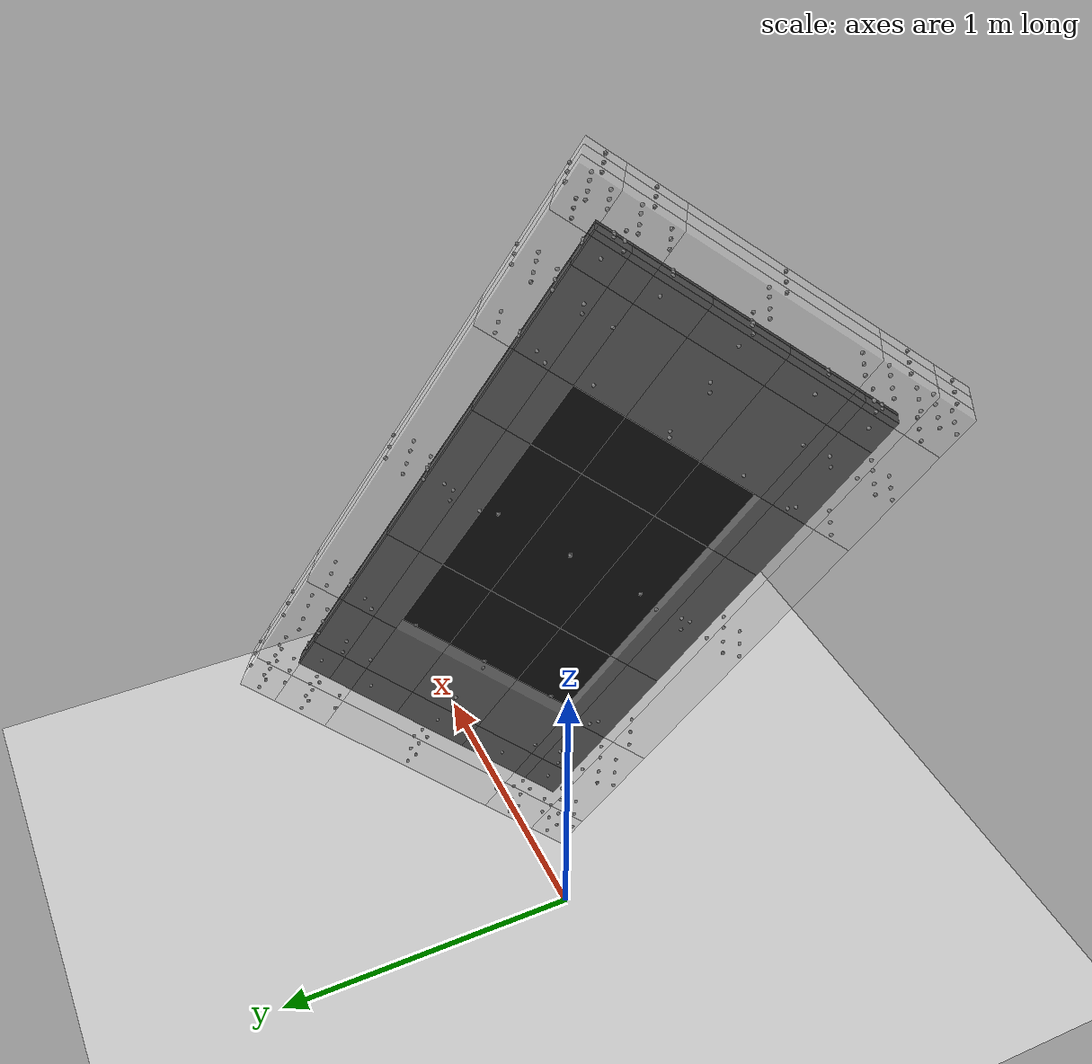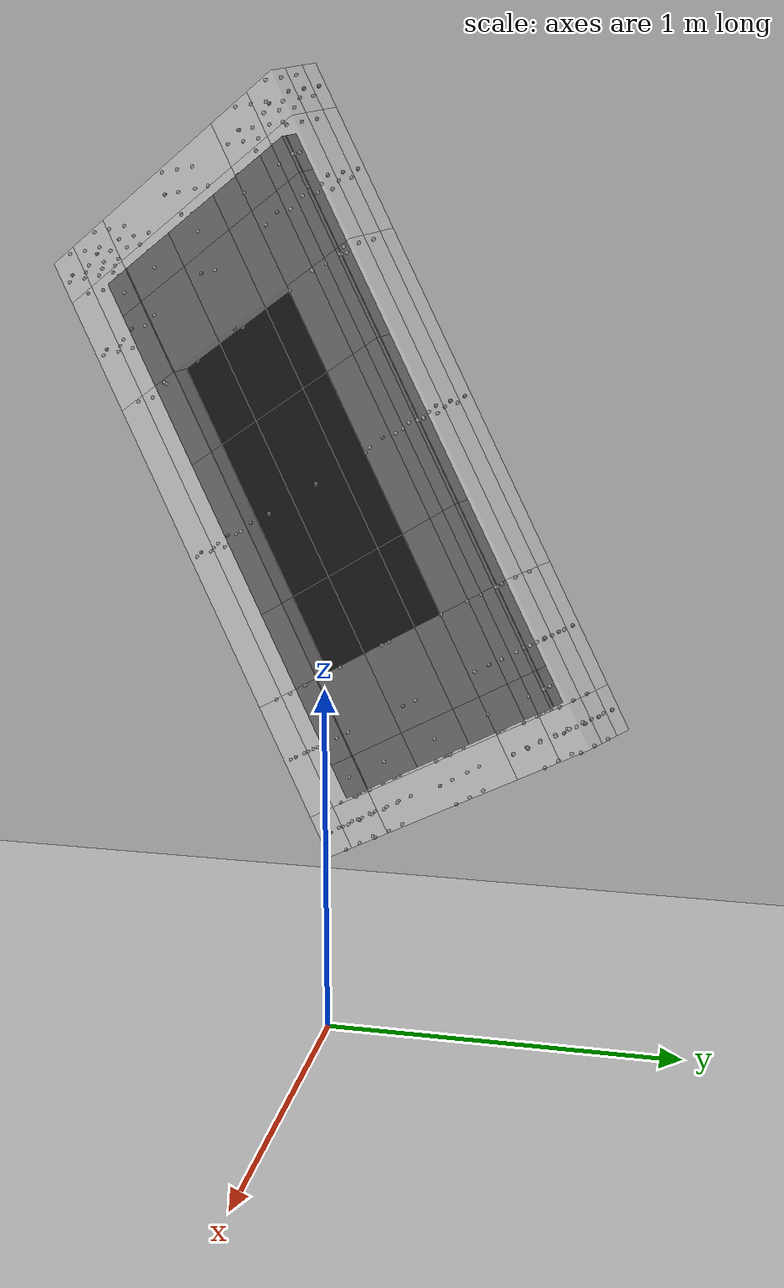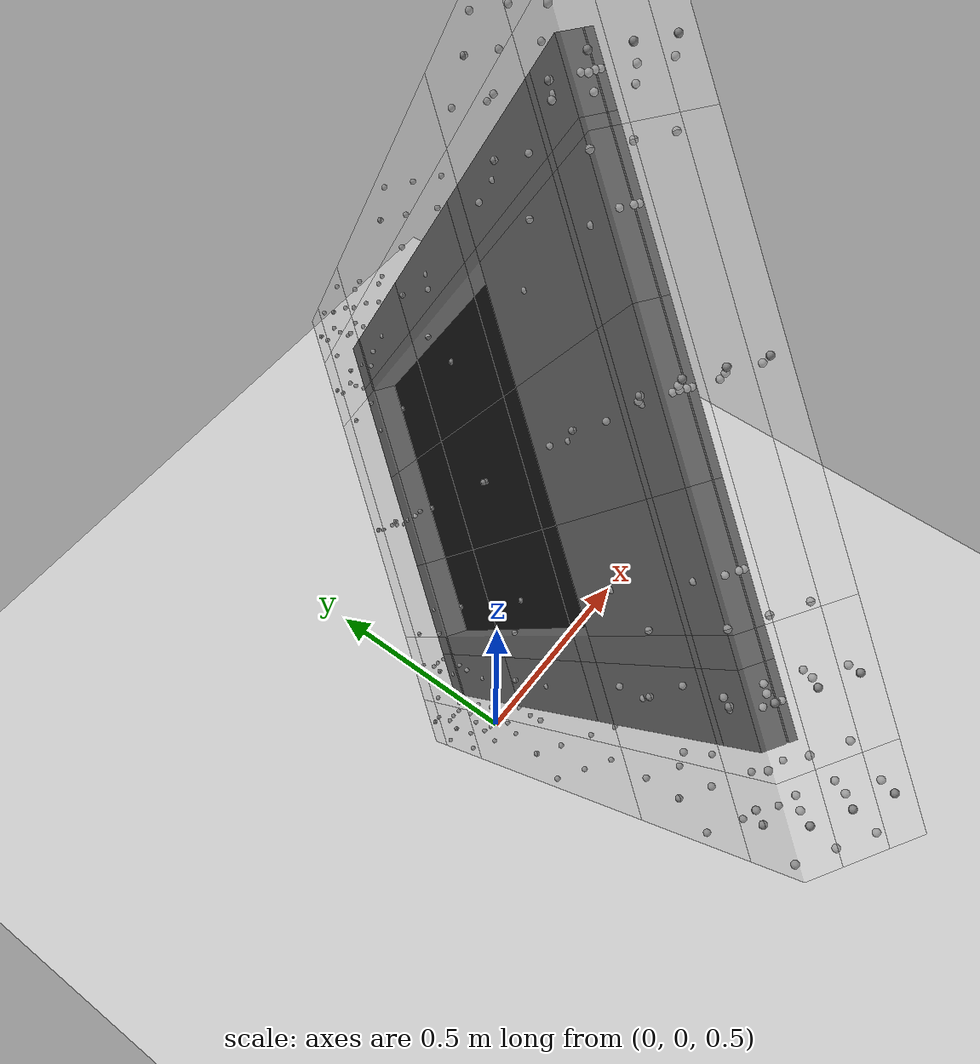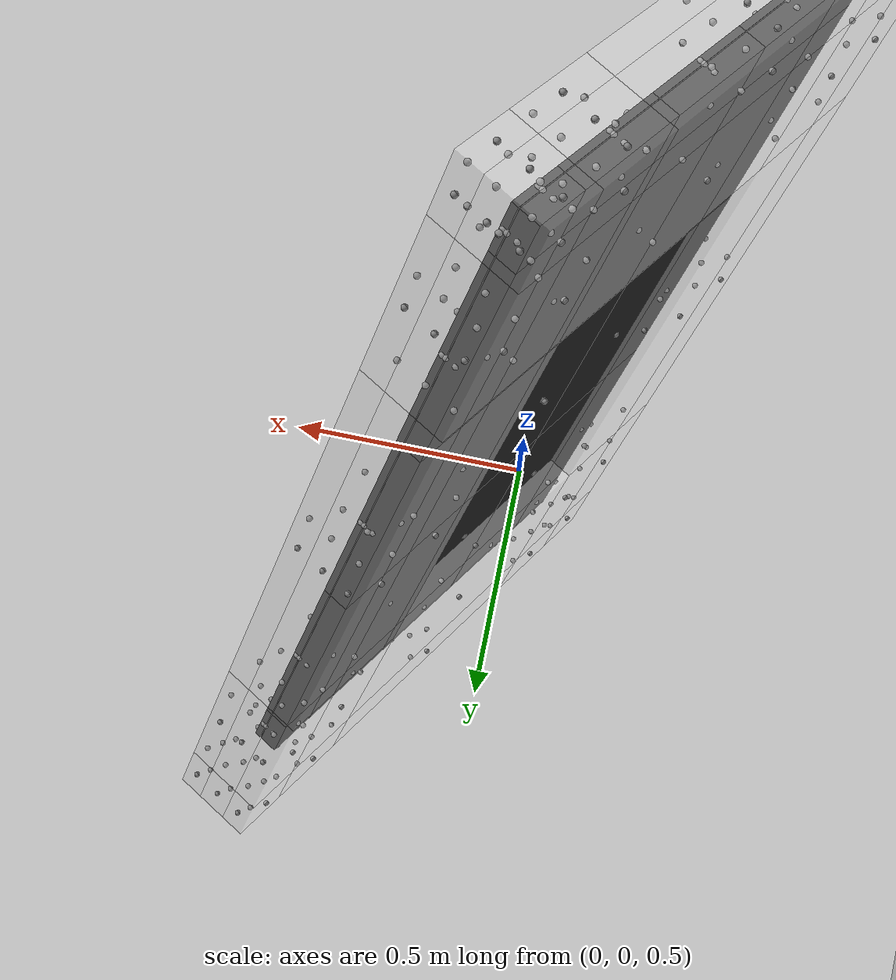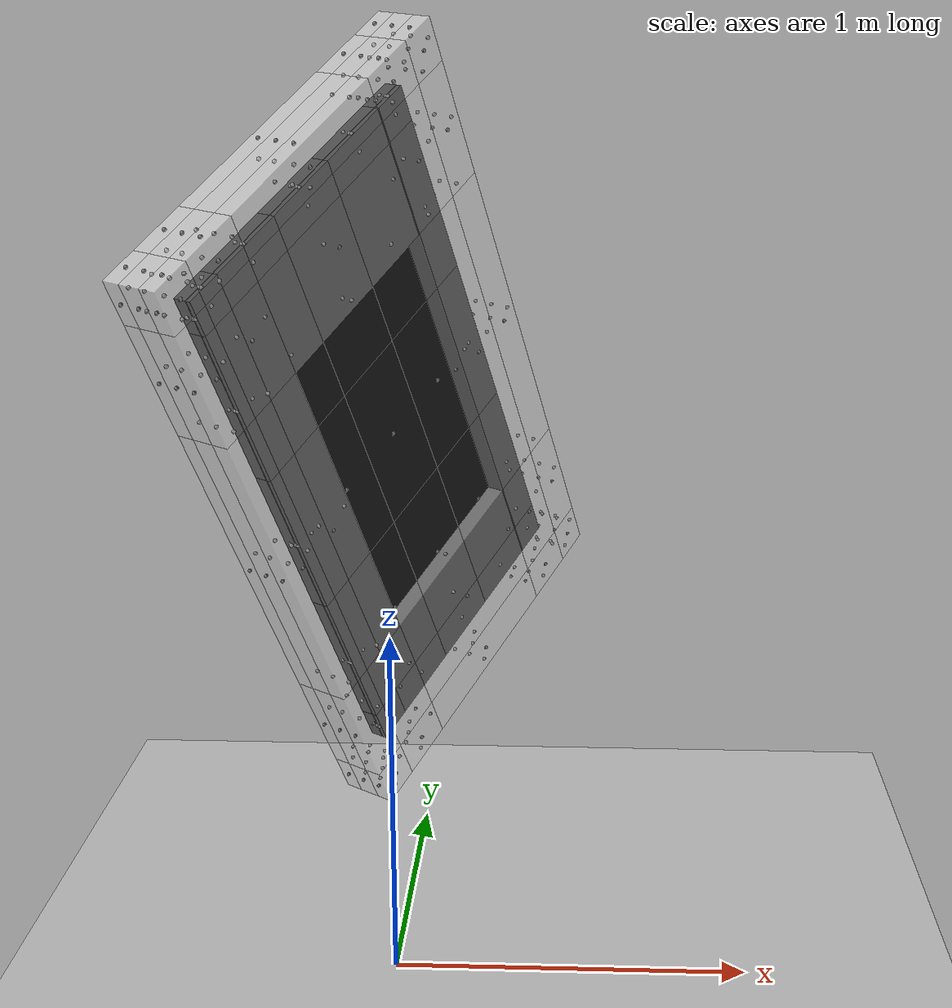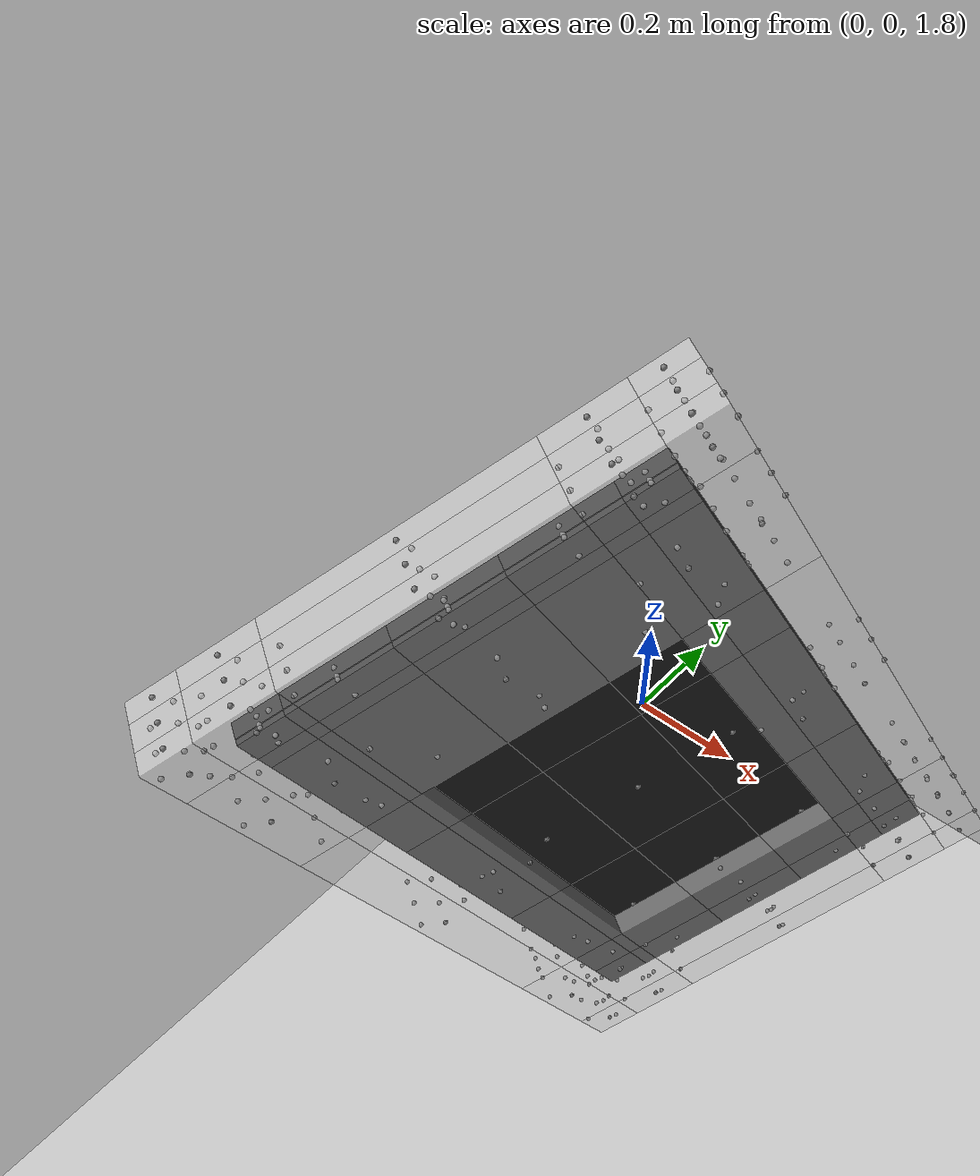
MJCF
<mujoco model="discrete_custom_box">
  <size memory="512M"/>
  <option integrator="implicitfast" timestep="0.0012" iterations="50" noslip_iterations="0" tolerance="1e-05" impratio="1.0" gravity="0 0 -9.81" density="1.225" viscosity="1.81e-05">
    <flag contact="enable"/>
  </option>
  <visual>
    <quality shadowsize="0"/>
    <global offwidth="0" offheight="0"/>
    <headlight ambient="0.4 0.4 0.4" diffuse="0.8 0.8 0.8" specular="0.07 0.07 0.07"/>
    <map znear="0.01"/>
  </visual>
  <asset>
    <texture type="skybox" builtin="gradient" rgb1="0.1 0.1 0.1" rgb2="0.3 0.3 0.3" width="1024" height="1024"/>
    <texture type="2d" name="ground_tex" builtin="checker" mark="edge" rgb1="0.85 0.85 0.85" rgb2="0.75 0.75 0.75" markrgb="0.8 0.8 0.8" width="300" height="300"/>
    <material name="ground_mat" texture="ground_tex" texrepeat="5 5" texuniform="true" reflectance="0.0"/>
  </asset>
  <default>
    <joint armature="0.05" damping="1.0"/>
    <geom/>
    <default class="bpaperbox">
      <geom group="0" rgba="0.5 0.3 0.2 1" contype="0" conaffinity="0"/>
    </default>
    <default class="weld_bpaperbox">
      <equality solref="0.01 1.0" solimp="0.1 0.95 0.01 0.5 2"/>
    </default>
    <default class="bcushion">
      <geom group="1" rgba="1 1 1 0.4" contype="0" conaffinity="0"/>
    </default>
    <default class="bcushion_edge">
      <geom group="1" rgba="1 1 1 0.4" contype="0" conaffinity="0"/>
    </default>
    <default class="weld_bcushion">
      <equality solref="-9000.0 -600.0" solimp="0.1 0.95 0.01 0.5 2"/>
    </default>
    <default class="weld_bcushion_corner">
      <equality solref="-9000.0 -600.0" solimp="0.1 0.95 0.01 0.5 2"/>
    </default>
    <default class="bopencell">
      <geom group="2" rgba="0.1 0.1 0.1 1" contype="0" conaffinity="0"/>
    </default>
    <default class="weld_bopencell">
      <equality solref="0.005 0.8" solimp="0.1 0.95 0.01 0.5 2"/>
    </default>
    <default class="bopencellcohesive">
      <geom group="2" rgba="1 0.1 0.1 0.4" contype="0" conaffinity="0"/>
    </default>
    <default class="weld_bopencellcohesive">
      <equality solref="0.1 0.8" solimp="0.1 0.95 0.01 0.5 2"/>
    </default>
    <default class="bchassis">
      <geom group="2" rgba="0.1 0.1 0.1 1" contype="0" conaffinity="0"/>
    </default>
    <default class="weld_bchassis">
      <equality solref="0.005 0.8" solimp="0.1 0.99 0.01 0.5 2"/>
    </default>
    <default class="bauxboxmass">
      <geom group="3" rgba="0.1 0.1 0.1 1" contype="0" conaffinity="0"/>
    </default>
    <default class="weld_bauxboxmass">
      <equality solref="0.02 1.0" solimp="0.1 0.95 0.005 0.5 2"/>
    </default>
    <default class="ground">
      <geom friction="1.0 1.0" solref="0.002 0.001" solimp="0.9 0.99 0.001" condim="3" contype="0" conaffinity="0" group="0" material="ground_mat"/>
    </default>
    <default class="cls_ground_cushion">
      <pair friction="0.3 0.3 0.005 0.0001 0.0001" solref="0.001 1.8" solimp="0.1 0.95 0.005 0.5 2"/>
    </default>
    <default class="cls_ground_cushion_edge">
      <pair friction="0.3 0.3 0.005 0.0001 0.0001" solref="0.001 1.8" solimp="0.1 0.95 0.005 0.5 2"/>
    </default>
    <default class="cls_ground_paper">
      <pair friction="0.3 0.3 0.005 0.0001 0.0001" solref="0.001 1.8" solimp="0.1 0.95 0.005 0.5 2"/>
    </default>
    <default class="cls_cushion_opencell">
      <pair friction="0.3 0.3 0.005 0.0001 0.0001" solref="0.001 1.8" solimp="0.1 0.95 0.005 0.5 2"/>
    </default>
    <default class="cls_cushion_chassis">
      <pair friction="0.3 0.3 0.005 0.0001 0.0001" solref="0.001 1.8" solimp="0.1 0.95 0.005 0.5 2"/>
    </default>
    <default class="cls_cushion_paper">
      <pair friction="0.3 0.3 0.005 0.0001 0.0001" solref="0.001 1.8" solimp="0.1 0.95 0.005 0.5 2"/>
    </default>
  </default>
  <worldbody>
    <camera name="iso_view" pos="4.5 -4.5 3.5" xyaxes="1 1 0 -0.4 0.4 1" mode="fixed"/>
    <light pos="0 0 6" dir="0 0 -1" directional="false" diffuse="0.8 0.8 0.8" ambient="0.3 0.3 0.3" castshadow="false"/>
    <light pos="3 3 5" dir="-1 -1 -1" directional="false" diffuse="0.4 0.4 0.4" castshadow="false"/>
    <geom name="ground" type="plane" size="2.5 2.5 0.1" class="ground"/>
    <body name="BPackagingBox" pos="0.00000 0.00000 1.57643" axisangle="0.5139 0.8578 0.0000 94.5291">
      <freejoint/>
      <geom type="box" size="0.001 0.001 0.001" mass="0.000021" rgba="0 0 0 0"/>
      <body name="BCushion">
        <body name="b_bcushion_0_0_0" pos="-0.85125 -0.48925 -0.05325">
          <joint type="slide" axis="1 0 0"/>
          <joint type="slide" axis="0 1 0"/>
          <joint type="slide" axis="0 0 1"/>
          <joint type="ball"/>
          <geom name="g_bcushion_0_0_0_edge" type="box" size="0.06125 0.05425 0.02375" mass="0.007122" class="bcushion_edge"/>
          <site name="s_BCushion_0_0_0_PX" pos="0.06125 0 0"/>
          <site name="s_BCushion_0_0_0_NX" pos="-0.06125 0 0"/>
          <site name="s_BCushion_0_0_0_PY" pos="0 0.05425 0"/>
          <site name="s_BCushion_0_0_0_NY" pos="0 -0.05425 0"/>
          <site name="s_BCushion_0_0_0_PZ" pos="0 0 0.02375"/>
          <site name="s_BCushion_0_0_0_NZ" pos="0 0 -0.02375"/>
        </body>
        <body name="b_bcushion_0_0_1" pos="-0.85125 -0.48925 0.00000">
          <joint type="slide" axis="1 0 0"/>
          <joint type="slide" axis="0 1 0"/>
          <joint type="slide" axis="0 0 1"/>
          <joint type="ball"/>
          <geom name="g_bcushion_0_0_1_edge" type="box" size="0.06125 0.05425 0.02950" mass="0.008847" class="bcushion_edge"/>
          <site name="s_BCushion_0_0_1_PX" pos="0.06125 0 0"/>
          <site name="s_BCushion_0_0_1_NX" pos="-0.06125 0 0"/>
          <site name="s_BCushion_0_0_1_PY" pos="0 0.05425 0"/>
          <site name="s_BCushion_0_0_1_NY" pos="0 -0.05425 0"/>
          <site name="s_BCushion_0_0_1_PZ" pos="0 0 0.02950"/>
          <site name="s_BCushion_0_0_1_NZ" pos="0 0 -0.02950"/>
        </body>
        <body name="b_bcushion_0_0_2" pos="-0.85125 -0.48925 0.05325">
          <joint type="slide" axis="1 0 0"/>
          <joint type="slide" axis="0 1 0"/>
          <joint type="slide" axis="0 0 1"/>
          <joint type="ball"/>
          <geom name="g_bcushion_0_0_2_edge" type="box" size="0.06125 0.05425 0.02375" mass="0.007122" class="bcushion_edge"/>
          <site name="s_BCushion_0_0_2_PX" pos="0.06125 0 0"/>
          <site name="s_BCushion_0_0_2_NX" pos="-0.06125 0 0"/>
          <site name="s_BCushion_0_0_2_PY" pos="0 0.05425 0"/>
          <site name="s_BCushion_0_0_2_NY" pos="0 -0.05425 0"/>
          <site name="s_BCushion_0_0_2_PZ" pos="0 0 0.02375"/>
          <site name="s_BCushion_0_0_2_NZ" pos="0 0 -0.02375"/>
        </body>
        <body name="b_bcushion_0_1_0" pos="-0.85125 -0.35337 -0.05325">
          <joint type="slide" axis="1 0 0"/>
          <joint type="slide" axis="0 1 0"/>
          <joint type="slide" axis="0 0 1"/>
          <joint type="ball"/>
          <geom name="g_bcushion_0_1_0" type="box" size="0.06125 0.08163 0.02375" mass="0.010716" class="bcushion"/>
          <site name="s_BCushion_0_1_0_PX" pos="0.06125 0 0"/>
          <site name="s_BCushion_0_1_0_NX" pos="-0.06125 0 0"/>
          <site name="s_BCushion_0_1_0_PY" pos="0 0.08163 0"/>
          <site name="s_BCushion_0_1_0_NY" pos="0 -0.08163 0"/>
          <site name="s_BCushion_0_1_0_PZ" pos="0 0 0.02375"/>
          <site name="s_BCushion_0_1_0_NZ" pos="0 0 -0.02375"/>
        </body>
        <body name="b_bcushion_0_1_1" pos="-0.85125 -0.35337 0.00000">
          <joint type="slide" axis="1 0 0"/>
          <joint type="slide" axis="0 1 0"/>
          <joint type="slide" axis="0 0 1"/>
          <joint type="ball"/>
          <geom name="g_bcushion_0_1_1" type="box" size="0.06125 0.08163 0.02950" mass="0.013311" class="bcushion"/>
          <site name="s_BCushion_0_1_1_PX" pos="0.06125 0 0"/>
          <site name="s_BCushion_0_1_1_NX" pos="-0.06125 0 0"/>
          <site name="s_BCushion_0_1_1_PY" pos="0 0.08163 0"/>
          <site name="s_BCushion_0_1_1_NY" pos="0 -0.08163 0"/>
          <site name="s_BCushion_0_1_1_PZ" pos="0 0 0.02950"/>
          <site name="s_BCushion_0_1_1_NZ" pos="0 0 -0.02950"/>
        </body>
        <body name="b_bcushion_0_1_2" pos="-0.85125 -0.35337 0.05325">
          <joint type="slide" axis="1 0 0"/>
          <joint type="slide" axis="0 1 0"/>
          <joint type="slide" axis="0 0 1"/>
          <joint type="ball"/>
          <geom name="g_bcushion_0_1_2" type="box" size="0.06125 0.08163 0.02375" mass="0.010716" class="bcushion"/>
          <site name="s_BCushion_0_1_2_PX" pos="0.06125 0 0"/>
          <site name="s_BCushion_0_1_2_NX" pos="-0.06125 0 0"/>
          <site name="s_BCushion_0_1_2_PY" pos="0 0.08163 0"/>
          <site name="s_BCushion_0_1_2_NY" pos="0 -0.08163 0"/>
          <site name="s_BCushion_0_1_2_PZ" pos="0 0 0.02375"/>
          <site name="s_BCushion_0_1_2_NZ" pos="0 0 -0.02375"/>
        </body>
        <body name="b_bcushion_0_2_0" pos="-0.85125 0.00000 -0.05325">
          <joint type="slide" axis="1 0 0"/>
          <joint type="slide" axis="0 1 0"/>
          <joint type="slide" axis="0 0 1"/>
          <joint type="ball"/>
          <geom name="g_bcushion_0_2_0" type="box" size="0.06125 0.27175 0.02375" mass="0.035677" class="bcushion"/>
          <site name="s_BCushion_0_2_0_PX" pos="0.06125 0 0"/>
          <site name="s_BCushion_0_2_0_NX" pos="-0.06125 0 0"/>
          <site name="s_BCushion_0_2_0_PY" pos="0 0.27175 0"/>
          <site name="s_BCushion_0_2_0_NY" pos="0 -0.27175 0"/>
          <site name="s_BCushion_0_2_0_PZ" pos="0 0 0.02375"/>
          <site name="s_BCushion_0_2_0_NZ" pos="0 0 -0.02375"/>
        </body>
        <body name="b_bcushion_0_2_1" pos="-0.85125 0.00000 0.00000">
          <joint type="slide" axis="1 0 0"/>
          <joint type="slide" axis="0 1 0"/>
          <joint type="slide" axis="0 0 1"/>
          <joint type="ball"/>
          <geom name="g_bcushion_0_2_1" type="box" size="0.06125 0.27175 0.02950" mass="0.044314" class="bcushion"/>
          <site name="s_BCushion_0_2_1_PX" pos="0.06125 0 0"/>
          <site name="s_BCushion_0_2_1_NX" pos="-0.06125 0 0"/>
          <site name="s_BCushion_0_2_1_PY" pos="0 0.27175 0"/>
          <site name="s_BCushion_0_2_1_NY" pos="0 -0.27175 0"/>
          <site name="s_BCushion_0_2_1_PZ" pos="0 0 0.02950"/>
          <site name="s_BCushion_0_2_1_NZ" pos="0 0 -0.02950"/>
        </body>
        <body name="b_bcushion_0_2_2" pos="-0.85125 0.00000 0.05325">
          <joint type="slide" axis="1 0 0"/>
          <joint type="slide" axis="0 1 0"/>
          <joint type="slide" axis="0 0 1"/>
          <joint type="ball"/>
          <geom name="g_bcushion_0_2_2" type="box" size="0.06125 0.27175 0.02375" mass="0.035677" class="bcushion"/>
          <site name="s_BCushion_0_2_2_PX" pos="0.06125 0 0"/>
          <site name="s_BCushion_0_2_2_NX" pos="-0.06125 0 0"/>
          <site name="s_BCushion_0_2_2_PY" pos="0 0.27175 0"/>
          <site name="s_BCushion_0_2_2_NY" pos="0 -0.27175 0"/>
          <site name="s_BCushion_0_2_2_PZ" pos="0 0 0.02375"/>
          <site name="s_BCushion_0_2_2_NZ" pos="0 0 -0.02375"/>
        </body>
        <body name="b_bcushion_0_3_0" pos="-0.85125 0.35337 -0.05325">
          <joint type="slide" axis="1 0 0"/>
          <joint type="slide" axis="0 1 0"/>
          <joint type="slide" axis="0 0 1"/>
          <joint type="ball"/>
          <geom name="g_bcushion_0_3_0" type="box" size="0.06125 0.08163 0.02375" mass="0.010716" class="bcushion"/>
          <site name="s_BCushion_0_3_0_PX" pos="0.06125 0 0"/>
          <site name="s_BCushion_0_3_0_NX" pos="-0.06125 0 0"/>
          <site name="s_BCushion_0_3_0_PY" pos="0 0.08163 0"/>
          <site name="s_BCushion_0_3_0_NY" pos="0 -0.08163 0"/>
          <site name="s_BCushion_0_3_0_PZ" pos="0 0 0.02375"/>
          <site name="s_BCushion_0_3_0_NZ" pos="0 0 -0.02375"/>
        </body>
        <body name="b_bcushion_0_3_1" pos="-0.85125 0.35337 0.00000">
          <joint type="slide" axis="1 0 0"/>
          <joint type="slide" axis="0 1 0"/>
          <joint type="slide" axis="0 0 1"/>
          <joint type="ball"/>
          <geom name="g_bcushion_0_3_1" type="box" size="0.06125 0.08163 0.02950" mass="0.013311" class="bcushion"/>
          <site name="s_BCushion_0_3_1_PX" pos="0.06125 0 0"/>
          <site name="s_BCushion_0_3_1_NX" pos="-0.06125 0 0"/>
          <site name="s_BCushion_0_3_1_PY" pos="0 0.08163 0"/>
          <site name="s_BCushion_0_3_1_NY" pos="0 -0.08163 0"/>
          <site name="s_BCushion_0_3_1_PZ" pos="0 0 0.02950"/>
          <site name="s_BCushion_0_3_1_NZ" pos="0 0 -0.02950"/>
        </body>
        <body name="b_bcushion_0_3_2" pos="-0.85125 0.35337 0.05325">
          <joint type="slide" axis="1 0 0"/>
          <joint type="slide" axis="0 1 0"/>
          <joint type="slide" axis="0 0 1"/>
          <joint type="ball"/>
          <geom name="g_bcushion_0_3_2" type="box" size="0.06125 0.08163 0.02375" mass="0.010716" class="bcushion"/>
          <site name="s_BCushion_0_3_2_PX" pos="0.06125 0 0"/>
          <site name="s_BCushion_0_3_2_NX" pos="-0.06125 0 0"/>
          <site name="s_BCushion_0_3_2_PY" pos="0 0.08163 0"/>
          <site name="s_BCushion_0_3_2_NY" pos="0 -0.08163 0"/>
          <site name="s_BCushion_0_3_2_PZ" pos="0 0 0.02375"/>
          <site name="s_BCushion_0_3_2_NZ" pos="0 0 -0.02375"/>
        </body>
        <body name="b_bcushion_0_4_0" pos="-0.85125 0.48925 -0.05325">
          <joint type="slide" axis="1 0 0"/>
          <joint type="slide" axis="0 1 0"/>
          <joint type="slide" axis="0 0 1"/>
          <joint type="ball"/>
          <geom name="g_bcushion_0_4_0_edge" type="box" size="0.06125 0.05425 0.02375" mass="0.007122" class="bcushion_edge"/>
          <site name="s_BCushion_0_4_0_PX" pos="0.06125 0 0"/>
          <site name="s_BCushion_0_4_0_NX" pos="-0.06125 0 0"/>
          <site name="s_BCushion_0_4_0_PY" pos="0 0.05425 0"/>
          <site name="s_BCushion_0_4_0_NY" pos="0 -0.05425 0"/>
          <site name="s_BCushion_0_4_0_PZ" pos="0 0 0.02375"/>
          <site name="s_BCushion_0_4_0_NZ" pos="0 0 -0.02375"/>
        </body>
        <body name="b_bcushion_0_4_1" pos="-0.85125 0.48925 0.00000">
          <joint type="slide" axis="1 0 0"/>
          <joint type="slide" axis="0 1 0"/>
          <joint type="slide" axis="0 0 1"/>
          <joint type="ball"/>
          <geom name="g_bcushion_0_4_1_edge" type="box" size="0.06125 0.05425 0.02950" mass="0.008847" class="bcushion_edge"/>
          <site name="s_BCushion_0_4_1_PX" pos="0.06125 0 0"/>
          <site name="s_BCushion_0_4_1_NX" pos="-0.06125 0 0"/>
          <site name="s_BCushion_0_4_1_PY" pos="0 0.05425 0"/>
          <site name="s_BCushion_0_4_1_NY" pos="0 -0.05425 0"/>
          <site name="s_BCushion_0_4_1_PZ" pos="0 0 0.02950"/>
          <site name="s_BCushion_0_4_1_NZ" pos="0 0 -0.02950"/>
        </body>
        <body name="b_bcushion_0_4_2" pos="-0.85125 0.48925 0.05325">
          <joint type="slide" axis="1 0 0"/>
          <joint type="slide" axis="0 1 0"/>
          <joint type="slide" axis="0 0 1"/>
          <joint type="ball"/>
          <geom name="g_bcushion_0_4_2_edge" type="box" size="0.06125 0.05425 0.02375" mass="0.007122" class="bcushion_edge"/>
          <site name="s_BCushion_0_4_2_PX" pos="0.06125 0 0"/>
          <site name="s_BCushion_0_4_2_NX" pos="-0.06125 0 0"/>
          <site name="s_BCushion_0_4_2_PY" pos="0 0.05425 0"/>
          <site name="s_BCushion_0_4_2_NY" pos="0 -0.05425 0"/>
          <site name="s_BCushion_0_4_2_PZ" pos="0 0 0.02375"/>
          <site name="s_BCushion_0_4_2_NZ" pos="0 0 -0.02375"/>
        </body>
        <body name="b_bcushion_1_0_0" pos="-0.62313 -0.48925 -0.05325">
          <joint type="slide" axis="1 0 0"/>
          <joint type="slide" axis="0 1 0"/>
          <joint type="slide" axis="0 0 1"/>
          <joint type="ball"/>
          <geom name="g_bcushion_1_0_0" type="box" size="0.16688 0.05425 0.02375" mass="0.019404" class="bcushion"/>
          <site name="s_BCushion_1_0_0_PX" pos="0.16688 0 0"/>
          <site name="s_BCushion_1_0_0_NX" pos="-0.16688 0 0"/>
          <site name="s_BCushion_1_0_0_PY" pos="0 0.05425 0"/>
          <site name="s_BCushion_1_0_0_NY" pos="0 -0.05425 0"/>
          <site name="s_BCushion_1_0_0_PZ" pos="0 0 0.02375"/>
          <site name="s_BCushion_1_0_0_NZ" pos="0 0 -0.02375"/>
        </body>
        <body name="b_bcushion_1_0_1" pos="-0.62313 -0.48925 0.00000">
          <joint type="slide" axis="1 0 0"/>
          <joint type="slide" axis="0 1 0"/>
          <joint type="slide" axis="0 0 1"/>
          <joint type="ball"/>
          <geom name="g_bcushion_1_0_1" type="box" size="0.16688 0.05425 0.02950" mass="0.024102" class="bcushion"/>
          <site name="s_BCushion_1_0_1_PX" pos="0.16688 0 0"/>
          <site name="s_BCushion_1_0_1_NX" pos="-0.16688 0 0"/>
          <site name="s_BCushion_1_0_1_PY" pos="0 0.05425 0"/>
          <site name="s_BCushion_1_0_1_NY" pos="0 -0.05425 0"/>
          <site name="s_BCushion_1_0_1_PZ" pos="0 0 0.02950"/>
          <site name="s_BCushion_1_0_1_NZ" pos="0 0 -0.02950"/>
        </body>
        <body name="b_bcushion_1_0_2" pos="-0.62313 -0.48925 0.05325">
          <joint type="slide" axis="1 0 0"/>
          <joint type="slide" axis="0 1 0"/>
          <joint type="slide" axis="0 0 1"/>
          <joint type="ball"/>
          <geom name="g_bcushion_1_0_2" type="box" size="0.16688 0.05425 0.02375" mass="0.019404" class="bcushion"/>
          <site name="s_BCushion_1_0_2_PX" pos="0.16688 0 0"/>
          <site name="s_BCushion_1_0_2_NX" pos="-0.16688 0 0"/>
          <site name="s_BCushion_1_0_2_PY" pos="0 0.05425 0"/>
          <site name="s_BCushion_1_0_2_NY" pos="0 -0.05425 0"/>
          <site name="s_BCushion_1_0_2_PZ" pos="0 0 0.02375"/>
          <site name="s_BCushion_1_0_2_NZ" pos="0 0 -0.02375"/>
        </body>
        <body name="b_bcushion_1_1_0" pos="-0.62313 -0.35337 -0.05325">
          <joint type="slide" axis="1 0 0"/>
          <joint type="slide" axis="0 1 0"/>
          <joint type="slide" axis="0 0 1"/>
          <joint type="ball"/>
          <geom name="g_bcushion_1_1_0" type="box" size="0.16688 0.08163 0.02375" mass="0.029196" class="bcushion"/>
          <site name="s_BCushion_1_1_0_PX" pos="0.16688 0 0"/>
          <site name="s_BCushion_1_1_0_NX" pos="-0.16688 0 0"/>
          <site name="s_BCushion_1_1_0_PY" pos="0 0.08163 0"/>
          <site name="s_BCushion_1_1_0_NY" pos="0 -0.08163 0"/>
          <site name="s_BCushion_1_1_0_PZ" pos="0 0 0.02375"/>
          <site name="s_BCushion_1_1_0_NZ" pos="0 0 -0.02375"/>
        </body>
        <body name="b_bcushion_1_1_2" pos="-0.62313 -0.35337 0.05325">
          <joint type="slide" axis="1 0 0"/>
          <joint type="slide" axis="0 1 0"/>
          <joint type="slide" axis="0 0 1"/>
          <joint type="ball"/>
          <geom name="g_bcushion_1_1_2" type="box" size="0.16688 0.08163 0.02375" mass="0.029196" class="bcushion"/>
          <site name="s_BCushion_1_1_2_PX" pos="0.16688 0 0"/>
          <site name="s_BCushion_1_1_2_NX" pos="-0.16688 0 0"/>
          <site name="s_BCushion_1_1_2_PY" pos="0 0.08163 0"/>
          <site name="s_BCushion_1_1_2_NY" pos="0 -0.08163 0"/>
          <site name="s_BCushion_1_1_2_PZ" pos="0 0 0.02375"/>
          <site name="s_BCushion_1_1_2_NZ" pos="0 0 -0.02375"/>
        </body>
        <body name="b_bcushion_1_2_0" pos="-0.62313 0.00000 -0.05325">
          <joint type="slide" axis="1 0 0"/>
          <joint type="slide" axis="0 1 0"/>
          <joint type="slide" axis="0 0 1"/>
          <joint type="ball"/>
          <geom name="g_bcushion_1_2_0" type="box" size="0.16688 0.27175 0.02375" mass="0.097201" class="bcushion"/>
          <site name="s_BCushion_1_2_0_PX" pos="0.16688 0 0"/>
          <site name="s_BCushion_1_2_0_NX" pos="-0.16688 0 0"/>
          <site name="s_BCushion_1_2_0_PY" pos="0 0.27175 0"/>
          <site name="s_BCushion_1_2_0_NY" pos="0 -0.27175 0"/>
          <site name="s_BCushion_1_2_0_PZ" pos="0 0 0.02375"/>
          <site name="s_BCushion_1_2_0_NZ" pos="0 0 -0.02375"/>
        </body>
        <body name="b_bcushion_1_2_2" pos="-0.62313 0.00000 0.05325">
          <joint type="slide" axis="1 0 0"/>
          <joint type="slide" axis="0 1 0"/>
          <joint type="slide" axis="0 0 1"/>
          <joint type="ball"/>
          <geom name="g_bcushion_1_2_2" type="box" size="0.16688 0.27175 0.02375" mass="0.097201" class="bcushion"/>
          <site name="s_BCushion_1_2_2_PX" pos="0.16688 0 0"/>
          <site name="s_BCushion_1_2_2_NX" pos="-0.16688 0 0"/>
          <site name="s_BCushion_1_2_2_PY" pos="0 0.27175 0"/>
          <site name="s_BCushion_1_2_2_NY" pos="0 -0.27175 0"/>
          <site name="s_BCushion_1_2_2_PZ" pos="0 0 0.02375"/>
          <site name="s_BCushion_1_2_2_NZ" pos="0 0 -0.02375"/>
        </body>
        <body name="b_bcushion_1_3_0" pos="-0.62313 0.35337 -0.05325">
          <joint type="slide" axis="1 0 0"/>
          <joint type="slide" axis="0 1 0"/>
          <joint type="slide" axis="0 0 1"/>
          <joint type="ball"/>
          <geom name="g_bcushion_1_3_0" type="box" size="0.16688 0.08163 0.02375" mass="0.029196" class="bcushion"/>
          <site name="s_BCushion_1_3_0_PX" pos="0.16688 0 0"/>
          <site name="s_BCushion_1_3_0_NX" pos="-0.16688 0 0"/>
          <site name="s_BCushion_1_3_0_PY" pos="0 0.08163 0"/>
          <site name="s_BCushion_1_3_0_NY" pos="0 -0.08163 0"/>
          <site name="s_BCushion_1_3_0_PZ" pos="0 0 0.02375"/>
          <site name="s_BCushion_1_3_0_NZ" pos="0 0 -0.02375"/>
        </body>
        <body name="b_bcushion_1_3_2" pos="-0.62313 0.35337 0.05325">
          <joint type="slide" axis="1 0 0"/>
          <joint type="slide" axis="0 1 0"/>
          <joint type="slide" axis="0 0 1"/>
          <joint type="ball"/>
          <geom name="g_bcushion_1_3_2" type="box" size="0.16688 0.08163 0.02375" mass="0.029196" class="bcushion"/>
          <site name="s_BCushion_1_3_2_PX" pos="0.16688 0 0"/>
          <site name="s_BCushion_1_3_2_NX" pos="-0.16688 0 0"/>
          <site name="s_BCushion_1_3_2_PY" pos="0 0.08163 0"/>
          <site name="s_BCushion_1_3_2_NY" pos="0 -0.08163 0"/>
          <site name="s_BCushion_1_3_2_PZ" pos="0 0 0.02375"/>
          <site name="s_BCushion_1_3_2_NZ" pos="0 0 -0.02375"/>
        </body>
        <body name="b_bcushion_1_4_0" pos="-0.62313 0.48925 -0.05325">
          <joint type="slide" axis="1 0 0"/>
          <joint type="slide" axis="0 1 0"/>
          <joint type="slide" axis="0 0 1"/>
          <joint type="ball"/>
          <geom name="g_bcushion_1_4_0" type="box" size="0.16688 0.05425 0.02375" mass="0.019404" class="bcushion"/>
          <site name="s_BCushion_1_4_0_PX" pos="0.16688 0 0"/>
          <site name="s_BCushion_1_4_0_NX" pos="-0.16688 0 0"/>
          <site name="s_BCushion_1_4_0_PY" pos="0 0.05425 0"/>
          <site name="s_BCushion_1_4_0_NY" pos="0 -0.05425 0"/>
          <site name="s_BCushion_1_4_0_PZ" pos="0 0 0.02375"/>
          <site name="s_BCushion_1_4_0_NZ" pos="0 0 -0.02375"/>
        </body>
        <body name="b_bcushion_1_4_1" pos="-0.62313 0.48925 0.00000">
          <joint type="slide" axis="1 0 0"/>
          <joint type="slide" axis="0 1 0"/>
          <joint type="slide" axis="0 0 1"/>
          <joint type="ball"/>
          <geom name="g_bcushion_1_4_1" type="box" size="0.16688 0.05425 0.02950" mass="0.024102" class="bcushion"/>
          <site name="s_BCushion_1_4_1_PX" pos="0.16688 0 0"/>
          <site name="s_BCushion_1_4_1_NX" pos="-0.16688 0 0"/>
          <site name="s_BCushion_1_4_1_PY" pos="0 0.05425 0"/>
          <site name="s_BCushion_1_4_1_NY" pos="0 -0.05425 0"/>
          <site name="s_BCushion_1_4_1_PZ" pos="0 0 0.02950"/>
          <site name="s_BCushion_1_4_1_NZ" pos="0 0 -0.02950"/>
        </body>
        <body name="b_bcushion_1_4_2" pos="-0.62313 0.48925 0.05325">
          <joint type="slide" axis="1 0 0"/>
          <joint type="slide" axis="0 1 0"/>
          <joint type="slide" axis="0 0 1"/>
          <joint type="ball"/>
          <geom name="g_bcushion_1_4_2" type="box" size="0.16688 0.05425 0.02375" mass="0.019404" class="bcushion"/>
          <site name="s_BCushion_1_4_2_PX" pos="0.16688 0 0"/>
          <site name="s_BCushion_1_4_2_NX" pos="-0.16688 0 0"/>
          <site name="s_BCushion_1_4_2_PY" pos="0 0.05425 0"/>
          <site name="s_BCushion_1_4_2_NY" pos="0 -0.05425 0"/>
          <site name="s_BCushion_1_4_2_PZ" pos="0 0 0.02375"/>
          <site name="s_BCushion_1_4_2_NZ" pos="0 0 -0.02375"/>
        </body>
        <body name="b_bcushion_2_0_0" pos="0.00000 -0.48925 -0.05325">
          <joint type="slide" axis="1 0 0"/>
          <joint type="slide" axis="0 1 0"/>
          <joint type="slide" axis="0 0 1"/>
          <joint type="ball"/>
          <geom name="g_bcushion_2_0_0" type="box" size="0.45625 0.05425 0.02375" mass="0.053053" class="bcushion"/>
          <site name="s_BCushion_2_0_0_PX" pos="0.45625 0 0"/>
          <site name="s_BCushion_2_0_0_NX" pos="-0.45625 0 0"/>
          <site name="s_BCushion_2_0_0_PY" pos="0 0.05425 0"/>
          <site name="s_BCushion_2_0_0_NY" pos="0 -0.05425 0"/>
          <site name="s_BCushion_2_0_0_PZ" pos="0 0 0.02375"/>
          <site name="s_BCushion_2_0_0_NZ" pos="0 0 -0.02375"/>
        </body>
        <body name="b_bcushion_2_0_1" pos="0.00000 -0.48925 0.00000">
          <joint type="slide" axis="1 0 0"/>
          <joint type="slide" axis="0 1 0"/>
          <joint type="slide" axis="0 0 1"/>
          <joint type="ball"/>
          <geom name="g_bcushion_2_0_1" type="box" size="0.45625 0.05425 0.02950" mass="0.065898" class="bcushion"/>
          <site name="s_BCushion_2_0_1_PX" pos="0.45625 0 0"/>
          <site name="s_BCushion_2_0_1_NX" pos="-0.45625 0 0"/>
          <site name="s_BCushion_2_0_1_PY" pos="0 0.05425 0"/>
          <site name="s_BCushion_2_0_1_NY" pos="0 -0.05425 0"/>
          <site name="s_BCushion_2_0_1_PZ" pos="0 0 0.02950"/>
          <site name="s_BCushion_2_0_1_NZ" pos="0 0 -0.02950"/>
        </body>
        <body name="b_bcushion_2_0_2" pos="0.00000 -0.48925 0.05325">
          <joint type="slide" axis="1 0 0"/>
          <joint type="slide" axis="0 1 0"/>
          <joint type="slide" axis="0 0 1"/>
          <joint type="ball"/>
          <geom name="g_bcushion_2_0_2" type="box" size="0.45625 0.05425 0.02375" mass="0.053053" class="bcushion"/>
          <site name="s_BCushion_2_0_2_PX" pos="0.45625 0 0"/>
          <site name="s_BCushion_2_0_2_NX" pos="-0.45625 0 0"/>
          <site name="s_BCushion_2_0_2_PY" pos="0 0.05425 0"/>
          <site name="s_BCushion_2_0_2_NY" pos="0 -0.05425 0"/>
          <site name="s_BCushion_2_0_2_PZ" pos="0 0 0.02375"/>
          <site name="s_BCushion_2_0_2_NZ" pos="0 0 -0.02375"/>
        </body>
        <body name="b_bcushion_2_1_0" pos="0.00000 -0.35337 -0.05325">
          <joint type="slide" axis="1 0 0"/>
          <joint type="slide" axis="0 1 0"/>
          <joint type="slide" axis="0 0 1"/>
          <joint type="ball"/>
          <geom name="g_bcushion_2_1_0" type="box" size="0.45625 0.08163 0.02375" mass="0.079825" class="bcushion"/>
          <site name="s_BCushion_2_1_0_PX" pos="0.45625 0 0"/>
          <site name="s_BCushion_2_1_0_NX" pos="-0.45625 0 0"/>
          <site name="s_BCushion_2_1_0_PY" pos="0 0.08163 0"/>
          <site name="s_BCushion_2_1_0_NY" pos="0 -0.08163 0"/>
          <site name="s_BCushion_2_1_0_PZ" pos="0 0 0.02375"/>
          <site name="s_BCushion_2_1_0_NZ" pos="0 0 -0.02375"/>
        </body>
        <body name="b_bcushion_2_1_2" pos="0.00000 -0.35337 0.05325">
          <joint type="slide" axis="1 0 0"/>
          <joint type="slide" axis="0 1 0"/>
          <joint type="slide" axis="0 0 1"/>
          <joint type="ball"/>
          <geom name="g_bcushion_2_1_2" type="box" size="0.45625 0.08163 0.02375" mass="0.079825" class="bcushion"/>
          <site name="s_BCushion_2_1_2_PX" pos="0.45625 0 0"/>
          <site name="s_BCushion_2_1_2_NX" pos="-0.45625 0 0"/>
          <site name="s_BCushion_2_1_2_PY" pos="0 0.08163 0"/>
          <site name="s_BCushion_2_1_2_NY" pos="0 -0.08163 0"/>
          <site name="s_BCushion_2_1_2_PZ" pos="0 0 0.02375"/>
          <site name="s_BCushion_2_1_2_NZ" pos="0 0 -0.02375"/>
        </body>
        <body name="b_bcushion_2_3_0" pos="0.00000 0.35337 -0.05325">
          <joint type="slide" axis="1 0 0"/>
          <joint type="slide" axis="0 1 0"/>
          <joint type="slide" axis="0 0 1"/>
          <joint type="ball"/>
          <geom name="g_bcushion_2_3_0" type="box" size="0.45625 0.08163 0.02375" mass="0.079825" class="bcushion"/>
          <site name="s_BCushion_2_3_0_PX" pos="0.45625 0 0"/>
          <site name="s_BCushion_2_3_0_NX" pos="-0.45625 0 0"/>
          <site name="s_BCushion_2_3_0_PY" pos="0 0.08163 0"/>
          <site name="s_BCushion_2_3_0_NY" pos="0 -0.08163 0"/>
          <site name="s_BCushion_2_3_0_PZ" pos="0 0 0.02375"/>
          <site name="s_BCushion_2_3_0_NZ" pos="0 0 -0.02375"/>
        </body>
        <body name="b_bcushion_2_3_2" pos="0.00000 0.35337 0.05325">
          <joint type="slide" axis="1 0 0"/>
          <joint type="slide" axis="0 1 0"/>
          <joint type="slide" axis="0 0 1"/>
          <joint type="ball"/>
          <geom name="g_bcushion_2_3_2" type="box" size="0.45625 0.08163 0.02375" mass="0.079825" class="bcushion"/>
          <site name="s_BCushion_2_3_2_PX" pos="0.45625 0 0"/>
          <site name="s_BCushion_2_3_2_NX" pos="-0.45625 0 0"/>
          <site name="s_BCushion_2_3_2_PY" pos="0 0.08163 0"/>
          <site name="s_BCushion_2_3_2_NY" pos="0 -0.08163 0"/>
          <site name="s_BCushion_2_3_2_PZ" pos="0 0 0.02375"/>
          <site name="s_BCushion_2_3_2_NZ" pos="0 0 -0.02375"/>
        </body>
        <body name="b_bcushion_2_4_0" pos="0.00000 0.48925 -0.05325">
          <joint type="slide" axis="1 0 0"/>
          <joint type="slide" axis="0 1 0"/>
          <joint type="slide" axis="0 0 1"/>
          <joint type="ball"/>
          <geom name="g_bcushion_2_4_0" type="box" size="0.45625 0.05425 0.02375" mass="0.053053" class="bcushion"/>
          <site name="s_BCushion_2_4_0_PX" pos="0.45625 0 0"/>
          <site name="s_BCushion_2_4_0_NX" pos="-0.45625 0 0"/>
          <site name="s_BCushion_2_4_0_PY" pos="0 0.05425 0"/>
          <site name="s_BCushion_2_4_0_NY" pos="0 -0.05425 0"/>
          <site name="s_BCushion_2_4_0_PZ" pos="0 0 0.02375"/>
          <site name="s_BCushion_2_4_0_NZ" pos="0 0 -0.02375"/>
        </body>
        <body name="b_bcushion_2_4_1" pos="0.00000 0.48925 0.00000">
          <joint type="slide" axis="1 0 0"/>
          <joint type="slide" axis="0 1 0"/>
          <joint type="slide" axis="0 0 1"/>
          <joint type="ball"/>
          <geom name="g_bcushion_2_4_1" type="box" size="0.45625 0.05425 0.02950" mass="0.065898" class="bcushion"/>
          <site name="s_BCushion_2_4_1_PX" pos="0.45625 0 0"/>
          <site name="s_BCushion_2_4_1_NX" pos="-0.45625 0 0"/>
          <site name="s_BCushion_2_4_1_PY" pos="0 0.05425 0"/>
          <site name="s_BCushion_2_4_1_NY" pos="0 -0.05425 0"/>
          <site name="s_BCushion_2_4_1_PZ" pos="0 0 0.02950"/>
          <site name="s_BCushion_2_4_1_NZ" pos="0 0 -0.02950"/>
        </body>
        <body name="b_bcushion_2_4_2" pos="0.00000 0.48925 0.05325">
          <joint type="slide" axis="1 0 0"/>
          <joint type="slide" axis="0 1 0"/>
          <joint type="slide" axis="0 0 1"/>
          <joint type="ball"/>
          <geom name="g_bcushion_2_4_2" type="box" size="0.45625 0.05425 0.02375" mass="0.053053" class="bcushion"/>
          <site name="s_BCushion_2_4_2_PX" pos="0.45625 0 0"/>
          <site name="s_BCushion_2_4_2_NX" pos="-0.45625 0 0"/>
          <site name="s_BCushion_2_4_2_PY" pos="0 0.05425 0"/>
          <site name="s_BCushion_2_4_2_NY" pos="0 -0.05425 0"/>
          <site name="s_BCushion_2_4_2_PZ" pos="0 0 0.02375"/>
          <site name="s_BCushion_2_4_2_NZ" pos="0 0 -0.02375"/>
        </body>
        <body name="b_bcushion_3_0_0" pos="0.62313 -0.48925 -0.05325">
          <joint type="slide" axis="1 0 0"/>
          <joint type="slide" axis="0 1 0"/>
          <joint type="slide" axis="0 0 1"/>
          <joint type="ball"/>
          <geom name="g_bcushion_3_0_0" type="box" size="0.16688 0.05425 0.02375" mass="0.019404" class="bcushion"/>
          <site name="s_BCushion_3_0_0_PX" pos="0.16688 0 0"/>
          <site name="s_BCushion_3_0_0_NX" pos="-0.16688 0 0"/>
          <site name="s_BCushion_3_0_0_PY" pos="0 0.05425 0"/>
          <site name="s_BCushion_3_0_0_NY" pos="0 -0.05425 0"/>
          <site name="s_BCushion_3_0_0_PZ" pos="0 0 0.02375"/>
          <site name="s_BCushion_3_0_0_NZ" pos="0 0 -0.02375"/>
        </body>
        <body name="b_bcushion_3_0_1" pos="0.62313 -0.48925 0.00000">
          <joint type="slide" axis="1 0 0"/>
          <joint type="slide" axis="0 1 0"/>
          <joint type="slide" axis="0 0 1"/>
          <joint type="ball"/>
          <geom name="g_bcushion_3_0_1" type="box" size="0.16688 0.05425 0.02950" mass="0.024102" class="bcushion"/>
          <site name="s_BCushion_3_0_1_PX" pos="0.16688 0 0"/>
          <site name="s_BCushion_3_0_1_NX" pos="-0.16688 0 0"/>
          <site name="s_BCushion_3_0_1_PY" pos="0 0.05425 0"/>
          <site name="s_BCushion_3_0_1_NY" pos="0 -0.05425 0"/>
          <site name="s_BCushion_3_0_1_PZ" pos="0 0 0.02950"/>
          <site name="s_BCushion_3_0_1_NZ" pos="0 0 -0.02950"/>
        </body>
        <body name="b_bcushion_3_0_2" pos="0.62313 -0.48925 0.05325">
          <joint type="slide" axis="1 0 0"/>
          <joint type="slide" axis="0 1 0"/>
          <joint type="slide" axis="0 0 1"/>
          <joint type="ball"/>
          <geom name="g_bcushion_3_0_2" type="box" size="0.16688 0.05425 0.02375" mass="0.019404" class="bcushion"/>
          <site name="s_BCushion_3_0_2_PX" pos="0.16688 0 0"/>
          <site name="s_BCushion_3_0_2_NX" pos="-0.16688 0 0"/>
          <site name="s_BCushion_3_0_2_PY" pos="0 0.05425 0"/>
          <site name="s_BCushion_3_0_2_NY" pos="0 -0.05425 0"/>
          <site name="s_BCushion_3_0_2_PZ" pos="0 0 0.02375"/>
          <site name="s_BCushion_3_0_2_NZ" pos="0 0 -0.02375"/>
        </body>
        <body name="b_bcushion_3_1_0" pos="0.62313 -0.35337 -0.05325">
          <joint type="slide" axis="1 0 0"/>
          <joint type="slide" axis="0 1 0"/>
          <joint type="slide" axis="0 0 1"/>
          <joint type="ball"/>
          <geom name="g_bcushion_3_1_0" type="box" size="0.16688 0.08163 0.02375" mass="0.029196" class="bcushion"/>
          <site name="s_BCushion_3_1_0_PX" pos="0.16688 0 0"/>
          <site name="s_BCushion_3_1_0_NX" pos="-0.16688 0 0"/>
          <site name="s_BCushion_3_1_0_PY" pos="0 0.08163 0"/>
          <site name="s_BCushion_3_1_0_NY" pos="0 -0.08163 0"/>
          <site name="s_BCushion_3_1_0_PZ" pos="0 0 0.02375"/>
          <site name="s_BCushion_3_1_0_NZ" pos="0 0 -0.02375"/>
        </body>
        <body name="b_bcushion_3_1_2" pos="0.62313 -0.35337 0.05325">
          <joint type="slide" axis="1 0 0"/>
          <joint type="slide" axis="0 1 0"/>
          <joint type="slide" axis="0 0 1"/>
          <joint type="ball"/>
          <geom name="g_bcushion_3_1_2" type="box" size="0.16688 0.08163 0.02375" mass="0.029196" class="bcushion"/>
          <site name="s_BCushion_3_1_2_PX" pos="0.16688 0 0"/>
          <site name="s_BCushion_3_1_2_NX" pos="-0.16688 0 0"/>
          <site name="s_BCushion_3_1_2_PY" pos="0 0.08163 0"/>
          <site name="s_BCushion_3_1_2_NY" pos="0 -0.08163 0"/>
          <site name="s_BCushion_3_1_2_PZ" pos="0 0 0.02375"/>
          <site name="s_BCushion_3_1_2_NZ" pos="0 0 -0.02375"/>
        </body>
        <body name="b_bcushion_3_2_0" pos="0.62313 0.00000 -0.05325">
          <joint type="slide" axis="1 0 0"/>
          <joint type="slide" axis="0 1 0"/>
          <joint type="slide" axis="0 0 1"/>
          <joint type="ball"/>
          <geom name="g_bcushion_3_2_0" type="box" size="0.16688 0.27175 0.02375" mass="0.097201" class="bcushion"/>
          <site name="s_BCushion_3_2_0_PX" pos="0.16688 0 0"/>
          <site name="s_BCushion_3_2_0_NX" pos="-0.16688 0 0"/>
          <site name="s_BCushion_3_2_0_PY" pos="0 0.27175 0"/>
          <site name="s_BCushion_3_2_0_NY" pos="0 -0.27175 0"/>
          <site name="s_BCushion_3_2_0_PZ" pos="0 0 0.02375"/>
          <site name="s_BCushion_3_2_0_NZ" pos="0 0 -0.02375"/>
        </body>
        <body name="b_bcushion_3_2_2" pos="0.62313 0.00000 0.05325">
          <joint type="slide" axis="1 0 0"/>
          <joint type="slide" axis="0 1 0"/>
          <joint type="slide" axis="0 0 1"/>
          <joint type="ball"/>
          <geom name="g_bcushion_3_2_2" type="box" size="0.16688 0.27175 0.02375" mass="0.097201" class="bcushion"/>
          <site name="s_BCushion_3_2_2_PX" pos="0.16688 0 0"/>
          <site name="s_BCushion_3_2_2_NX" pos="-0.16688 0 0"/>
          <site name="s_BCushion_3_2_2_PY" pos="0 0.27175 0"/>
          <site name="s_BCushion_3_2_2_NY" pos="0 -0.27175 0"/>
          <site name="s_BCushion_3_2_2_PZ" pos="0 0 0.02375"/>
          <site name="s_BCushion_3_2_2_NZ" pos="0 0 -0.02375"/>
        </body>
        <body name="b_bcushion_3_3_0" pos="0.62313 0.35337 -0.05325">
          <joint type="slide" axis="1 0 0"/>
          <joint type="slide" axis="0 1 0"/>
          <joint type="slide" axis="0 0 1"/>
          <joint type="ball"/>
          <geom name="g_bcushion_3_3_0" type="box" size="0.16688 0.08163 0.02375" mass="0.029196" class="bcushion"/>
          <site name="s_BCushion_3_3_0_PX" pos="0.16688 0 0"/>
          <site name="s_BCushion_3_3_0_NX" pos="-0.16688 0 0"/>
          <site name="s_BCushion_3_3_0_PY" pos="0 0.08163 0"/>
          <site name="s_BCushion_3_3_0_NY" pos="0 -0.08163 0"/>
          <site name="s_BCushion_3_3_0_PZ" pos="0 0 0.02375"/>
          <site name="s_BCushion_3_3_0_NZ" pos="0 0 -0.02375"/>
        </body>
        <body name="b_bcushion_3_3_2" pos="0.62313 0.35337 0.05325">
          <joint type="slide" axis="1 0 0"/>
          <joint type="slide" axis="0 1 0"/>
          <joint type="slide" axis="0 0 1"/>
          <joint type="ball"/>
          <geom name="g_bcushion_3_3_2" type="box" size="0.16688 0.08163 0.02375" mass="0.029196" class="bcushion"/>
          <site name="s_BCushion_3_3_2_PX" pos="0.16688 0 0"/>
          <site name="s_BCushion_3_3_2_NX" pos="-0.16688 0 0"/>
          <site name="s_BCushion_3_3_2_PY" pos="0 0.08163 0"/>
          <site name="s_BCushion_3_3_2_NY" pos="0 -0.08163 0"/>
          <site name="s_BCushion_3_3_2_PZ" pos="0 0 0.02375"/>
          <site name="s_BCushion_3_3_2_NZ" pos="0 0 -0.02375"/>
        </body>
        <body name="b_bcushion_3_4_0" pos="0.62313 0.48925 -0.05325">
          <joint type="slide" axis="1 0 0"/>
          <joint type="slide" axis="0 1 0"/>
          <joint type="slide" axis="0 0 1"/>
          <joint type="ball"/>
          <geom name="g_bcushion_3_4_0" type="box" size="0.16688 0.05425 0.02375" mass="0.019404" class="bcushion"/>
          <site name="s_BCushion_3_4_0_PX" pos="0.16688 0 0"/>
          <site name="s_BCushion_3_4_0_NX" pos="-0.16688 0 0"/>
          <site name="s_BCushion_3_4_0_PY" pos="0 0.05425 0"/>
          <site name="s_BCushion_3_4_0_NY" pos="0 -0.05425 0"/>
          <site name="s_BCushion_3_4_0_PZ" pos="0 0 0.02375"/>
          <site name="s_BCushion_3_4_0_NZ" pos="0 0 -0.02375"/>
        </body>
        <body name="b_bcushion_3_4_1" pos="0.62313 0.48925 0.00000">
          <joint type="slide" axis="1 0 0"/>
          <joint type="slide" axis="0 1 0"/>
          <joint type="slide" axis="0 0 1"/>
          <joint type="ball"/>
          <geom name="g_bcushion_3_4_1" type="box" size="0.16688 0.05425 0.02950" mass="0.024102" class="bcushion"/>
          <site name="s_BCushion_3_4_1_PX" pos="0.16688 0 0"/>
          <site name="s_BCushion_3_4_1_NX" pos="-0.16688 0 0"/>
          <site name="s_BCushion_3_4_1_PY" pos="0 0.05425 0"/>
          <site name="s_BCushion_3_4_1_NY" pos="0 -0.05425 0"/>
          <site name="s_BCushion_3_4_1_PZ" pos="0 0 0.02950"/>
          <site name="s_BCushion_3_4_1_NZ" pos="0 0 -0.02950"/>
        </body>
        <body name="b_bcushion_3_4_2" pos="0.62313 0.48925 0.05325">
          <joint type="slide" axis="1 0 0"/>
          <joint type="slide" axis="0 1 0"/>
          <joint type="slide" axis="0 0 1"/>
          <joint type="ball"/>
          <geom name="g_bcushion_3_4_2" type="box" size="0.16688 0.05425 0.02375" mass="0.019404" class="bcushion"/>
          <site name="s_BCushion_3_4_2_PX" pos="0.16688 0 0"/>
          <site name="s_BCushion_3_4_2_NX" pos="-0.16688 0 0"/>
          <site name="s_BCushion_3_4_2_PY" pos="0 0.05425 0"/>
          <site name="s_BCushion_3_4_2_NY" pos="0 -0.05425 0"/>
          <site name="s_BCushion_3_4_2_PZ" pos="0 0 0.02375"/>
          <site name="s_BCushion_3_4_2_NZ" pos="0 0 -0.02375"/>
        </body>
        <body name="b_bcushion_4_0_0" pos="0.85125 -0.48925 -0.05325">
          <joint type="slide" axis="1 0 0"/>
          <joint type="slide" axis="0 1 0"/>
          <joint type="slide" axis="0 0 1"/>
          <joint type="ball"/>
          <geom name="g_bcushion_4_0_0_edge" type="box" size="0.06125 0.05425 0.02375" mass="0.007122" class="bcushion_edge"/>
          <site name="s_BCushion_4_0_0_PX" pos="0.06125 0 0"/>
          <site name="s_BCushion_4_0_0_NX" pos="-0.06125 0 0"/>
          <site name="s_BCushion_4_0_0_PY" pos="0 0.05425 0"/>
          <site name="s_BCushion_4_0_0_NY" pos="0 -0.05425 0"/>
          <site name="s_BCushion_4_0_0_PZ" pos="0 0 0.02375"/>
          <site name="s_BCushion_4_0_0_NZ" pos="0 0 -0.02375"/>
        </body>
        <body name="b_bcushion_4_0_1" pos="0.85125 -0.48925 0.00000">
          <joint type="slide" axis="1 0 0"/>
          <joint type="slide" axis="0 1 0"/>
          <joint type="slide" axis="0 0 1"/>
          <joint type="ball"/>
          <geom name="g_bcushion_4_0_1_edge" type="box" size="0.06125 0.05425 0.02950" mass="0.008847" class="bcushion_edge"/>
          <site name="s_BCushion_4_0_1_PX" pos="0.06125 0 0"/>
          <site name="s_BCushion_4_0_1_NX" pos="-0.06125 0 0"/>
          <site name="s_BCushion_4_0_1_PY" pos="0 0.05425 0"/>
          <site name="s_BCushion_4_0_1_NY" pos="0 -0.05425 0"/>
          <site name="s_BCushion_4_0_1_PZ" pos="0 0 0.02950"/>
          <site name="s_BCushion_4_0_1_NZ" pos="0 0 -0.02950"/>
        </body>
        <body name="b_bcushion_4_0_2" pos="0.85125 -0.48925 0.05325">
          <joint type="slide" axis="1 0 0"/>
          <joint type="slide" axis="0 1 0"/>
          <joint type="slide" axis="0 0 1"/>
          <joint type="ball"/>
          <geom name="g_bcushion_4_0_2_edge" type="box" size="0.06125 0.05425 0.02375" mass="0.007122" class="bcushion_edge"/>
          <site name="s_BCushion_4_0_2_PX" pos="0.06125 0 0"/>
          <site name="s_BCushion_4_0_2_NX" pos="-0.06125 0 0"/>
          <site name="s_BCushion_4_0_2_PY" pos="0 0.05425 0"/>
          <site name="s_BCushion_4_0_2_NY" pos="0 -0.05425 0"/>
          <site name="s_BCushion_4_0_2_PZ" pos="0 0 0.02375"/>
          <site name="s_BCushion_4_0_2_NZ" pos="0 0 -0.02375"/>
        </body>
        <body name="b_bcushion_4_1_0" pos="0.85125 -0.35337 -0.05325">
          <joint type="slide" axis="1 0 0"/>
          <joint type="slide" axis="0 1 0"/>
          <joint type="slide" axis="0 0 1"/>
          <joint type="ball"/>
          <geom name="g_bcushion_4_1_0" type="box" size="0.06125 0.08163 0.02375" mass="0.010716" class="bcushion"/>
          <site name="s_BCushion_4_1_0_PX" pos="0.06125 0 0"/>
          <site name="s_BCushion_4_1_0_NX" pos="-0.06125 0 0"/>
          <site name="s_BCushion_4_1_0_PY" pos="0 0.08163 0"/>
          <site name="s_BCushion_4_1_0_NY" pos="0 -0.08163 0"/>
          <site name="s_BCushion_4_1_0_PZ" pos="0 0 0.02375"/>
          <site name="s_BCushion_4_1_0_NZ" pos="0 0 -0.02375"/>
        </body>
        <body name="b_bcushion_4_1_1" pos="0.85125 -0.35337 0.00000">
          <joint type="slide" axis="1 0 0"/>
          <joint type="slide" axis="0 1 0"/>
          <joint type="slide" axis="0 0 1"/>
          <joint type="ball"/>
          <geom name="g_bcushion_4_1_1" type="box" size="0.06125 0.08163 0.02950" mass="0.013311" class="bcushion"/>
          <site name="s_BCushion_4_1_1_PX" pos="0.06125 0 0"/>
          <site name="s_BCushion_4_1_1_NX" pos="-0.06125 0 0"/>
          <site name="s_BCushion_4_1_1_PY" pos="0 0.08163 0"/>
          <site name="s_BCushion_4_1_1_NY" pos="0 -0.08163 0"/>
          <site name="s_BCushion_4_1_1_PZ" pos="0 0 0.02950"/>
          <site name="s_BCushion_4_1_1_NZ" pos="0 0 -0.02950"/>
        </body>
        <body name="b_bcushion_4_1_2" pos="0.85125 -0.35337 0.05325">
          <joint type="slide" axis="1 0 0"/>
          <joint type="slide" axis="0 1 0"/>
          <joint type="slide" axis="0 0 1"/>
          <joint type="ball"/>
          <geom name="g_bcushion_4_1_2" type="box" size="0.06125 0.08163 0.02375" mass="0.010716" class="bcushion"/>
          <site name="s_BCushion_4_1_2_PX" pos="0.06125 0 0"/>
          <site name="s_BCushion_4_1_2_NX" pos="-0.06125 0 0"/>
          <site name="s_BCushion_4_1_2_PY" pos="0 0.08163 0"/>
          <site name="s_BCushion_4_1_2_NY" pos="0 -0.08163 0"/>
          <site name="s_BCushion_4_1_2_PZ" pos="0 0 0.02375"/>
          <site name="s_BCushion_4_1_2_NZ" pos="0 0 -0.02375"/>
        </body>
        <body name="b_bcushion_4_2_0" pos="0.85125 0.00000 -0.05325">
          <joint type="slide" axis="1 0 0"/>
          <joint type="slide" axis="0 1 0"/>
          <joint type="slide" axis="0 0 1"/>
          <joint type="ball"/>
          <geom name="g_bcushion_4_2_0" type="box" size="0.06125 0.27175 0.02375" mass="0.035677" class="bcushion"/>
          <site name="s_BCushion_4_2_0_PX" pos="0.06125 0 0"/>
          <site name="s_BCushion_4_2_0_NX" pos="-0.06125 0 0"/>
          <site name="s_BCushion_4_2_0_PY" pos="0 0.27175 0"/>
          <site name="s_BCushion_4_2_0_NY" pos="0 -0.27175 0"/>
          <site name="s_BCushion_4_2_0_PZ" pos="0 0 0.02375"/>
          <site name="s_BCushion_4_2_0_NZ" pos="0 0 -0.02375"/>
        </body>
        <body name="b_bcushion_4_2_1" pos="0.85125 0.00000 0.00000">
          <joint type="slide" axis="1 0 0"/>
          <joint type="slide" axis="0 1 0"/>
          <joint type="slide" axis="0 0 1"/>
          <joint type="ball"/>
          <geom name="g_bcushion_4_2_1" type="box" size="0.06125 0.27175 0.02950" mass="0.044314" class="bcushion"/>
          <site name="s_BCushion_4_2_1_PX" pos="0.06125 0 0"/>
          <site name="s_BCushion_4_2_1_NX" pos="-0.06125 0 0"/>
          <site name="s_BCushion_4_2_1_PY" pos="0 0.27175 0"/>
          <site name="s_BCushion_4_2_1_NY" pos="0 -0.27175 0"/>
          <site name="s_BCushion_4_2_1_PZ" pos="0 0 0.02950"/>
          <site name="s_BCushion_4_2_1_NZ" pos="0 0 -0.02950"/>
        </body>
        <body name="b_bcushion_4_2_2" pos="0.85125 0.00000 0.05325">
          <joint type="slide" axis="1 0 0"/>
          <joint type="slide" axis="0 1 0"/>
          <joint type="slide" axis="0 0 1"/>
          <joint type="ball"/>
          <geom name="g_bcushion_4_2_2" type="box" size="0.06125 0.27175 0.02375" mass="0.035677" class="bcushion"/>
          <site name="s_BCushion_4_2_2_PX" pos="0.06125 0 0"/>
          <site name="s_BCushion_4_2_2_NX" pos="-0.06125 0 0"/>
          <site name="s_BCushion_4_2_2_PY" pos="0 0.27175 0"/>
          <site name="s_BCushion_4_2_2_NY" pos="0 -0.27175 0"/>
          <site name="s_BCushion_4_2_2_PZ" pos="0 0 0.02375"/>
          <site name="s_BCushion_4_2_2_NZ" pos="0 0 -0.02375"/>
        </body>
        <body name="b_bcushion_4_3_0" pos="0.85125 0.35337 -0.05325">
          <joint type="slide" axis="1 0 0"/>
          <joint type="slide" axis="0 1 0"/>
          <joint type="slide" axis="0 0 1"/>
          <joint type="ball"/>
          <geom name="g_bcushion_4_3_0" type="box" size="0.06125 0.08163 0.02375" mass="0.010716" class="bcushion"/>
          <site name="s_BCushion_4_3_0_PX" pos="0.06125 0 0"/>
          <site name="s_BCushion_4_3_0_NX" pos="-0.06125 0 0"/>
          <site name="s_BCushion_4_3_0_PY" pos="0 0.08163 0"/>
          <site name="s_BCushion_4_3_0_NY" pos="0 -0.08163 0"/>
          <site name="s_BCushion_4_3_0_PZ" pos="0 0 0.02375"/>
          <site name="s_BCushion_4_3_0_NZ" pos="0 0 -0.02375"/>
        </body>
        <body name="b_bcushion_4_3_1" pos="0.85125 0.35337 0.00000">
          <joint type="slide" axis="1 0 0"/>
          <joint type="slide" axis="0 1 0"/>
          <joint type="slide" axis="0 0 1"/>
          <joint type="ball"/>
          <geom name="g_bcushion_4_3_1" type="box" size="0.06125 0.08163 0.02950" mass="0.013311" class="bcushion"/>
          <site name="s_BCushion_4_3_1_PX" pos="0.06125 0 0"/>
          <site name="s_BCushion_4_3_1_NX" pos="-0.06125 0 0"/>
          <site name="s_BCushion_4_3_1_PY" pos="0 0.08163 0"/>
          <site name="s_BCushion_4_3_1_NY" pos="0 -0.08163 0"/>
          <site name="s_BCushion_4_3_1_PZ" pos="0 0 0.02950"/>
          <site name="s_BCushion_4_3_1_NZ" pos="0 0 -0.02950"/>
        </body>
        <body name="b_bcushion_4_3_2" pos="0.85125 0.35337 0.05325">
          <joint type="slide" axis="1 0 0"/>
          <joint type="slide" axis="0 1 0"/>
          <joint type="slide" axis="0 0 1"/>
          <joint type="ball"/>
          <geom name="g_bcushion_4_3_2" type="box" size="0.06125 0.08163 0.02375" mass="0.010716" class="bcushion"/>
          <site name="s_BCushion_4_3_2_PX" pos="0.06125 0 0"/>
          <site name="s_BCushion_4_3_2_NX" pos="-0.06125 0 0"/>
          <site name="s_BCushion_4_3_2_PY" pos="0 0.08163 0"/>
          <site name="s_BCushion_4_3_2_NY" pos="0 -0.08163 0"/>
          <site name="s_BCushion_4_3_2_PZ" pos="0 0 0.02375"/>
          <site name="s_BCushion_4_3_2_NZ" pos="0 0 -0.02375"/>
        </body>
        <body name="b_bcushion_4_4_0" pos="0.85125 0.48925 -0.05325">
          <joint type="slide" axis="1 0 0"/>
          <joint type="slide" axis="0 1 0"/>
          <joint type="slide" axis="0 0 1"/>
          <joint type="ball"/>
          <geom name="g_bcushion_4_4_0_edge" type="box" size="0.06125 0.05425 0.02375" mass="0.007122" class="bcushion_edge"/>
          <site name="s_BCushion_4_4_0_PX" pos="0.06125 0 0"/>
          <site name="s_BCushion_4_4_0_NX" pos="-0.06125 0 0"/>
          <site name="s_BCushion_4_4_0_PY" pos="0 0.05425 0"/>
          <site name="s_BCushion_4_4_0_NY" pos="0 -0.05425 0"/>
          <site name="s_BCushion_4_4_0_PZ" pos="0 0 0.02375"/>
          <site name="s_BCushion_4_4_0_NZ" pos="0 0 -0.02375"/>
        </body>
        <body name="b_bcushion_4_4_1" pos="0.85125 0.48925 0.00000">
          <joint type="slide" axis="1 0 0"/>
          <joint type="slide" axis="0 1 0"/>
          <joint type="slide" axis="0 0 1"/>
          <joint type="ball"/>
          <geom name="g_bcushion_4_4_1_edge" type="box" size="0.06125 0.05425 0.02950" mass="0.008847" class="bcushion_edge"/>
          <site name="s_BCushion_4_4_1_PX" pos="0.06125 0 0"/>
          <site name="s_BCushion_4_4_1_NX" pos="-0.06125 0 0"/>
          <site name="s_BCushion_4_4_1_PY" pos="0 0.05425 0"/>
          <site name="s_BCushion_4_4_1_NY" pos="0 -0.05425 0"/>
          <site name="s_BCushion_4_4_1_PZ" pos="0 0 0.02950"/>
          <site name="s_BCushion_4_4_1_NZ" pos="0 0 -0.02950"/>
        </body>
        <body name="b_bcushion_4_4_2" pos="0.85125 0.48925 0.05325">
          <joint type="slide" axis="1 0 0"/>
          <joint type="slide" axis="0 1 0"/>
          <joint type="slide" axis="0 0 1"/>
          <joint type="ball"/>
          <geom name="g_bcushion_4_4_2_edge" type="box" size="0.06125 0.05425 0.02375" mass="0.007122" class="bcushion_edge"/>
          <site name="s_BCushion_4_4_2_PX" pos="0.06125 0 0"/>
          <site name="s_BCushion_4_4_2_NX" pos="-0.06125 0 0"/>
          <site name="s_BCushion_4_4_2_PY" pos="0 0.05425 0"/>
          <site name="s_BCushion_4_4_2_NY" pos="0 -0.05425 0"/>
          <site name="s_BCushion_4_4_2_PZ" pos="0 0 0.02375"/>
          <site name="s_BCushion_4_4_2_NZ" pos="0 0 -0.02375"/>
        </body>
      </body>
      <body name="AssySet">
        <body name="BOpenCell">
          <body name="b_bopencell_0_0_0" pos="-0.73500 -0.38000 0.01850">
            <joint type="slide" axis="1 0 0"/>
            <joint type="slide" axis="0 1 0"/>
            <joint type="slide" axis="0 0 1"/>
            <joint type="ball"/>
            <geom name="g_bopencell_0_0_0" type="box" size="0.05000 0.05000 0.00600" mass="0.037032" class="bopencell"/>
            <site name="s_BOpenCell_0_0_0_PX" pos="0.05000 0 0"/>
            <site name="s_BOpenCell_0_0_0_NX" pos="-0.05000 0 0"/>
            <site name="s_BOpenCell_0_0_0_PY" pos="0 0.05000 0"/>
            <site name="s_BOpenCell_0_0_0_NY" pos="0 -0.05000 0"/>
            <site name="s_BOpenCell_0_0_0_PZ" pos="0 0 0.00600"/>
            <site name="s_BOpenCell_0_0_0_NZ" pos="0 0 -0.00600"/>
          </body>
          <body name="b_bopencell_0_1_0" pos="-0.73500 -0.22000 0.01850">
            <joint type="slide" axis="1 0 0"/>
            <joint type="slide" axis="0 1 0"/>
            <joint type="slide" axis="0 0 1"/>
            <joint type="ball"/>
            <geom name="g_bopencell_0_1_0" type="box" size="0.05000 0.11000 0.00600" mass="0.081469" class="bopencell"/>
            <site name="s_BOpenCell_0_1_0_PX" pos="0.05000 0 0"/>
            <site name="s_BOpenCell_0_1_0_NX" pos="-0.05000 0 0"/>
            <site name="s_BOpenCell_0_1_0_PY" pos="0 0.11000 0"/>
            <site name="s_BOpenCell_0_1_0_NY" pos="0 -0.11000 0"/>
            <site name="s_BOpenCell_0_1_0_PZ" pos="0 0 0.00600"/>
            <site name="s_BOpenCell_0_1_0_NZ" pos="0 0 -0.00600"/>
          </body>
          <body name="b_bopencell_0_2_0" pos="-0.73500 0.00000 0.01850">
            <joint type="slide" axis="1 0 0"/>
            <joint type="slide" axis="0 1 0"/>
            <joint type="slide" axis="0 0 1"/>
            <joint type="ball"/>
            <geom name="g_bopencell_0_2_0" type="box" size="0.05000 0.11000 0.00600" mass="0.081469" class="bopencell"/>
            <site name="s_BOpenCell_0_2_0_PX" pos="0.05000 0 0"/>
            <site name="s_BOpenCell_0_2_0_NX" pos="-0.05000 0 0"/>
            <site name="s_BOpenCell_0_2_0_PY" pos="0 0.11000 0"/>
            <site name="s_BOpenCell_0_2_0_NY" pos="0 -0.11000 0"/>
            <site name="s_BOpenCell_0_2_0_PZ" pos="0 0 0.00600"/>
            <site name="s_BOpenCell_0_2_0_NZ" pos="0 0 -0.00600"/>
          </body>
          <body name="b_bopencell_0_3_0" pos="-0.73500 0.22000 0.01850">
            <joint type="slide" axis="1 0 0"/>
            <joint type="slide" axis="0 1 0"/>
            <joint type="slide" axis="0 0 1"/>
            <joint type="ball"/>
            <geom name="g_bopencell_0_3_0" type="box" size="0.05000 0.11000 0.00600" mass="0.081469" class="bopencell"/>
            <site name="s_BOpenCell_0_3_0_PX" pos="0.05000 0 0"/>
            <site name="s_BOpenCell_0_3_0_NX" pos="-0.05000 0 0"/>
            <site name="s_BOpenCell_0_3_0_PY" pos="0 0.11000 0"/>
            <site name="s_BOpenCell_0_3_0_NY" pos="0 -0.11000 0"/>
            <site name="s_BOpenCell_0_3_0_PZ" pos="0 0 0.00600"/>
            <site name="s_BOpenCell_0_3_0_NZ" pos="0 0 -0.00600"/>
          </body>
          <body name="b_bopencell_0_4_0" pos="-0.73500 0.38000 0.01850">
            <joint type="slide" axis="1 0 0"/>
            <joint type="slide" axis="0 1 0"/>
            <joint type="slide" axis="0 0 1"/>
            <joint type="ball"/>
            <geom name="g_bopencell_0_4_0" type="box" size="0.05000 0.05000 0.00600" mass="0.037032" class="bopencell"/>
            <site name="s_BOpenCell_0_4_0_PX" pos="0.05000 0 0"/>
            <site name="s_BOpenCell_0_4_0_NX" pos="-0.05000 0 0"/>
            <site name="s_BOpenCell_0_4_0_PY" pos="0 0.05000 0"/>
            <site name="s_BOpenCell_0_4_0_NY" pos="0 -0.05000 0"/>
            <site name="s_BOpenCell_0_4_0_PZ" pos="0 0 0.00600"/>
            <site name="s_BOpenCell_0_4_0_NZ" pos="0 0 -0.00600"/>
          </body>
          <body name="b_bopencell_1_0_0" pos="-0.45667 -0.38000 0.01850">
            <joint type="slide" axis="1 0 0"/>
            <joint type="slide" axis="0 1 0"/>
            <joint type="slide" axis="0 0 1"/>
            <joint type="ball"/>
            <geom name="g_bopencell_1_0_0" type="box" size="0.22834 0.05000 0.00600" mass="0.169112" class="bopencell"/>
            <site name="s_BOpenCell_1_0_0_PX" pos="0.22834 0 0"/>
            <site name="s_BOpenCell_1_0_0_NX" pos="-0.22834 0 0"/>
            <site name="s_BOpenCell_1_0_0_PY" pos="0 0.05000 0"/>
            <site name="s_BOpenCell_1_0_0_NY" pos="0 -0.05000 0"/>
            <site name="s_BOpenCell_1_0_0_PZ" pos="0 0 0.00600"/>
            <site name="s_BOpenCell_1_0_0_NZ" pos="0 0 -0.00600"/>
          </body>
          <body name="b_bopencell_1_1_0" pos="-0.45667 -0.22000 0.01850">
            <joint type="slide" axis="1 0 0"/>
            <joint type="slide" axis="0 1 0"/>
            <joint type="slide" axis="0 0 1"/>
            <joint type="ball"/>
            <geom name="g_bopencell_1_1_0" type="box" size="0.22834 0.11000 0.00600" mass="0.372046" class="bopencell"/>
            <site name="s_BOpenCell_1_1_0_PX" pos="0.22834 0 0"/>
            <site name="s_BOpenCell_1_1_0_NX" pos="-0.22834 0 0"/>
            <site name="s_BOpenCell_1_1_0_PY" pos="0 0.11000 0"/>
            <site name="s_BOpenCell_1_1_0_NY" pos="0 -0.11000 0"/>
            <site name="s_BOpenCell_1_1_0_PZ" pos="0 0 0.00600"/>
            <site name="s_BOpenCell_1_1_0_NZ" pos="0 0 -0.00600"/>
          </body>
          <body name="b_bopencell_1_2_0" pos="-0.45667 0.00000 0.01850">
            <joint type="slide" axis="1 0 0"/>
            <joint type="slide" axis="0 1 0"/>
            <joint type="slide" axis="0 0 1"/>
            <joint type="ball"/>
            <geom name="g_bopencell_1_2_0" type="box" size="0.22834 0.11000 0.00600" mass="0.372046" class="bopencell"/>
            <site name="s_BOpenCell_1_2_0_PX" pos="0.22834 0 0"/>
            <site name="s_BOpenCell_1_2_0_NX" pos="-0.22834 0 0"/>
            <site name="s_BOpenCell_1_2_0_PY" pos="0 0.11000 0"/>
            <site name="s_BOpenCell_1_2_0_NY" pos="0 -0.11000 0"/>
            <site name="s_BOpenCell_1_2_0_PZ" pos="0 0 0.00600"/>
            <site name="s_BOpenCell_1_2_0_NZ" pos="0 0 -0.00600"/>
          </body>
          <body name="b_bopencell_1_3_0" pos="-0.45667 0.22000 0.01850">
            <joint type="slide" axis="1 0 0"/>
            <joint type="slide" axis="0 1 0"/>
            <joint type="slide" axis="0 0 1"/>
            <joint type="ball"/>
            <geom name="g_bopencell_1_3_0" type="box" size="0.22834 0.11000 0.00600" mass="0.372046" class="bopencell"/>
            <site name="s_BOpenCell_1_3_0_PX" pos="0.22834 0 0"/>
            <site name="s_BOpenCell_1_3_0_NX" pos="-0.22834 0 0"/>
            <site name="s_BOpenCell_1_3_0_PY" pos="0 0.11000 0"/>
            <site name="s_BOpenCell_1_3_0_NY" pos="0 -0.11000 0"/>
            <site name="s_BOpenCell_1_3_0_PZ" pos="0 0 0.00600"/>
            <site name="s_BOpenCell_1_3_0_NZ" pos="0 0 -0.00600"/>
          </body>
          <body name="b_bopencell_1_4_0" pos="-0.45667 0.38000 0.01850">
            <joint type="slide" axis="1 0 0"/>
            <joint type="slide" axis="0 1 0"/>
            <joint type="slide" axis="0 0 1"/>
            <joint type="ball"/>
            <geom name="g_bopencell_1_4_0" type="box" size="0.22834 0.05000 0.00600" mass="0.169112" class="bopencell"/>
            <site name="s_BOpenCell_1_4_0_PX" pos="0.22834 0 0"/>
            <site name="s_BOpenCell_1_4_0_NX" pos="-0.22834 0 0"/>
            <site name="s_BOpenCell_1_4_0_PY" pos="0 0.05000 0"/>
            <site name="s_BOpenCell_1_4_0_NY" pos="0 -0.05000 0"/>
            <site name="s_BOpenCell_1_4_0_PZ" pos="0 0 0.00600"/>
            <site name="s_BOpenCell_1_4_0_NZ" pos="0 0 -0.00600"/>
          </body>
          <body name="b_bopencell_2_0_0" pos="0.00000 -0.38000 0.01850">
            <joint type="slide" axis="1 0 0"/>
            <joint type="slide" axis="0 1 0"/>
            <joint type="slide" axis="0 0 1"/>
            <joint type="ball"/>
            <geom name="g_bopencell_2_0_0" type="box" size="0.22833 0.05000 0.00600" mass="0.169108" class="bopencell"/>
            <site name="s_BOpenCell_2_0_0_PX" pos="0.22833 0 0"/>
            <site name="s_BOpenCell_2_0_0_NX" pos="-0.22833 0 0"/>
            <site name="s_BOpenCell_2_0_0_PY" pos="0 0.05000 0"/>
            <site name="s_BOpenCell_2_0_0_NY" pos="0 -0.05000 0"/>
            <site name="s_BOpenCell_2_0_0_PZ" pos="0 0 0.00600"/>
            <site name="s_BOpenCell_2_0_0_NZ" pos="0 0 -0.00600"/>
          </body>
          <body name="b_bopencell_2_1_0" pos="0.00000 -0.22000 0.01850">
            <joint type="slide" axis="1 0 0"/>
            <joint type="slide" axis="0 1 0"/>
            <joint type="slide" axis="0 0 1"/>
            <joint type="ball"/>
            <geom name="g_bopencell_2_1_0" type="box" size="0.22833 0.11000 0.00600" mass="0.372038" class="bopencell"/>
            <site name="s_BOpenCell_2_1_0_PX" pos="0.22833 0 0"/>
            <site name="s_BOpenCell_2_1_0_NX" pos="-0.22833 0 0"/>
            <site name="s_BOpenCell_2_1_0_PY" pos="0 0.11000 0"/>
            <site name="s_BOpenCell_2_1_0_NY" pos="0 -0.11000 0"/>
            <site name="s_BOpenCell_2_1_0_PZ" pos="0 0 0.00600"/>
            <site name="s_BOpenCell_2_1_0_NZ" pos="0 0 -0.00600"/>
          </body>
          <body name="b_bopencell_2_2_0" pos="0.00000 0.00000 0.01850">
            <joint type="slide" axis="1 0 0"/>
            <joint type="slide" axis="0 1 0"/>
            <joint type="slide" axis="0 0 1"/>
            <joint type="ball"/>
            <geom name="g_bopencell_2_2_0" type="box" size="0.22833 0.11000 0.00600" mass="0.372038" class="bopencell"/>
            <site name="s_BOpenCell_2_2_0_PX" pos="0.22833 0 0"/>
            <site name="s_BOpenCell_2_2_0_NX" pos="-0.22833 0 0"/>
            <site name="s_BOpenCell_2_2_0_PY" pos="0 0.11000 0"/>
            <site name="s_BOpenCell_2_2_0_NY" pos="0 -0.11000 0"/>
            <site name="s_BOpenCell_2_2_0_PZ" pos="0 0 0.00600"/>
            <site name="s_BOpenCell_2_2_0_NZ" pos="0 0 -0.00600"/>
          </body>
          <body name="b_bopencell_2_3_0" pos="0.00000 0.22000 0.01850">
            <joint type="slide" axis="1 0 0"/>
            <joint type="slide" axis="0 1 0"/>
            <joint type="slide" axis="0 0 1"/>
            <joint type="ball"/>
            <geom name="g_bopencell_2_3_0" type="box" size="0.22833 0.11000 0.00600" mass="0.372038" class="bopencell"/>
            <site name="s_BOpenCell_2_3_0_PX" pos="0.22833 0 0"/>
            <site name="s_BOpenCell_2_3_0_NX" pos="-0.22833 0 0"/>
            <site name="s_BOpenCell_2_3_0_PY" pos="0 0.11000 0"/>
            <site name="s_BOpenCell_2_3_0_NY" pos="0 -0.11000 0"/>
            <site name="s_BOpenCell_2_3_0_PZ" pos="0 0 0.00600"/>
            <site name="s_BOpenCell_2_3_0_NZ" pos="0 0 -0.00600"/>
          </body>
          <body name="b_bopencell_2_4_0" pos="0.00000 0.38000 0.01850">
            <joint type="slide" axis="1 0 0"/>
            <joint type="slide" axis="0 1 0"/>
            <joint type="slide" axis="0 0 1"/>
            <joint type="ball"/>
            <geom name="g_bopencell_2_4_0" type="box" size="0.22833 0.05000 0.00600" mass="0.169108" class="bopencell"/>
            <site name="s_BOpenCell_2_4_0_PX" pos="0.22833 0 0"/>
            <site name="s_BOpenCell_2_4_0_NX" pos="-0.22833 0 0"/>
            <site name="s_BOpenCell_2_4_0_PY" pos="0 0.05000 0"/>
            <site name="s_BOpenCell_2_4_0_NY" pos="0 -0.05000 0"/>
            <site name="s_BOpenCell_2_4_0_PZ" pos="0 0 0.00600"/>
            <site name="s_BOpenCell_2_4_0_NZ" pos="0 0 -0.00600"/>
          </body>
          <body name="b_bopencell_3_0_0" pos="0.45667 -0.38000 0.01850">
            <joint type="slide" axis="1 0 0"/>
            <joint type="slide" axis="0 1 0"/>
            <joint type="slide" axis="0 0 1"/>
            <joint type="ball"/>
            <geom name="g_bopencell_3_0_0" type="box" size="0.22834 0.05000 0.00600" mass="0.169112" class="bopencell"/>
            <site name="s_BOpenCell_3_0_0_PX" pos="0.22834 0 0"/>
            <site name="s_BOpenCell_3_0_0_NX" pos="-0.22834 0 0"/>
            <site name="s_BOpenCell_3_0_0_PY" pos="0 0.05000 0"/>
            <site name="s_BOpenCell_3_0_0_NY" pos="0 -0.05000 0"/>
            <site name="s_BOpenCell_3_0_0_PZ" pos="0 0 0.00600"/>
            <site name="s_BOpenCell_3_0_0_NZ" pos="0 0 -0.00600"/>
          </body>
          <body name="b_bopencell_3_1_0" pos="0.45667 -0.22000 0.01850">
            <joint type="slide" axis="1 0 0"/>
            <joint type="slide" axis="0 1 0"/>
            <joint type="slide" axis="0 0 1"/>
            <joint type="ball"/>
            <geom name="g_bopencell_3_1_0" type="box" size="0.22834 0.11000 0.00600" mass="0.372046" class="bopencell"/>
            <site name="s_BOpenCell_3_1_0_PX" pos="0.22834 0 0"/>
            <site name="s_BOpenCell_3_1_0_NX" pos="-0.22834 0 0"/>
            <site name="s_BOpenCell_3_1_0_PY" pos="0 0.11000 0"/>
            <site name="s_BOpenCell_3_1_0_NY" pos="0 -0.11000 0"/>
            <site name="s_BOpenCell_3_1_0_PZ" pos="0 0 0.00600"/>
            <site name="s_BOpenCell_3_1_0_NZ" pos="0 0 -0.00600"/>
          </body>
          <body name="b_bopencell_3_2_0" pos="0.45667 0.00000 0.01850">
            <joint type="slide" axis="1 0 0"/>
            <joint type="slide" axis="0 1 0"/>
            <joint type="slide" axis="0 0 1"/>
            <joint type="ball"/>
            <geom name="g_bopencell_3_2_0" type="box" size="0.22834 0.11000 0.00600" mass="0.372046" class="bopencell"/>
            <site name="s_BOpenCell_3_2_0_PX" pos="0.22834 0 0"/>
            <site name="s_BOpenCell_3_2_0_NX" pos="-0.22834 0 0"/>
            <site name="s_BOpenCell_3_2_0_PY" pos="0 0.11000 0"/>
            <site name="s_BOpenCell_3_2_0_NY" pos="0 -0.11000 0"/>
            <site name="s_BOpenCell_3_2_0_PZ" pos="0 0 0.00600"/>
            <site name="s_BOpenCell_3_2_0_NZ" pos="0 0 -0.00600"/>
          </body>
          <body name="b_bopencell_3_3_0" pos="0.45667 0.22000 0.01850">
            <joint type="slide" axis="1 0 0"/>
            <joint type="slide" axis="0 1 0"/>
            <joint type="slide" axis="0 0 1"/>
            <joint type="ball"/>
            <geom name="g_bopencell_3_3_0" type="box" size="0.22834 0.11000 0.00600" mass="0.372046" class="bopencell"/>
            <site name="s_BOpenCell_3_3_0_PX" pos="0.22834 0 0"/>
            <site name="s_BOpenCell_3_3_0_NX" pos="-0.22834 0 0"/>
            <site name="s_BOpenCell_3_3_0_PY" pos="0 0.11000 0"/>
            <site name="s_BOpenCell_3_3_0_NY" pos="0 -0.11000 0"/>
            <site name="s_BOpenCell_3_3_0_PZ" pos="0 0 0.00600"/>
            <site name="s_BOpenCell_3_3_0_NZ" pos="0 0 -0.00600"/>
          </body>
          <body name="b_bopencell_3_4_0" pos="0.45667 0.38000 0.01850">
            <joint type="slide" axis="1 0 0"/>
            <joint type="slide" axis="0 1 0"/>
            <joint type="slide" axis="0 0 1"/>
            <joint type="ball"/>
            <geom name="g_bopencell_3_4_0" type="box" size="0.22834 0.05000 0.00600" mass="0.169112" class="bopencell"/>
            <site name="s_BOpenCell_3_4_0_PX" pos="0.22834 0 0"/>
            <site name="s_BOpenCell_3_4_0_NX" pos="-0.22834 0 0"/>
            <site name="s_BOpenCell_3_4_0_PY" pos="0 0.05000 0"/>
            <site name="s_BOpenCell_3_4_0_NY" pos="0 -0.05000 0"/>
            <site name="s_BOpenCell_3_4_0_PZ" pos="0 0 0.00600"/>
            <site name="s_BOpenCell_3_4_0_NZ" pos="0 0 -0.00600"/>
          </body>
          <body name="b_bopencell_4_0_0" pos="0.73500 -0.38000 0.01850">
            <joint type="slide" axis="1 0 0"/>
            <joint type="slide" axis="0 1 0"/>
            <joint type="slide" axis="0 0 1"/>
            <joint type="ball"/>
            <geom name="g_bopencell_4_0_0" type="box" size="0.05000 0.05000 0.00600" mass="0.037032" class="bopencell"/>
            <site name="s_BOpenCell_4_0_0_PX" pos="0.05000 0 0"/>
            <site name="s_BOpenCell_4_0_0_NX" pos="-0.05000 0 0"/>
            <site name="s_BOpenCell_4_0_0_PY" pos="0 0.05000 0"/>
            <site name="s_BOpenCell_4_0_0_NY" pos="0 -0.05000 0"/>
            <site name="s_BOpenCell_4_0_0_PZ" pos="0 0 0.00600"/>
            <site name="s_BOpenCell_4_0_0_NZ" pos="0 0 -0.00600"/>
          </body>
          <body name="b_bopencell_4_1_0" pos="0.73500 -0.22000 0.01850">
            <joint type="slide" axis="1 0 0"/>
            <joint type="slide" axis="0 1 0"/>
            <joint type="slide" axis="0 0 1"/>
            <joint type="ball"/>
            <geom name="g_bopencell_4_1_0" type="box" size="0.05000 0.11000 0.00600" mass="0.081469" class="bopencell"/>
            <site name="s_BOpenCell_4_1_0_PX" pos="0.05000 0 0"/>
            <site name="s_BOpenCell_4_1_0_NX" pos="-0.05000 0 0"/>
            <site name="s_BOpenCell_4_1_0_PY" pos="0 0.11000 0"/>
            <site name="s_BOpenCell_4_1_0_NY" pos="0 -0.11000 0"/>
            <site name="s_BOpenCell_4_1_0_PZ" pos="0 0 0.00600"/>
            <site name="s_BOpenCell_4_1_0_NZ" pos="0 0 -0.00600"/>
          </body>
          <body name="b_bopencell_4_2_0" pos="0.73500 0.00000 0.01850">
            <joint type="slide" axis="1 0 0"/>
            <joint type="slide" axis="0 1 0"/>
            <joint type="slide" axis="0 0 1"/>
            <joint type="ball"/>
            <geom name="g_bopencell_4_2_0" type="box" size="0.05000 0.11000 0.00600" mass="0.081469" class="bopencell"/>
            <site name="s_BOpenCell_4_2_0_PX" pos="0.05000 0 0"/>
            <site name="s_BOpenCell_4_2_0_NX" pos="-0.05000 0 0"/>
            <site name="s_BOpenCell_4_2_0_PY" pos="0 0.11000 0"/>
            <site name="s_BOpenCell_4_2_0_NY" pos="0 -0.11000 0"/>
            <site name="s_BOpenCell_4_2_0_PZ" pos="0 0 0.00600"/>
            <site name="s_BOpenCell_4_2_0_NZ" pos="0 0 -0.00600"/>
          </body>
          <body name="b_bopencell_4_3_0" pos="0.73500 0.22000 0.01850">
            <joint type="slide" axis="1 0 0"/>
            <joint type="slide" axis="0 1 0"/>
            <joint type="slide" axis="0 0 1"/>
            <joint type="ball"/>
            <geom name="g_bopencell_4_3_0" type="box" size="0.05000 0.11000 0.00600" mass="0.081469" class="bopencell"/>
            <site name="s_BOpenCell_4_3_0_PX" pos="0.05000 0 0"/>
            <site name="s_BOpenCell_4_3_0_NX" pos="-0.05000 0 0"/>
            <site name="s_BOpenCell_4_3_0_PY" pos="0 0.11000 0"/>
            <site name="s_BOpenCell_4_3_0_NY" pos="0 -0.11000 0"/>
            <site name="s_BOpenCell_4_3_0_PZ" pos="0 0 0.00600"/>
            <site name="s_BOpenCell_4_3_0_NZ" pos="0 0 -0.00600"/>
          </body>
          <body name="b_bopencell_4_4_0" pos="0.73500 0.38000 0.01850">
            <joint type="slide" axis="1 0 0"/>
            <joint type="slide" axis="0 1 0"/>
            <joint type="slide" axis="0 0 1"/>
            <joint type="ball"/>
            <geom name="g_bopencell_4_4_0" type="box" size="0.05000 0.05000 0.00600" mass="0.037032" class="bopencell"/>
            <site name="s_BOpenCell_4_4_0_PX" pos="0.05000 0 0"/>
            <site name="s_BOpenCell_4_4_0_NX" pos="-0.05000 0 0"/>
            <site name="s_BOpenCell_4_4_0_PY" pos="0 0.05000 0"/>
            <site name="s_BOpenCell_4_4_0_NY" pos="0 -0.05000 0"/>
            <site name="s_BOpenCell_4_4_0_PZ" pos="0 0 0.00600"/>
            <site name="s_BOpenCell_4_4_0_NZ" pos="0 0 -0.00600"/>
          </body>
        </body>
        <body name="BOpenCellCohesive">
          <body name="b_bopencellcohesive_0_0_0" pos="-0.73500 -0.38000 0.01150">
            <joint type="slide" axis="1 0 0"/>
            <joint type="slide" axis="0 1 0"/>
            <joint type="slide" axis="0 0 1"/>
            <joint type="ball"/>
            <geom name="g_bopencellcohesive_0_0_0" type="box" size="0.05000 0.05000 0.00100" mass="0.002242" class="bopencellcohesive"/>
            <site name="s_BOpenCellCohesive_0_0_0_PX" pos="0.05000 0 0"/>
            <site name="s_BOpenCellCohesive_0_0_0_NX" pos="-0.05000 0 0"/>
            <site name="s_BOpenCellCohesive_0_0_0_PY" pos="0 0.05000 0"/>
            <site name="s_BOpenCellCohesive_0_0_0_NY" pos="0 -0.05000 0"/>
            <site name="s_BOpenCellCohesive_0_0_0_PZ" pos="0 0 0.00100"/>
            <site name="s_BOpenCellCohesive_0_0_0_NZ" pos="0 0 -0.00100"/>
          </body>
          <body name="b_bopencellcohesive_0_1_0" pos="-0.73500 -0.22000 0.01150">
            <joint type="slide" axis="1 0 0"/>
            <joint type="slide" axis="0 1 0"/>
            <joint type="slide" axis="0 0 1"/>
            <joint type="ball"/>
            <geom name="g_bopencellcohesive_0_1_0" type="box" size="0.05000 0.11000 0.00100" mass="0.004933" class="bopencellcohesive"/>
            <site name="s_BOpenCellCohesive_0_1_0_PX" pos="0.05000 0 0"/>
            <site name="s_BOpenCellCohesive_0_1_0_NX" pos="-0.05000 0 0"/>
            <site name="s_BOpenCellCohesive_0_1_0_PY" pos="0 0.11000 0"/>
            <site name="s_BOpenCellCohesive_0_1_0_NY" pos="0 -0.11000 0"/>
            <site name="s_BOpenCellCohesive_0_1_0_PZ" pos="0 0 0.00100"/>
            <site name="s_BOpenCellCohesive_0_1_0_NZ" pos="0 0 -0.00100"/>
          </body>
          <body name="b_bopencellcohesive_0_2_0" pos="-0.73500 0.00000 0.01150">
            <joint type="slide" axis="1 0 0"/>
            <joint type="slide" axis="0 1 0"/>
            <joint type="slide" axis="0 0 1"/>
            <joint type="ball"/>
            <geom name="g_bopencellcohesive_0_2_0" type="box" size="0.05000 0.11000 0.00100" mass="0.004933" class="bopencellcohesive"/>
            <site name="s_BOpenCellCohesive_0_2_0_PX" pos="0.05000 0 0"/>
            <site name="s_BOpenCellCohesive_0_2_0_NX" pos="-0.05000 0 0"/>
            <site name="s_BOpenCellCohesive_0_2_0_PY" pos="0 0.11000 0"/>
            <site name="s_BOpenCellCohesive_0_2_0_NY" pos="0 -0.11000 0"/>
            <site name="s_BOpenCellCohesive_0_2_0_PZ" pos="0 0 0.00100"/>
            <site name="s_BOpenCellCohesive_0_2_0_NZ" pos="0 0 -0.00100"/>
          </body>
          <body name="b_bopencellcohesive_0_3_0" pos="-0.73500 0.22000 0.01150">
            <joint type="slide" axis="1 0 0"/>
            <joint type="slide" axis="0 1 0"/>
            <joint type="slide" axis="0 0 1"/>
            <joint type="ball"/>
            <geom name="g_bopencellcohesive_0_3_0" type="box" size="0.05000 0.11000 0.00100" mass="0.004933" class="bopencellcohesive"/>
            <site name="s_BOpenCellCohesive_0_3_0_PX" pos="0.05000 0 0"/>
            <site name="s_BOpenCellCohesive_0_3_0_NX" pos="-0.05000 0 0"/>
            <site name="s_BOpenCellCohesive_0_3_0_PY" pos="0 0.11000 0"/>
            <site name="s_BOpenCellCohesive_0_3_0_NY" pos="0 -0.11000 0"/>
            <site name="s_BOpenCellCohesive_0_3_0_PZ" pos="0 0 0.00100"/>
            <site name="s_BOpenCellCohesive_0_3_0_NZ" pos="0 0 -0.00100"/>
          </body>
          <body name="b_bopencellcohesive_0_4_0" pos="-0.73500 0.38000 0.01150">
            <joint type="slide" axis="1 0 0"/>
            <joint type="slide" axis="0 1 0"/>
            <joint type="slide" axis="0 0 1"/>
            <joint type="ball"/>
            <geom name="g_bopencellcohesive_0_4_0" type="box" size="0.05000 0.05000 0.00100" mass="0.002242" class="bopencellcohesive"/>
            <site name="s_BOpenCellCohesive_0_4_0_PX" pos="0.05000 0 0"/>
            <site name="s_BOpenCellCohesive_0_4_0_NX" pos="-0.05000 0 0"/>
            <site name="s_BOpenCellCohesive_0_4_0_PY" pos="0 0.05000 0"/>
            <site name="s_BOpenCellCohesive_0_4_0_NY" pos="0 -0.05000 0"/>
            <site name="s_BOpenCellCohesive_0_4_0_PZ" pos="0 0 0.00100"/>
            <site name="s_BOpenCellCohesive_0_4_0_NZ" pos="0 0 -0.00100"/>
          </body>
          <body name="b_bopencellcohesive_1_0_0" pos="-0.45667 -0.38000 0.01150">
            <joint type="slide" axis="1 0 0"/>
            <joint type="slide" axis="0 1 0"/>
            <joint type="slide" axis="0 0 1"/>
            <joint type="ball"/>
            <geom name="g_bopencellcohesive_1_0_0" type="box" size="0.22834 0.05000 0.00100" mass="0.010239" class="bopencellcohesive"/>
            <site name="s_BOpenCellCohesive_1_0_0_PX" pos="0.22834 0 0"/>
            <site name="s_BOpenCellCohesive_1_0_0_NX" pos="-0.22834 0 0"/>
            <site name="s_BOpenCellCohesive_1_0_0_PY" pos="0 0.05000 0"/>
            <site name="s_BOpenCellCohesive_1_0_0_NY" pos="0 -0.05000 0"/>
            <site name="s_BOpenCellCohesive_1_0_0_PZ" pos="0 0 0.00100"/>
            <site name="s_BOpenCellCohesive_1_0_0_NZ" pos="0 0 -0.00100"/>
          </body>
          <body name="b_bopencellcohesive_1_4_0" pos="-0.45667 0.38000 0.01150">
            <joint type="slide" axis="1 0 0"/>
            <joint type="slide" axis="0 1 0"/>
            <joint type="slide" axis="0 0 1"/>
            <joint type="ball"/>
            <geom name="g_bopencellcohesive_1_4_0" type="box" size="0.22834 0.05000 0.00100" mass="0.010239" class="bopencellcohesive"/>
            <site name="s_BOpenCellCohesive_1_4_0_PX" pos="0.22834 0 0"/>
            <site name="s_BOpenCellCohesive_1_4_0_NX" pos="-0.22834 0 0"/>
            <site name="s_BOpenCellCohesive_1_4_0_PY" pos="0 0.05000 0"/>
            <site name="s_BOpenCellCohesive_1_4_0_NY" pos="0 -0.05000 0"/>
            <site name="s_BOpenCellCohesive_1_4_0_PZ" pos="0 0 0.00100"/>
            <site name="s_BOpenCellCohesive_1_4_0_NZ" pos="0 0 -0.00100"/>
          </body>
          <body name="b_bopencellcohesive_2_0_0" pos="0.00000 -0.38000 0.01150">
            <joint type="slide" axis="1 0 0"/>
            <joint type="slide" axis="0 1 0"/>
            <joint type="slide" axis="0 0 1"/>
            <joint type="ball"/>
            <geom name="g_bopencellcohesive_2_0_0" type="box" size="0.22833 0.05000 0.00100" mass="0.010239" class="bopencellcohesive"/>
            <site name="s_BOpenCellCohesive_2_0_0_PX" pos="0.22833 0 0"/>
            <site name="s_BOpenCellCohesive_2_0_0_NX" pos="-0.22833 0 0"/>
            <site name="s_BOpenCellCohesive_2_0_0_PY" pos="0 0.05000 0"/>
            <site name="s_BOpenCellCohesive_2_0_0_NY" pos="0 -0.05000 0"/>
            <site name="s_BOpenCellCohesive_2_0_0_PZ" pos="0 0 0.00100"/>
            <site name="s_BOpenCellCohesive_2_0_0_NZ" pos="0 0 -0.00100"/>
          </body>
          <body name="b_bopencellcohesive_2_4_0" pos="0.00000 0.38000 0.01150">
            <joint type="slide" axis="1 0 0"/>
            <joint type="slide" axis="0 1 0"/>
            <joint type="slide" axis="0 0 1"/>
            <joint type="ball"/>
            <geom name="g_bopencellcohesive_2_4_0" type="box" size="0.22833 0.05000 0.00100" mass="0.010239" class="bopencellcohesive"/>
            <site name="s_BOpenCellCohesive_2_4_0_PX" pos="0.22833 0 0"/>
            <site name="s_BOpenCellCohesive_2_4_0_NX" pos="-0.22833 0 0"/>
            <site name="s_BOpenCellCohesive_2_4_0_PY" pos="0 0.05000 0"/>
            <site name="s_BOpenCellCohesive_2_4_0_NY" pos="0 -0.05000 0"/>
            <site name="s_BOpenCellCohesive_2_4_0_PZ" pos="0 0 0.00100"/>
            <site name="s_BOpenCellCohesive_2_4_0_NZ" pos="0 0 -0.00100"/>
          </body>
          <body name="b_bopencellcohesive_3_0_0" pos="0.45667 -0.38000 0.01150">
            <joint type="slide" axis="1 0 0"/>
            <joint type="slide" axis="0 1 0"/>
            <joint type="slide" axis="0 0 1"/>
            <joint type="ball"/>
            <geom name="g_bopencellcohesive_3_0_0" type="box" size="0.22834 0.05000 0.00100" mass="0.010239" class="bopencellcohesive"/>
            <site name="s_BOpenCellCohesive_3_0_0_PX" pos="0.22834 0 0"/>
            <site name="s_BOpenCellCohesive_3_0_0_NX" pos="-0.22834 0 0"/>
            <site name="s_BOpenCellCohesive_3_0_0_PY" pos="0 0.05000 0"/>
            <site name="s_BOpenCellCohesive_3_0_0_NY" pos="0 -0.05000 0"/>
            <site name="s_BOpenCellCohesive_3_0_0_PZ" pos="0 0 0.00100"/>
            <site name="s_BOpenCellCohesive_3_0_0_NZ" pos="0 0 -0.00100"/>
          </body>
          <body name="b_bopencellcohesive_3_4_0" pos="0.45667 0.38000 0.01150">
            <joint type="slide" axis="1 0 0"/>
            <joint type="slide" axis="0 1 0"/>
            <joint type="slide" axis="0 0 1"/>
            <joint type="ball"/>
            <geom name="g_bopencellcohesive_3_4_0" type="box" size="0.22834 0.05000 0.00100" mass="0.010239" class="bopencellcohesive"/>
            <site name="s_BOpenCellCohesive_3_4_0_PX" pos="0.22834 0 0"/>
            <site name="s_BOpenCellCohesive_3_4_0_NX" pos="-0.22834 0 0"/>
            <site name="s_BOpenCellCohesive_3_4_0_PY" pos="0 0.05000 0"/>
            <site name="s_BOpenCellCohesive_3_4_0_NY" pos="0 -0.05000 0"/>
            <site name="s_BOpenCellCohesive_3_4_0_PZ" pos="0 0 0.00100"/>
            <site name="s_BOpenCellCohesive_3_4_0_NZ" pos="0 0 -0.00100"/>
          </body>
          <body name="b_bopencellcohesive_4_0_0" pos="0.73500 -0.38000 0.01150">
            <joint type="slide" axis="1 0 0"/>
            <joint type="slide" axis="0 1 0"/>
            <joint type="slide" axis="0 0 1"/>
            <joint type="ball"/>
            <geom name="g_bopencellcohesive_4_0_0" type="box" size="0.05000 0.05000 0.00100" mass="0.002242" class="bopencellcohesive"/>
            <site name="s_BOpenCellCohesive_4_0_0_PX" pos="0.05000 0 0"/>
            <site name="s_BOpenCellCohesive_4_0_0_NX" pos="-0.05000 0 0"/>
            <site name="s_BOpenCellCohesive_4_0_0_PY" pos="0 0.05000 0"/>
            <site name="s_BOpenCellCohesive_4_0_0_NY" pos="0 -0.05000 0"/>
            <site name="s_BOpenCellCohesive_4_0_0_PZ" pos="0 0 0.00100"/>
            <site name="s_BOpenCellCohesive_4_0_0_NZ" pos="0 0 -0.00100"/>
          </body>
          <body name="b_bopencellcohesive_4_1_0" pos="0.73500 -0.22000 0.01150">
            <joint type="slide" axis="1 0 0"/>
            <joint type="slide" axis="0 1 0"/>
            <joint type="slide" axis="0 0 1"/>
            <joint type="ball"/>
            <geom name="g_bopencellcohesive_4_1_0" type="box" size="0.05000 0.11000 0.00100" mass="0.004933" class="bopencellcohesive"/>
            <site name="s_BOpenCellCohesive_4_1_0_PX" pos="0.05000 0 0"/>
            <site name="s_BOpenCellCohesive_4_1_0_NX" pos="-0.05000 0 0"/>
            <site name="s_BOpenCellCohesive_4_1_0_PY" pos="0 0.11000 0"/>
            <site name="s_BOpenCellCohesive_4_1_0_NY" pos="0 -0.11000 0"/>
            <site name="s_BOpenCellCohesive_4_1_0_PZ" pos="0 0 0.00100"/>
            <site name="s_BOpenCellCohesive_4_1_0_NZ" pos="0 0 -0.00100"/>
          </body>
          <body name="b_bopencellcohesive_4_2_0" pos="0.73500 0.00000 0.01150">
            <joint type="slide" axis="1 0 0"/>
            <joint type="slide" axis="0 1 0"/>
            <joint type="slide" axis="0 0 1"/>
            <joint type="ball"/>
            <geom name="g_bopencellcohesive_4_2_0" type="box" size="0.05000 0.11000 0.00100" mass="0.004933" class="bopencellcohesive"/>
            <site name="s_BOpenCellCohesive_4_2_0_PX" pos="0.05000 0 0"/>
            <site name="s_BOpenCellCohesive_4_2_0_NX" pos="-0.05000 0 0"/>
            <site name="s_BOpenCellCohesive_4_2_0_PY" pos="0 0.11000 0"/>
            <site name="s_BOpenCellCohesive_4_2_0_NY" pos="0 -0.11000 0"/>
            <site name="s_BOpenCellCohesive_4_2_0_PZ" pos="0 0 0.00100"/>
            <site name="s_BOpenCellCohesive_4_2_0_NZ" pos="0 0 -0.00100"/>
          </body>
          <body name="b_bopencellcohesive_4_3_0" pos="0.73500 0.22000 0.01150">
            <joint type="slide" axis="1 0 0"/>
            <joint type="slide" axis="0 1 0"/>
            <joint type="slide" axis="0 0 1"/>
            <joint type="ball"/>
            <geom name="g_bopencellcohesive_4_3_0" type="box" size="0.05000 0.11000 0.00100" mass="0.004933" class="bopencellcohesive"/>
            <site name="s_BOpenCellCohesive_4_3_0_PX" pos="0.05000 0 0"/>
            <site name="s_BOpenCellCohesive_4_3_0_NX" pos="-0.05000 0 0"/>
            <site name="s_BOpenCellCohesive_4_3_0_PY" pos="0 0.11000 0"/>
            <site name="s_BOpenCellCohesive_4_3_0_NY" pos="0 -0.11000 0"/>
            <site name="s_BOpenCellCohesive_4_3_0_PZ" pos="0 0 0.00100"/>
            <site name="s_BOpenCellCohesive_4_3_0_NZ" pos="0 0 -0.00100"/>
          </body>
          <body name="b_bopencellcohesive_4_4_0" pos="0.73500 0.38000 0.01150">
            <joint type="slide" axis="1 0 0"/>
            <joint type="slide" axis="0 1 0"/>
            <joint type="slide" axis="0 0 1"/>
            <joint type="ball"/>
            <geom name="g_bopencellcohesive_4_4_0" type="box" size="0.05000 0.05000 0.00100" mass="0.002242" class="bopencellcohesive"/>
            <site name="s_BOpenCellCohesive_4_4_0_PX" pos="0.05000 0 0"/>
            <site name="s_BOpenCellCohesive_4_4_0_NX" pos="-0.05000 0 0"/>
            <site name="s_BOpenCellCohesive_4_4_0_PY" pos="0 0.05000 0"/>
            <site name="s_BOpenCellCohesive_4_4_0_NY" pos="0 -0.05000 0"/>
            <site name="s_BOpenCellCohesive_4_4_0_PZ" pos="0 0 0.00100"/>
            <site name="s_BOpenCellCohesive_4_4_0_NZ" pos="0 0 -0.00100"/>
          </body>
        </body>
        <body name="BChassis">
          <body name="b_bchassis_0_0_0" pos="-0.73500 -0.38000 -0.00700">
            <joint type="slide" axis="1 0 0"/>
            <joint type="slide" axis="0 1 0"/>
            <joint type="slide" axis="0 0 1"/>
            <joint type="ball"/>
            <geom name="g_bchassis_0_0_0" type="box" size="0.05000 0.05000 0.01750" mass="0.074063" class="bchassis"/>
            <site name="s_BChassis_0_0_0_PX" pos="0.05000 0 0"/>
            <site name="s_BChassis_0_0_0_NX" pos="-0.05000 0 0"/>
            <site name="s_BChassis_0_0_0_PY" pos="0 0.05000 0"/>
            <site name="s_BChassis_0_0_0_NY" pos="0 -0.05000 0"/>
            <site name="s_BChassis_0_0_0_PZ" pos="0 0 0.01750"/>
            <site name="s_BChassis_0_0_0_NZ" pos="0 0 -0.01750"/>
          </body>
          <body name="b_bchassis_0_1_0" pos="-0.73500 -0.22000 -0.00700">
            <joint type="slide" axis="1 0 0"/>
            <joint type="slide" axis="0 1 0"/>
            <joint type="slide" axis="0 0 1"/>
            <joint type="ball"/>
            <geom name="g_bchassis_0_1_0" type="box" size="0.05000 0.11000 0.01750" mass="0.162939" class="bchassis"/>
            <site name="s_BChassis_0_1_0_PX" pos="0.05000 0 0"/>
            <site name="s_BChassis_0_1_0_NX" pos="-0.05000 0 0"/>
            <site name="s_BChassis_0_1_0_PY" pos="0 0.11000 0"/>
            <site name="s_BChassis_0_1_0_NY" pos="0 -0.11000 0"/>
            <site name="s_BChassis_0_1_0_PZ" pos="0 0 0.01750"/>
            <site name="s_BChassis_0_1_0_NZ" pos="0 0 -0.01750"/>
          </body>
          <body name="b_bchassis_0_2_0" pos="-0.73500 0.00000 -0.00700">
            <joint type="slide" axis="1 0 0"/>
            <joint type="slide" axis="0 1 0"/>
            <joint type="slide" axis="0 0 1"/>
            <joint type="ball"/>
            <geom name="g_bchassis_0_2_0" type="box" size="0.05000 0.11000 0.01750" mass="0.162939" class="bchassis"/>
            <site name="s_BChassis_0_2_0_PX" pos="0.05000 0 0"/>
            <site name="s_BChassis_0_2_0_NX" pos="-0.05000 0 0"/>
            <site name="s_BChassis_0_2_0_PY" pos="0 0.11000 0"/>
            <site name="s_BChassis_0_2_0_NY" pos="0 -0.11000 0"/>
            <site name="s_BChassis_0_2_0_PZ" pos="0 0 0.01750"/>
            <site name="s_BChassis_0_2_0_NZ" pos="0 0 -0.01750"/>
          </body>
          <body name="b_bchassis_0_3_0" pos="-0.73500 0.22000 -0.00700">
            <joint type="slide" axis="1 0 0"/>
            <joint type="slide" axis="0 1 0"/>
            <joint type="slide" axis="0 0 1"/>
            <joint type="ball"/>
            <geom name="g_bchassis_0_3_0" type="box" size="0.05000 0.11000 0.01750" mass="0.162939" class="bchassis"/>
            <site name="s_BChassis_0_3_0_PX" pos="0.05000 0 0"/>
            <site name="s_BChassis_0_3_0_NX" pos="-0.05000 0 0"/>
            <site name="s_BChassis_0_3_0_PY" pos="0 0.11000 0"/>
            <site name="s_BChassis_0_3_0_NY" pos="0 -0.11000 0"/>
            <site name="s_BChassis_0_3_0_PZ" pos="0 0 0.01750"/>
            <site name="s_BChassis_0_3_0_NZ" pos="0 0 -0.01750"/>
          </body>
          <body name="b_bchassis_0_4_0" pos="-0.73500 0.38000 -0.00700">
            <joint type="slide" axis="1 0 0"/>
            <joint type="slide" axis="0 1 0"/>
            <joint type="slide" axis="0 0 1"/>
            <joint type="ball"/>
            <geom name="g_bchassis_0_4_0" type="box" size="0.05000 0.05000 0.01750" mass="0.074063" class="bchassis"/>
            <site name="s_BChassis_0_4_0_PX" pos="0.05000 0 0"/>
            <site name="s_BChassis_0_4_0_NX" pos="-0.05000 0 0"/>
            <site name="s_BChassis_0_4_0_PY" pos="0 0.05000 0"/>
            <site name="s_BChassis_0_4_0_NY" pos="0 -0.05000 0"/>
            <site name="s_BChassis_0_4_0_PZ" pos="0 0 0.01750"/>
            <site name="s_BChassis_0_4_0_NZ" pos="0 0 -0.01750"/>
          </body>
          <body name="b_bchassis_1_0_0" pos="-0.45667 -0.38000 -0.00700">
            <joint type="slide" axis="1 0 0"/>
            <joint type="slide" axis="0 1 0"/>
            <joint type="slide" axis="0 0 1"/>
            <joint type="ball"/>
            <geom name="g_bchassis_1_0_0" type="box" size="0.22834 0.05000 0.01750" mass="0.338224" class="bchassis"/>
            <site name="s_BChassis_1_0_0_PX" pos="0.22834 0 0"/>
            <site name="s_BChassis_1_0_0_NX" pos="-0.22834 0 0"/>
            <site name="s_BChassis_1_0_0_PY" pos="0 0.05000 0"/>
            <site name="s_BChassis_1_0_0_NY" pos="0 -0.05000 0"/>
            <site name="s_BChassis_1_0_0_PZ" pos="0 0 0.01750"/>
            <site name="s_BChassis_1_0_0_NZ" pos="0 0 -0.01750"/>
          </body>
          <body name="b_bchassis_1_1_0" pos="-0.45667 -0.22000 -0.00700">
            <joint type="slide" axis="1 0 0"/>
            <joint type="slide" axis="0 1 0"/>
            <joint type="slide" axis="0 0 1"/>
            <joint type="ball"/>
            <geom name="g_bchassis_1_1_0" type="box" size="0.22834 0.11000 0.01750" mass="0.744093" class="bchassis"/>
            <site name="s_BChassis_1_1_0_PX" pos="0.22834 0 0"/>
            <site name="s_BChassis_1_1_0_NX" pos="-0.22834 0 0"/>
            <site name="s_BChassis_1_1_0_PY" pos="0 0.11000 0"/>
            <site name="s_BChassis_1_1_0_NY" pos="0 -0.11000 0"/>
            <site name="s_BChassis_1_1_0_PZ" pos="0 0 0.01750"/>
            <site name="s_BChassis_1_1_0_NZ" pos="0 0 -0.01750"/>
          </body>
          <body name="b_bchassis_1_2_0" pos="-0.45667 0.00000 -0.00700">
            <joint type="slide" axis="1 0 0"/>
            <joint type="slide" axis="0 1 0"/>
            <joint type="slide" axis="0 0 1"/>
            <joint type="ball"/>
            <geom name="g_bchassis_1_2_0" type="box" size="0.22834 0.11000 0.01750" mass="0.744093" class="bchassis"/>
            <site name="s_BChassis_1_2_0_PX" pos="0.22834 0 0"/>
            <site name="s_BChassis_1_2_0_NX" pos="-0.22834 0 0"/>
            <site name="s_BChassis_1_2_0_PY" pos="0 0.11000 0"/>
            <site name="s_BChassis_1_2_0_NY" pos="0 -0.11000 0"/>
            <site name="s_BChassis_1_2_0_PZ" pos="0 0 0.01750"/>
            <site name="s_BChassis_1_2_0_NZ" pos="0 0 -0.01750"/>
          </body>
          <body name="b_bchassis_1_3_0" pos="-0.45667 0.22000 -0.00700">
            <joint type="slide" axis="1 0 0"/>
            <joint type="slide" axis="0 1 0"/>
            <joint type="slide" axis="0 0 1"/>
            <joint type="ball"/>
            <geom name="g_bchassis_1_3_0" type="box" size="0.22834 0.11000 0.01750" mass="0.744093" class="bchassis"/>
            <site name="s_BChassis_1_3_0_PX" pos="0.22834 0 0"/>
            <site name="s_BChassis_1_3_0_NX" pos="-0.22834 0 0"/>
            <site name="s_BChassis_1_3_0_PY" pos="0 0.11000 0"/>
            <site name="s_BChassis_1_3_0_NY" pos="0 -0.11000 0"/>
            <site name="s_BChassis_1_3_0_PZ" pos="0 0 0.01750"/>
            <site name="s_BChassis_1_3_0_NZ" pos="0 0 -0.01750"/>
          </body>
          <body name="b_bchassis_1_4_0" pos="-0.45667 0.38000 -0.00700">
            <joint type="slide" axis="1 0 0"/>
            <joint type="slide" axis="0 1 0"/>
            <joint type="slide" axis="0 0 1"/>
            <joint type="ball"/>
            <geom name="g_bchassis_1_4_0" type="box" size="0.22834 0.05000 0.01750" mass="0.338224" class="bchassis"/>
            <site name="s_BChassis_1_4_0_PX" pos="0.22834 0 0"/>
            <site name="s_BChassis_1_4_0_NX" pos="-0.22834 0 0"/>
            <site name="s_BChassis_1_4_0_PY" pos="0 0.05000 0"/>
            <site name="s_BChassis_1_4_0_NY" pos="0 -0.05000 0"/>
            <site name="s_BChassis_1_4_0_PZ" pos="0 0 0.01750"/>
            <site name="s_BChassis_1_4_0_NZ" pos="0 0 -0.01750"/>
          </body>
          <body name="b_bchassis_2_0_0" pos="0.00000 -0.38000 -0.00700">
            <joint type="slide" axis="1 0 0"/>
            <joint type="slide" axis="0 1 0"/>
            <joint type="slide" axis="0 0 1"/>
            <joint type="ball"/>
            <geom name="g_bchassis_2_0_0" type="box" size="0.22833 0.05000 0.01750" mass="0.338217" class="bchassis"/>
            <site name="s_BChassis_2_0_0_PX" pos="0.22833 0 0"/>
            <site name="s_BChassis_2_0_0_NX" pos="-0.22833 0 0"/>
            <site name="s_BChassis_2_0_0_PY" pos="0 0.05000 0"/>
            <site name="s_BChassis_2_0_0_NY" pos="0 -0.05000 0"/>
            <site name="s_BChassis_2_0_0_PZ" pos="0 0 0.01750"/>
            <site name="s_BChassis_2_0_0_NZ" pos="0 0 -0.01750"/>
          </body>
          <body name="b_bchassis_2_1_0" pos="0.00000 -0.22000 -0.00700">
            <joint type="slide" axis="1 0 0"/>
            <joint type="slide" axis="0 1 0"/>
            <joint type="slide" axis="0 0 1"/>
            <joint type="ball"/>
            <geom name="g_bchassis_2_1_0" type="box" size="0.22833 0.11000 0.01750" mass="0.744076" class="bchassis"/>
            <site name="s_BChassis_2_1_0_PX" pos="0.22833 0 0"/>
            <site name="s_BChassis_2_1_0_NX" pos="-0.22833 0 0"/>
            <site name="s_BChassis_2_1_0_PY" pos="0 0.11000 0"/>
            <site name="s_BChassis_2_1_0_NY" pos="0 -0.11000 0"/>
            <site name="s_BChassis_2_1_0_PZ" pos="0 0 0.01750"/>
            <site name="s_BChassis_2_1_0_NZ" pos="0 0 -0.01750"/>
          </body>
          <body name="b_bchassis_2_2_0" pos="0.00000 0.00000 -0.00700">
            <joint type="slide" axis="1 0 0"/>
            <joint type="slide" axis="0 1 0"/>
            <joint type="slide" axis="0 0 1"/>
            <joint type="ball"/>
            <geom name="g_bchassis_2_2_0" type="box" size="0.22833 0.11000 0.01750" mass="0.744076" class="bchassis"/>
            <site name="s_BChassis_2_2_0_PX" pos="0.22833 0 0"/>
            <site name="s_BChassis_2_2_0_NX" pos="-0.22833 0 0"/>
            <site name="s_BChassis_2_2_0_PY" pos="0 0.11000 0"/>
            <site name="s_BChassis_2_2_0_NY" pos="0 -0.11000 0"/>
            <site name="s_BChassis_2_2_0_PZ" pos="0 0 0.01750"/>
            <site name="s_BChassis_2_2_0_NZ" pos="0 0 -0.01750"/>
          </body>
          <body name="b_bchassis_2_3_0" pos="0.00000 0.22000 -0.00700">
            <joint type="slide" axis="1 0 0"/>
            <joint type="slide" axis="0 1 0"/>
            <joint type="slide" axis="0 0 1"/>
            <joint type="ball"/>
            <geom name="g_bchassis_2_3_0" type="box" size="0.22833 0.11000 0.01750" mass="0.744076" class="bchassis"/>
            <site name="s_BChassis_2_3_0_PX" pos="0.22833 0 0"/>
            <site name="s_BChassis_2_3_0_NX" pos="-0.22833 0 0"/>
            <site name="s_BChassis_2_3_0_PY" pos="0 0.11000 0"/>
            <site name="s_BChassis_2_3_0_NY" pos="0 -0.11000 0"/>
            <site name="s_BChassis_2_3_0_PZ" pos="0 0 0.01750"/>
            <site name="s_BChassis_2_3_0_NZ" pos="0 0 -0.01750"/>
          </body>
          <body name="b_bchassis_2_4_0" pos="0.00000 0.38000 -0.00700">
            <joint type="slide" axis="1 0 0"/>
            <joint type="slide" axis="0 1 0"/>
            <joint type="slide" axis="0 0 1"/>
            <joint type="ball"/>
            <geom name="g_bchassis_2_4_0" type="box" size="0.22833 0.05000 0.01750" mass="0.338217" class="bchassis"/>
            <site name="s_BChassis_2_4_0_PX" pos="0.22833 0 0"/>
            <site name="s_BChassis_2_4_0_NX" pos="-0.22833 0 0"/>
            <site name="s_BChassis_2_4_0_PY" pos="0 0.05000 0"/>
            <site name="s_BChassis_2_4_0_NY" pos="0 -0.05000 0"/>
            <site name="s_BChassis_2_4_0_PZ" pos="0 0 0.01750"/>
            <site name="s_BChassis_2_4_0_NZ" pos="0 0 -0.01750"/>
          </body>
          <body name="b_bchassis_3_0_0" pos="0.45667 -0.38000 -0.00700">
            <joint type="slide" axis="1 0 0"/>
            <joint type="slide" axis="0 1 0"/>
            <joint type="slide" axis="0 0 1"/>
            <joint type="ball"/>
            <geom name="g_bchassis_3_0_0" type="box" size="0.22834 0.05000 0.01750" mass="0.338224" class="bchassis"/>
            <site name="s_BChassis_3_0_0_PX" pos="0.22834 0 0"/>
            <site name="s_BChassis_3_0_0_NX" pos="-0.22834 0 0"/>
            <site name="s_BChassis_3_0_0_PY" pos="0 0.05000 0"/>
            <site name="s_BChassis_3_0_0_NY" pos="0 -0.05000 0"/>
            <site name="s_BChassis_3_0_0_PZ" pos="0 0 0.01750"/>
            <site name="s_BChassis_3_0_0_NZ" pos="0 0 -0.01750"/>
          </body>
          <body name="b_bchassis_3_1_0" pos="0.45667 -0.22000 -0.00700">
            <joint type="slide" axis="1 0 0"/>
            <joint type="slide" axis="0 1 0"/>
            <joint type="slide" axis="0 0 1"/>
            <joint type="ball"/>
            <geom name="g_bchassis_3_1_0" type="box" size="0.22834 0.11000 0.01750" mass="0.744093" class="bchassis"/>
            <site name="s_BChassis_3_1_0_PX" pos="0.22834 0 0"/>
            <site name="s_BChassis_3_1_0_NX" pos="-0.22834 0 0"/>
            <site name="s_BChassis_3_1_0_PY" pos="0 0.11000 0"/>
            <site name="s_BChassis_3_1_0_NY" pos="0 -0.11000 0"/>
            <site name="s_BChassis_3_1_0_PZ" pos="0 0 0.01750"/>
            <site name="s_BChassis_3_1_0_NZ" pos="0 0 -0.01750"/>
          </body>
          <body name="b_bchassis_3_2_0" pos="0.45667 0.00000 -0.00700">
            <joint type="slide" axis="1 0 0"/>
            <joint type="slide" axis="0 1 0"/>
            <joint type="slide" axis="0 0 1"/>
            <joint type="ball"/>
            <geom name="g_bchassis_3_2_0" type="box" size="0.22834 0.11000 0.01750" mass="0.744093" class="bchassis"/>
            <site name="s_BChassis_3_2_0_PX" pos="0.22834 0 0"/>
            <site name="s_BChassis_3_2_0_NX" pos="-0.22834 0 0"/>
            <site name="s_BChassis_3_2_0_PY" pos="0 0.11000 0"/>
            <site name="s_BChassis_3_2_0_NY" pos="0 -0.11000 0"/>
            <site name="s_BChassis_3_2_0_PZ" pos="0 0 0.01750"/>
            <site name="s_BChassis_3_2_0_NZ" pos="0 0 -0.01750"/>
          </body>
          <body name="b_bchassis_3_3_0" pos="0.45667 0.22000 -0.00700">
            <joint type="slide" axis="1 0 0"/>
            <joint type="slide" axis="0 1 0"/>
            <joint type="slide" axis="0 0 1"/>
            <joint type="ball"/>
            <geom name="g_bchassis_3_3_0" type="box" size="0.22834 0.11000 0.01750" mass="0.744093" class="bchassis"/>
            <site name="s_BChassis_3_3_0_PX" pos="0.22834 0 0"/>
            <site name="s_BChassis_3_3_0_NX" pos="-0.22834 0 0"/>
            <site name="s_BChassis_3_3_0_PY" pos="0 0.11000 0"/>
            <site name="s_BChassis_3_3_0_NY" pos="0 -0.11000 0"/>
            <site name="s_BChassis_3_3_0_PZ" pos="0 0 0.01750"/>
            <site name="s_BChassis_3_3_0_NZ" pos="0 0 -0.01750"/>
          </body>
          <body name="b_bchassis_3_4_0" pos="0.45667 0.38000 -0.00700">
            <joint type="slide" axis="1 0 0"/>
            <joint type="slide" axis="0 1 0"/>
            <joint type="slide" axis="0 0 1"/>
            <joint type="ball"/>
            <geom name="g_bchassis_3_4_0" type="box" size="0.22834 0.05000 0.01750" mass="0.338224" class="bchassis"/>
            <site name="s_BChassis_3_4_0_PX" pos="0.22834 0 0"/>
            <site name="s_BChassis_3_4_0_NX" pos="-0.22834 0 0"/>
            <site name="s_BChassis_3_4_0_PY" pos="0 0.05000 0"/>
            <site name="s_BChassis_3_4_0_NY" pos="0 -0.05000 0"/>
            <site name="s_BChassis_3_4_0_PZ" pos="0 0 0.01750"/>
            <site name="s_BChassis_3_4_0_NZ" pos="0 0 -0.01750"/>
          </body>
          <body name="b_bchassis_4_0_0" pos="0.73500 -0.38000 -0.00700">
            <joint type="slide" axis="1 0 0"/>
            <joint type="slide" axis="0 1 0"/>
            <joint type="slide" axis="0 0 1"/>
            <joint type="ball"/>
            <geom name="g_bchassis_4_0_0" type="box" size="0.05000 0.05000 0.01750" mass="0.074063" class="bchassis"/>
            <site name="s_BChassis_4_0_0_PX" pos="0.05000 0 0"/>
            <site name="s_BChassis_4_0_0_NX" pos="-0.05000 0 0"/>
            <site name="s_BChassis_4_0_0_PY" pos="0 0.05000 0"/>
            <site name="s_BChassis_4_0_0_NY" pos="0 -0.05000 0"/>
            <site name="s_BChassis_4_0_0_PZ" pos="0 0 0.01750"/>
            <site name="s_BChassis_4_0_0_NZ" pos="0 0 -0.01750"/>
          </body>
          <body name="b_bchassis_4_1_0" pos="0.73500 -0.22000 -0.00700">
            <joint type="slide" axis="1 0 0"/>
            <joint type="slide" axis="0 1 0"/>
            <joint type="slide" axis="0 0 1"/>
            <joint type="ball"/>
            <geom name="g_bchassis_4_1_0" type="box" size="0.05000 0.11000 0.01750" mass="0.162939" class="bchassis"/>
            <site name="s_BChassis_4_1_0_PX" pos="0.05000 0 0"/>
            <site name="s_BChassis_4_1_0_NX" pos="-0.05000 0 0"/>
            <site name="s_BChassis_4_1_0_PY" pos="0 0.11000 0"/>
            <site name="s_BChassis_4_1_0_NY" pos="0 -0.11000 0"/>
            <site name="s_BChassis_4_1_0_PZ" pos="0 0 0.01750"/>
            <site name="s_BChassis_4_1_0_NZ" pos="0 0 -0.01750"/>
          </body>
          <body name="b_bchassis_4_2_0" pos="0.73500 0.00000 -0.00700">
            <joint type="slide" axis="1 0 0"/>
            <joint type="slide" axis="0 1 0"/>
            <joint type="slide" axis="0 0 1"/>
            <joint type="ball"/>
            <geom name="g_bchassis_4_2_0" type="box" size="0.05000 0.11000 0.01750" mass="0.162939" class="bchassis"/>
            <site name="s_BChassis_4_2_0_PX" pos="0.05000 0 0"/>
            <site name="s_BChassis_4_2_0_NX" pos="-0.05000 0 0"/>
            <site name="s_BChassis_4_2_0_PY" pos="0 0.11000 0"/>
            <site name="s_BChassis_4_2_0_NY" pos="0 -0.11000 0"/>
            <site name="s_BChassis_4_2_0_PZ" pos="0 0 0.01750"/>
            <site name="s_BChassis_4_2_0_NZ" pos="0 0 -0.01750"/>
          </body>
          <body name="b_bchassis_4_3_0" pos="0.73500 0.22000 -0.00700">
            <joint type="slide" axis="1 0 0"/>
            <joint type="slide" axis="0 1 0"/>
            <joint type="slide" axis="0 0 1"/>
            <joint type="ball"/>
            <geom name="g_bchassis_4_3_0" type="box" size="0.05000 0.11000 0.01750" mass="0.162939" class="bchassis"/>
            <site name="s_BChassis_4_3_0_PX" pos="0.05000 0 0"/>
            <site name="s_BChassis_4_3_0_NX" pos="-0.05000 0 0"/>
            <site name="s_BChassis_4_3_0_PY" pos="0 0.11000 0"/>
            <site name="s_BChassis_4_3_0_NY" pos="0 -0.11000 0"/>
            <site name="s_BChassis_4_3_0_PZ" pos="0 0 0.01750"/>
            <site name="s_BChassis_4_3_0_NZ" pos="0 0 -0.01750"/>
          </body>
          <body name="b_bchassis_4_4_0" pos="0.73500 0.38000 -0.00700">
            <joint type="slide" axis="1 0 0"/>
            <joint type="slide" axis="0 1 0"/>
            <joint type="slide" axis="0 0 1"/>
            <joint type="ball"/>
            <geom name="g_bchassis_4_4_0" type="box" size="0.05000 0.05000 0.01750" mass="0.074063" class="bchassis"/>
            <site name="s_BChassis_4_4_0_PX" pos="0.05000 0 0"/>
            <site name="s_BChassis_4_4_0_NX" pos="-0.05000 0 0"/>
            <site name="s_BChassis_4_4_0_PY" pos="0 0.05000 0"/>
            <site name="s_BChassis_4_4_0_NY" pos="0 -0.05000 0"/>
            <site name="s_BChassis_4_4_0_PZ" pos="0 0 0.01750"/>
            <site name="s_BChassis_4_4_0_NZ" pos="0 0 -0.01750"/>
          </body>
          <body name="AutoBalance_Main">
            <body name="b_autobalance_main_0_0_0" pos="0.00000 0.00000 -0.00568">
              <joint type="slide" axis="1 0 0"/>
              <joint type="slide" axis="0 1 0"/>
              <joint type="slide" axis="0 0 1"/>
              <joint type="ball"/>
              <geom name="g_autobalance_main_0_0_0" type="box" size="0.02500 0.02500 0.02500" mass="28.000000" class="bauxboxmass"/>
              <site name="s_AutoBalance_Main_0_0_0_PX" pos="0.02500 0 0"/>
              <site name="s_AutoBalance_Main_0_0_0_NX" pos="-0.02500 0 0"/>
              <site name="s_AutoBalance_Main_0_0_0_PY" pos="0 0.02500 0"/>
              <site name="s_AutoBalance_Main_0_0_0_NY" pos="0 -0.02500 0"/>
              <site name="s_AutoBalance_Main_0_0_0_PZ" pos="0 0 0.02500"/>
              <site name="s_AutoBalance_Main_0_0_0_NZ" pos="0 0 -0.02500"/>
            </body>
          </body>
        </body>
      </body>
    </body>
  </worldbody>
  <contact>
    <pair class="cls_ground_cushion" geom1="ground" geom2="g_bcushion_0_1_0"/>
    <pair class="cls_ground_cushion" geom1="ground" geom2="g_bcushion_0_1_1"/>
    <pair class="cls_ground_cushion" geom1="ground" geom2="g_bcushion_0_1_2"/>
    <pair class="cls_ground_cushion" geom1="ground" geom2="g_bcushion_0_2_0"/>
    <pair class="cls_ground_cushion" geom1="ground" geom2="g_bcushion_0_2_1"/>
    <pair class="cls_ground_cushion" geom1="ground" geom2="g_bcushion_0_2_2"/>
    <pair class="cls_ground_cushion" geom1="ground" geom2="g_bcushion_0_3_0"/>
    <pair class="cls_ground_cushion" geom1="ground" geom2="g_bcushion_0_3_1"/>
    <pair class="cls_ground_cushion" geom1="ground" geom2="g_bcushion_0_3_2"/>
    <pair class="cls_ground_cushion" geom1="ground" geom2="g_bcushion_1_0_0"/>
    <pair class="cls_ground_cushion" geom1="ground" geom2="g_bcushion_1_0_1"/>
    <pair class="cls_ground_cushion" geom1="ground" geom2="g_bcushion_1_0_2"/>
    <pair class="cls_ground_cushion" geom1="ground" geom2="g_bcushion_1_1_0"/>
    <pair class="cls_ground_cushion" geom1="ground" geom2="g_bcushion_1_1_2"/>
    <pair class="cls_ground_cushion" geom1="ground" geom2="g_bcushion_1_2_0"/>
    <pair class="cls_ground_cushion" geom1="ground" geom2="g_bcushion_1_2_2"/>
    <pair class="cls_ground_cushion" geom1="ground" geom2="g_bcushion_1_3_0"/>
    <pair class="cls_ground_cushion" geom1="ground" geom2="g_bcushion_1_3_2"/>
    <pair class="cls_ground_cushion" geom1="ground" geom2="g_bcushion_1_4_0"/>
    <pair class="cls_ground_cushion" geom1="ground" geom2="g_bcushion_1_4_1"/>
    <pair class="cls_ground_cushion" geom1="ground" geom2="g_bcushion_1_4_2"/>
    <pair class="cls_ground_cushion" geom1="ground" geom2="g_bcushion_2_0_0"/>
    <pair class="cls_ground_cushion" geom1="ground" geom2="g_bcushion_2_0_1"/>
    <pair class="cls_ground_cushion" geom1="ground" geom2="g_bcushion_2_0_2"/>
    <pair class="cls_ground_cushion" geom1="ground" geom2="g_bcushion_2_1_0"/>
    <pair class="cls_ground_cushion" geom1="ground" geom2="g_bcushion_2_1_2"/>
    <pair class="cls_ground_cushion" geom1="ground" geom2="g_bcushion_2_3_0"/>
    <pair class="cls_ground_cushion" geom1="ground" geom2="g_bcushion_2_3_2"/>
    <pair class="cls_ground_cushion" geom1="ground" geom2="g_bcushion_2_4_0"/>
    <pair class="cls_ground_cushion" geom1="ground" geom2="g_bcushion_2_4_1"/>
    <pair class="cls_ground_cushion" geom1="ground" geom2="g_bcushion_2_4_2"/>
    <pair class="cls_ground_cushion" geom1="ground" geom2="g_bcushion_3_0_0"/>
    <pair class="cls_ground_cushion" geom1="ground" geom2="g_bcushion_3_0_1"/>
    <pair class="cls_ground_cushion" geom1="ground" geom2="g_bcushion_3_0_2"/>
    <pair class="cls_ground_cushion" geom1="ground" geom2="g_bcushion_3_1_0"/>
    <pair class="cls_ground_cushion" geom1="ground" geom2="g_bcushion_3_1_2"/>
    <pair class="cls_ground_cushion" geom1="ground" geom2="g_bcushion_3_2_0"/>
    <pair class="cls_ground_cushion" geom1="ground" geom2="g_bcushion_3_2_2"/>
    <pair class="cls_ground_cushion" geom1="ground" geom2="g_bcushion_3_3_0"/>
    <pair class="cls_ground_cushion" geom1="ground" geom2="g_bcushion_3_3_2"/>
    <pair class="cls_ground_cushion" geom1="ground" geom2="g_bcushion_3_4_0"/>
    <pair class="cls_ground_cushion" geom1="ground" geom2="g_bcushion_3_4_1"/>
    <pair class="cls_ground_cushion" geom1="ground" geom2="g_bcushion_3_4_2"/>
    <pair class="cls_ground_cushion" geom1="ground" geom2="g_bcushion_4_1_0"/>
    <pair class="cls_ground_cushion" geom1="ground" geom2="g_bcushion_4_1_1"/>
    <pair class="cls_ground_cushion" geom1="ground" geom2="g_bcushion_4_1_2"/>
    <pair class="cls_ground_cushion" geom1="ground" geom2="g_bcushion_4_2_0"/>
    <pair class="cls_ground_cushion" geom1="ground" geom2="g_bcushion_4_2_1"/>
    <pair class="cls_ground_cushion" geom1="ground" geom2="g_bcushion_4_2_2"/>
    <pair class="cls_ground_cushion" geom1="ground" geom2="g_bcushion_4_3_0"/>
    <pair class="cls_ground_cushion" geom1="ground" geom2="g_bcushion_4_3_1"/>
    <pair class="cls_ground_cushion" geom1="ground" geom2="g_bcushion_4_3_2"/>
    <pair class="cls_ground_cushion_edge" geom1="ground" geom2="g_bcushion_0_0_0_edge"/>
    <pair class="cls_ground_cushion_edge" geom1="ground" geom2="g_bcushion_0_0_1_edge"/>
    <pair class="cls_ground_cushion_edge" geom1="ground" geom2="g_bcushion_0_0_2_edge"/>
    <pair class="cls_ground_cushion_edge" geom1="ground" geom2="g_bcushion_0_4_0_edge"/>
    <pair class="cls_ground_cushion_edge" geom1="ground" geom2="g_bcushion_0_4_1_edge"/>
    <pair class="cls_ground_cushion_edge" geom1="ground" geom2="g_bcushion_0_4_2_edge"/>
    <pair class="cls_ground_cushion_edge" geom1="ground" geom2="g_bcushion_4_0_0_edge"/>
    <pair class="cls_ground_cushion_edge" geom1="ground" geom2="g_bcushion_4_0_1_edge"/>
    <pair class="cls_ground_cushion_edge" geom1="ground" geom2="g_bcushion_4_0_2_edge"/>
    <pair class="cls_ground_cushion_edge" geom1="ground" geom2="g_bcushion_4_4_0_edge"/>
    <pair class="cls_ground_cushion_edge" geom1="ground" geom2="g_bcushion_4_4_1_edge"/>
    <pair class="cls_ground_cushion_edge" geom1="ground" geom2="g_bcushion_4_4_2_edge"/>
    <pair class="cls_ground_paper" geom1="ground" geom2="g_bopencellcohesive_0_0_0"/>
    <pair class="cls_ground_paper" geom1="ground" geom2="g_bopencellcohesive_0_1_0"/>
    <pair class="cls_ground_paper" geom1="ground" geom2="g_bopencellcohesive_0_2_0"/>
    <pair class="cls_ground_paper" geom1="ground" geom2="g_bopencellcohesive_0_3_0"/>
    <pair class="cls_ground_paper" geom1="ground" geom2="g_bopencellcohesive_0_4_0"/>
    <pair class="cls_ground_paper" geom1="ground" geom2="g_bopencellcohesive_1_0_0"/>
    <pair class="cls_ground_paper" geom1="ground" geom2="g_bopencellcohesive_1_4_0"/>
    <pair class="cls_ground_paper" geom1="ground" geom2="g_bopencellcohesive_2_0_0"/>
    <pair class="cls_ground_paper" geom1="ground" geom2="g_bopencellcohesive_2_4_0"/>
    <pair class="cls_ground_paper" geom1="ground" geom2="g_bopencellcohesive_3_0_0"/>
    <pair class="cls_ground_paper" geom1="ground" geom2="g_bopencellcohesive_3_4_0"/>
    <pair class="cls_ground_paper" geom1="ground" geom2="g_bopencellcohesive_4_0_0"/>
    <pair class="cls_ground_paper" geom1="ground" geom2="g_bopencellcohesive_4_1_0"/>
    <pair class="cls_ground_paper" geom1="ground" geom2="g_bopencellcohesive_4_2_0"/>
    <pair class="cls_ground_paper" geom1="ground" geom2="g_bopencellcohesive_4_3_0"/>
    <pair class="cls_ground_paper" geom1="ground" geom2="g_bopencellcohesive_4_4_0"/>
    <pair class="cls_cushion_opencell" geom1="g_bcushion_0_1_0" geom2="g_bopencell_0_0_0"/>
    <pair class="cls_cushion_opencell" geom1="g_bcushion_0_1_0" geom2="g_bopencell_0_1_0"/>
    <pair class="cls_cushion_opencell" geom1="g_bcushion_0_1_0" geom2="g_bopencell_1_0_0"/>
    <pair class="cls_cushion_opencell" geom1="g_bcushion_0_1_0" geom2="g_bopencell_1_1_0"/>
    <pair class="cls_cushion_opencell" geom1="g_bcushion_0_1_0" geom2="g_bopencell_1_2_0"/>
    <pair class="cls_cushion_opencell" geom1="g_bcushion_0_1_1" geom2="g_bopencell_0_0_0"/>
    <pair class="cls_cushion_opencell" geom1="g_bcushion_0_1_1" geom2="g_bopencell_0_1_0"/>
    <pair class="cls_cushion_opencell" geom1="g_bcushion_0_1_1" geom2="g_bopencell_1_0_0"/>
    <pair class="cls_cushion_opencell" geom1="g_bcushion_0_1_1" geom2="g_bopencell_1_1_0"/>
    <pair class="cls_cushion_opencell" geom1="g_bcushion_0_1_1" geom2="g_bopencell_1_2_0"/>
    <pair class="cls_cushion_opencell" geom1="g_bcushion_0_1_2" geom2="g_bopencell_0_0_0"/>
    <pair class="cls_cushion_opencell" geom1="g_bcushion_0_1_2" geom2="g_bopencell_0_1_0"/>
    <pair class="cls_cushion_opencell" geom1="g_bcushion_0_1_2" geom2="g_bopencell_1_0_0"/>
    <pair class="cls_cushion_opencell" geom1="g_bcushion_0_1_2" geom2="g_bopencell_1_1_0"/>
    <pair class="cls_cushion_opencell" geom1="g_bcushion_0_1_2" geom2="g_bopencell_1_2_0"/>
    <pair class="cls_cushion_opencell" geom1="g_bcushion_0_2_0" geom2="g_bopencell_0_0_0"/>
    <pair class="cls_cushion_opencell" geom1="g_bcushion_0_2_0" geom2="g_bopencell_0_1_0"/>
    <pair class="cls_cushion_opencell" geom1="g_bcushion_0_2_0" geom2="g_bopencell_0_2_0"/>
    <pair class="cls_cushion_opencell" geom1="g_bcushion_0_2_0" geom2="g_bopencell_0_3_0"/>
    <pair class="cls_cushion_opencell" geom1="g_bcushion_0_2_0" geom2="g_bopencell_0_4_0"/>
    <pair class="cls_cushion_opencell" geom1="g_bcushion_0_2_0" geom2="g_bopencell_1_0_0"/>
    <pair class="cls_cushion_opencell" geom1="g_bcushion_0_2_0" geom2="g_bopencell_1_1_0"/>
    <pair class="cls_cushion_opencell" geom1="g_bcushion_0_2_0" geom2="g_bopencell_1_2_0"/>
    <pair class="cls_cushion_opencell" geom1="g_bcushion_0_2_0" geom2="g_bopencell_1_3_0"/>
    <pair class="cls_cushion_opencell" geom1="g_bcushion_0_2_0" geom2="g_bopencell_1_4_0"/>
    <pair class="cls_cushion_opencell" geom1="g_bcushion_0_2_1" geom2="g_bopencell_0_0_0"/>
    <pair class="cls_cushion_opencell" geom1="g_bcushion_0_2_1" geom2="g_bopencell_0_1_0"/>
    <pair class="cls_cushion_opencell" geom1="g_bcushion_0_2_1" geom2="g_bopencell_0_2_0"/>
    <pair class="cls_cushion_opencell" geom1="g_bcushion_0_2_1" geom2="g_bopencell_0_3_0"/>
    <pair class="cls_cushion_opencell" geom1="g_bcushion_0_2_1" geom2="g_bopencell_0_4_0"/>
    <pair class="cls_cushion_opencell" geom1="g_bcushion_0_2_1" geom2="g_bopencell_1_0_0"/>
    <pair class="cls_cushion_opencell" geom1="g_bcushion_0_2_1" geom2="g_bopencell_1_1_0"/>
    <pair class="cls_cushion_opencell" geom1="g_bcushion_0_2_1" geom2="g_bopencell_1_2_0"/>
    <pair class="cls_cushion_opencell" geom1="g_bcushion_0_2_1" geom2="g_bopencell_1_3_0"/>
    <pair class="cls_cushion_opencell" geom1="g_bcushion_0_2_1" geom2="g_bopencell_1_4_0"/>
    <pair class="cls_cushion_opencell" geom1="g_bcushion_0_2_2" geom2="g_bopencell_0_0_0"/>
    <pair class="cls_cushion_opencell" geom1="g_bcushion_0_2_2" geom2="g_bopencell_0_1_0"/>
    <pair class="cls_cushion_opencell" geom1="g_bcushion_0_2_2" geom2="g_bopencell_0_2_0"/>
    <pair class="cls_cushion_opencell" geom1="g_bcushion_0_2_2" geom2="g_bopencell_0_3_0"/>
    <pair class="cls_cushion_opencell" geom1="g_bcushion_0_2_2" geom2="g_bopencell_0_4_0"/>
    <pair class="cls_cushion_opencell" geom1="g_bcushion_0_2_2" geom2="g_bopencell_1_0_0"/>
    <pair class="cls_cushion_opencell" geom1="g_bcushion_0_2_2" geom2="g_bopencell_1_1_0"/>
    <pair class="cls_cushion_opencell" geom1="g_bcushion_0_2_2" geom2="g_bopencell_1_2_0"/>
    <pair class="cls_cushion_opencell" geom1="g_bcushion_0_2_2" geom2="g_bopencell_1_3_0"/>
    <pair class="cls_cushion_opencell" geom1="g_bcushion_0_2_2" geom2="g_bopencell_1_4_0"/>
    <pair class="cls_cushion_opencell" geom1="g_bcushion_0_3_0" geom2="g_bopencell_0_3_0"/>
    <pair class="cls_cushion_opencell" geom1="g_bcushion_0_3_0" geom2="g_bopencell_0_4_0"/>
    <pair class="cls_cushion_opencell" geom1="g_bcushion_0_3_0" geom2="g_bopencell_1_2_0"/>
    <pair class="cls_cushion_opencell" geom1="g_bcushion_0_3_0" geom2="g_bopencell_1_3_0"/>
    <pair class="cls_cushion_opencell" geom1="g_bcushion_0_3_0" geom2="g_bopencell_1_4_0"/>
    <pair class="cls_cushion_opencell" geom1="g_bcushion_0_3_1" geom2="g_bopencell_0_3_0"/>
    <pair class="cls_cushion_opencell" geom1="g_bcushion_0_3_1" geom2="g_bopencell_0_4_0"/>
    <pair class="cls_cushion_opencell" geom1="g_bcushion_0_3_1" geom2="g_bopencell_1_2_0"/>
    <pair class="cls_cushion_opencell" geom1="g_bcushion_0_3_1" geom2="g_bopencell_1_3_0"/>
    <pair class="cls_cushion_opencell" geom1="g_bcushion_0_3_1" geom2="g_bopencell_1_4_0"/>
    <pair class="cls_cushion_opencell" geom1="g_bcushion_0_3_2" geom2="g_bopencell_0_3_0"/>
    <pair class="cls_cushion_opencell" geom1="g_bcushion_0_3_2" geom2="g_bopencell_0_4_0"/>
    <pair class="cls_cushion_opencell" geom1="g_bcushion_0_3_2" geom2="g_bopencell_1_2_0"/>
    <pair class="cls_cushion_opencell" geom1="g_bcushion_0_3_2" geom2="g_bopencell_1_3_0"/>
    <pair class="cls_cushion_opencell" geom1="g_bcushion_0_3_2" geom2="g_bopencell_1_4_0"/>
    <pair class="cls_cushion_opencell" geom1="g_bcushion_1_0_0" geom2="g_bopencell_0_0_0"/>
    <pair class="cls_cushion_opencell" geom1="g_bcushion_1_0_0" geom2="g_bopencell_0_1_0"/>
    <pair class="cls_cushion_opencell" geom1="g_bcushion_1_0_0" geom2="g_bopencell_1_0_0"/>
    <pair class="cls_cushion_opencell" geom1="g_bcushion_1_0_0" geom2="g_bopencell_1_1_0"/>
    <pair class="cls_cushion_opencell" geom1="g_bcushion_1_0_0" geom2="g_bopencell_1_2_0"/>
    <pair class="cls_cushion_opencell" geom1="g_bcushion_1_0_0" geom2="g_bopencell_2_0_0"/>
    <pair class="cls_cushion_opencell" geom1="g_bcushion_1_0_0" geom2="g_bopencell_2_1_0"/>
    <pair class="cls_cushion_opencell" geom1="g_bcushion_1_0_1" geom2="g_bopencell_0_0_0"/>
    <pair class="cls_cushion_opencell" geom1="g_bcushion_1_0_1" geom2="g_bopencell_0_1_0"/>
    <pair class="cls_cushion_opencell" geom1="g_bcushion_1_0_1" geom2="g_bopencell_1_0_0"/>
    <pair class="cls_cushion_opencell" geom1="g_bcushion_1_0_1" geom2="g_bopencell_1_1_0"/>
    <pair class="cls_cushion_opencell" geom1="g_bcushion_1_0_1" geom2="g_bopencell_1_2_0"/>
    <pair class="cls_cushion_opencell" geom1="g_bcushion_1_0_1" geom2="g_bopencell_2_0_0"/>
    <pair class="cls_cushion_opencell" geom1="g_bcushion_1_0_1" geom2="g_bopencell_2_1_0"/>
    <pair class="cls_cushion_opencell" geom1="g_bcushion_1_0_2" geom2="g_bopencell_0_0_0"/>
    <pair class="cls_cushion_opencell" geom1="g_bcushion_1_0_2" geom2="g_bopencell_0_1_0"/>
    <pair class="cls_cushion_opencell" geom1="g_bcushion_1_0_2" geom2="g_bopencell_1_0_0"/>
    <pair class="cls_cushion_opencell" geom1="g_bcushion_1_0_2" geom2="g_bopencell_1_1_0"/>
    <pair class="cls_cushion_opencell" geom1="g_bcushion_1_0_2" geom2="g_bopencell_1_2_0"/>
    <pair class="cls_cushion_opencell" geom1="g_bcushion_1_0_2" geom2="g_bopencell_2_0_0"/>
    <pair class="cls_cushion_opencell" geom1="g_bcushion_1_0_2" geom2="g_bopencell_2_1_0"/>
    <pair class="cls_cushion_opencell" geom1="g_bcushion_1_1_0" geom2="g_bopencell_0_0_0"/>
    <pair class="cls_cushion_opencell" geom1="g_bcushion_1_1_0" geom2="g_bopencell_0_1_0"/>
    <pair class="cls_cushion_opencell" geom1="g_bcushion_1_1_0" geom2="g_bopencell_0_2_0"/>
    <pair class="cls_cushion_opencell" geom1="g_bcushion_1_1_0" geom2="g_bopencell_1_0_0"/>
    <pair class="cls_cushion_opencell" geom1="g_bcushion_1_1_0" geom2="g_bopencell_1_1_0"/>
    <pair class="cls_cushion_opencell" geom1="g_bcushion_1_1_0" geom2="g_bopencell_1_2_0"/>
    <pair class="cls_cushion_opencell" geom1="g_bcushion_1_1_0" geom2="g_bopencell_1_3_0"/>
    <pair class="cls_cushion_opencell" geom1="g_bcushion_1_1_0" geom2="g_bopencell_2_0_0"/>
    <pair class="cls_cushion_opencell" geom1="g_bcushion_1_1_0" geom2="g_bopencell_2_1_0"/>
    <pair class="cls_cushion_opencell" geom1="g_bcushion_1_1_2" geom2="g_bopencell_0_0_0"/>
    <pair class="cls_cushion_opencell" geom1="g_bcushion_1_1_2" geom2="g_bopencell_0_1_0"/>
    <pair class="cls_cushion_opencell" geom1="g_bcushion_1_1_2" geom2="g_bopencell_0_2_0"/>
    <pair class="cls_cushion_opencell" geom1="g_bcushion_1_1_2" geom2="g_bopencell_1_0_0"/>
    <pair class="cls_cushion_opencell" geom1="g_bcushion_1_1_2" geom2="g_bopencell_1_1_0"/>
    <pair class="cls_cushion_opencell" geom1="g_bcushion_1_1_2" geom2="g_bopencell_1_2_0"/>
    <pair class="cls_cushion_opencell" geom1="g_bcushion_1_1_2" geom2="g_bopencell_1_3_0"/>
    <pair class="cls_cushion_opencell" geom1="g_bcushion_1_1_2" geom2="g_bopencell_2_0_0"/>
    <pair class="cls_cushion_opencell" geom1="g_bcushion_1_1_2" geom2="g_bopencell_2_1_0"/>
    <pair class="cls_cushion_opencell" geom1="g_bcushion_1_2_0" geom2="g_bopencell_0_0_0"/>
    <pair class="cls_cushion_opencell" geom1="g_bcushion_1_2_0" geom2="g_bopencell_0_1_0"/>
    <pair class="cls_cushion_opencell" geom1="g_bcushion_1_2_0" geom2="g_bopencell_0_2_0"/>
    <pair class="cls_cushion_opencell" geom1="g_bcushion_1_2_0" geom2="g_bopencell_0_3_0"/>
    <pair class="cls_cushion_opencell" geom1="g_bcushion_1_2_0" geom2="g_bopencell_0_4_0"/>
    <pair class="cls_cushion_opencell" geom1="g_bcushion_1_2_0" geom2="g_bopencell_1_0_0"/>
    <pair class="cls_cushion_opencell" geom1="g_bcushion_1_2_0" geom2="g_bopencell_1_1_0"/>
    <pair class="cls_cushion_opencell" geom1="g_bcushion_1_2_0" geom2="g_bopencell_1_2_0"/>
    <pair class="cls_cushion_opencell" geom1="g_bcushion_1_2_0" geom2="g_bopencell_1_3_0"/>
    <pair class="cls_cushion_opencell" geom1="g_bcushion_1_2_0" geom2="g_bopencell_1_4_0"/>
    <pair class="cls_cushion_opencell" geom1="g_bcushion_1_2_0" geom2="g_bopencell_2_0_0"/>
    <pair class="cls_cushion_opencell" geom1="g_bcushion_1_2_0" geom2="g_bopencell_2_1_0"/>
    <pair class="cls_cushion_opencell" geom1="g_bcushion_1_2_0" geom2="g_bopencell_2_2_0"/>
    <pair class="cls_cushion_opencell" geom1="g_bcushion_1_2_0" geom2="g_bopencell_2_3_0"/>
    <pair class="cls_cushion_opencell" geom1="g_bcushion_1_2_0" geom2="g_bopencell_2_4_0"/>
    <pair class="cls_cushion_opencell" geom1="g_bcushion_1_2_2" geom2="g_bopencell_0_0_0"/>
    <pair class="cls_cushion_opencell" geom1="g_bcushion_1_2_2" geom2="g_bopencell_0_1_0"/>
    <pair class="cls_cushion_opencell" geom1="g_bcushion_1_2_2" geom2="g_bopencell_0_2_0"/>
    <pair class="cls_cushion_opencell" geom1="g_bcushion_1_2_2" geom2="g_bopencell_0_3_0"/>
    <pair class="cls_cushion_opencell" geom1="g_bcushion_1_2_2" geom2="g_bopencell_0_4_0"/>
    <pair class="cls_cushion_opencell" geom1="g_bcushion_1_2_2" geom2="g_bopencell_1_0_0"/>
    <pair class="cls_cushion_opencell" geom1="g_bcushion_1_2_2" geom2="g_bopencell_1_1_0"/>
    <pair class="cls_cushion_opencell" geom1="g_bcushion_1_2_2" geom2="g_bopencell_1_2_0"/>
    <pair class="cls_cushion_opencell" geom1="g_bcushion_1_2_2" geom2="g_bopencell_1_3_0"/>
    <pair class="cls_cushion_opencell" geom1="g_bcushion_1_2_2" geom2="g_bopencell_1_4_0"/>
    <pair class="cls_cushion_opencell" geom1="g_bcushion_1_2_2" geom2="g_bopencell_2_0_0"/>
    <pair class="cls_cushion_opencell" geom1="g_bcushion_1_2_2" geom2="g_bopencell_2_1_0"/>
    <pair class="cls_cushion_opencell" geom1="g_bcushion_1_2_2" geom2="g_bopencell_2_2_0"/>
    <pair class="cls_cushion_opencell" geom1="g_bcushion_1_2_2" geom2="g_bopencell_2_3_0"/>
    <pair class="cls_cushion_opencell" geom1="g_bcushion_1_2_2" geom2="g_bopencell_2_4_0"/>
    <pair class="cls_cushion_opencell" geom1="g_bcushion_1_3_0" geom2="g_bopencell_0_2_0"/>
    <pair class="cls_cushion_opencell" geom1="g_bcushion_1_3_0" geom2="g_bopencell_0_3_0"/>
    <pair class="cls_cushion_opencell" geom1="g_bcushion_1_3_0" geom2="g_bopencell_0_4_0"/>
    <pair class="cls_cushion_opencell" geom1="g_bcushion_1_3_0" geom2="g_bopencell_1_1_0"/>
    <pair class="cls_cushion_opencell" geom1="g_bcushion_1_3_0" geom2="g_bopencell_1_2_0"/>
    <pair class="cls_cushion_opencell" geom1="g_bcushion_1_3_0" geom2="g_bopencell_1_3_0"/>
    <pair class="cls_cushion_opencell" geom1="g_bcushion_1_3_0" geom2="g_bopencell_1_4_0"/>
    <pair class="cls_cushion_opencell" geom1="g_bcushion_1_3_0" geom2="g_bopencell_2_3_0"/>
    <pair class="cls_cushion_opencell" geom1="g_bcushion_1_3_0" geom2="g_bopencell_2_4_0"/>
    <pair class="cls_cushion_opencell" geom1="g_bcushion_1_3_2" geom2="g_bopencell_0_2_0"/>
    <pair class="cls_cushion_opencell" geom1="g_bcushion_1_3_2" geom2="g_bopencell_0_3_0"/>
    <pair class="cls_cushion_opencell" geom1="g_bcushion_1_3_2" geom2="g_bopencell_0_4_0"/>
    <pair class="cls_cushion_opencell" geom1="g_bcushion_1_3_2" geom2="g_bopencell_1_1_0"/>
    <pair class="cls_cushion_opencell" geom1="g_bcushion_1_3_2" geom2="g_bopencell_1_2_0"/>
    <pair class="cls_cushion_opencell" geom1="g_bcushion_1_3_2" geom2="g_bopencell_1_3_0"/>
    <pair class="cls_cushion_opencell" geom1="g_bcushion_1_3_2" geom2="g_bopencell_1_4_0"/>
    <pair class="cls_cushion_opencell" geom1="g_bcushion_1_3_2" geom2="g_bopencell_2_3_0"/>
    <pair class="cls_cushion_opencell" geom1="g_bcushion_1_3_2" geom2="g_bopencell_2_4_0"/>
    <pair class="cls_cushion_opencell" geom1="g_bcushion_1_4_0" geom2="g_bopencell_0_3_0"/>
    <pair class="cls_cushion_opencell" geom1="g_bcushion_1_4_0" geom2="g_bopencell_0_4_0"/>
    <pair class="cls_cushion_opencell" geom1="g_bcushion_1_4_0" geom2="g_bopencell_1_2_0"/>
    <pair class="cls_cushion_opencell" geom1="g_bcushion_1_4_0" geom2="g_bopencell_1_3_0"/>
    <pair class="cls_cushion_opencell" geom1="g_bcushion_1_4_0" geom2="g_bopencell_1_4_0"/>
    <pair class="cls_cushion_opencell" geom1="g_bcushion_1_4_0" geom2="g_bopencell_2_3_0"/>
    <pair class="cls_cushion_opencell" geom1="g_bcushion_1_4_0" geom2="g_bopencell_2_4_0"/>
    <pair class="cls_cushion_opencell" geom1="g_bcushion_1_4_1" geom2="g_bopencell_0_3_0"/>
    <pair class="cls_cushion_opencell" geom1="g_bcushion_1_4_1" geom2="g_bopencell_0_4_0"/>
    <pair class="cls_cushion_opencell" geom1="g_bcushion_1_4_1" geom2="g_bopencell_1_2_0"/>
    <pair class="cls_cushion_opencell" geom1="g_bcushion_1_4_1" geom2="g_bopencell_1_3_0"/>
    <pair class="cls_cushion_opencell" geom1="g_bcushion_1_4_1" geom2="g_bopencell_1_4_0"/>
    <pair class="cls_cushion_opencell" geom1="g_bcushion_1_4_1" geom2="g_bopencell_2_3_0"/>
    <pair class="cls_cushion_opencell" geom1="g_bcushion_1_4_1" geom2="g_bopencell_2_4_0"/>
    <pair class="cls_cushion_opencell" geom1="g_bcushion_1_4_2" geom2="g_bopencell_0_3_0"/>
    <pair class="cls_cushion_opencell" geom1="g_bcushion_1_4_2" geom2="g_bopencell_0_4_0"/>
    <pair class="cls_cushion_opencell" geom1="g_bcushion_1_4_2" geom2="g_bopencell_1_2_0"/>
    <pair class="cls_cushion_opencell" geom1="g_bcushion_1_4_2" geom2="g_bopencell_1_3_0"/>
    <pair class="cls_cushion_opencell" geom1="g_bcushion_1_4_2" geom2="g_bopencell_1_4_0"/>
    <pair class="cls_cushion_opencell" geom1="g_bcushion_1_4_2" geom2="g_bopencell_2_3_0"/>
    <pair class="cls_cushion_opencell" geom1="g_bcushion_1_4_2" geom2="g_bopencell_2_4_0"/>
    <pair class="cls_cushion_opencell" geom1="g_bcushion_2_0_0" geom2="g_bopencell_0_0_0"/>
    <pair class="cls_cushion_opencell" geom1="g_bcushion_2_0_0" geom2="g_bopencell_0_1_0"/>
    <pair class="cls_cushion_opencell" geom1="g_bcushion_2_0_0" geom2="g_bopencell_0_2_0"/>
    <pair class="cls_cushion_opencell" geom1="g_bcushion_2_0_0" geom2="g_bopencell_0_3_0"/>
    <pair class="cls_cushion_opencell" geom1="g_bcushion_2_0_0" geom2="g_bopencell_0_4_0"/>
    <pair class="cls_cushion_opencell" geom1="g_bcushion_2_0_0" geom2="g_bopencell_1_0_0"/>
    <pair class="cls_cushion_opencell" geom1="g_bcushion_2_0_0" geom2="g_bopencell_1_1_0"/>
    <pair class="cls_cushion_opencell" geom1="g_bcushion_2_0_0" geom2="g_bopencell_1_2_0"/>
    <pair class="cls_cushion_opencell" geom1="g_bcushion_2_0_0" geom2="g_bopencell_1_3_0"/>
    <pair class="cls_cushion_opencell" geom1="g_bcushion_2_0_0" geom2="g_bopencell_1_4_0"/>
    <pair class="cls_cushion_opencell" geom1="g_bcushion_2_0_0" geom2="g_bopencell_2_0_0"/>
    <pair class="cls_cushion_opencell" geom1="g_bcushion_2_0_0" geom2="g_bopencell_2_1_0"/>
    <pair class="cls_cushion_opencell" geom1="g_bcushion_2_0_0" geom2="g_bopencell_2_2_0"/>
    <pair class="cls_cushion_opencell" geom1="g_bcushion_2_0_0" geom2="g_bopencell_2_3_0"/>
    <pair class="cls_cushion_opencell" geom1="g_bcushion_2_0_0" geom2="g_bopencell_2_4_0"/>
    <pair class="cls_cushion_opencell" geom1="g_bcushion_2_0_0" geom2="g_bopencell_3_0_0"/>
    <pair class="cls_cushion_opencell" geom1="g_bcushion_2_0_0" geom2="g_bopencell_3_1_0"/>
    <pair class="cls_cushion_opencell" geom1="g_bcushion_2_0_0" geom2="g_bopencell_3_2_0"/>
    <pair class="cls_cushion_opencell" geom1="g_bcushion_2_0_0" geom2="g_bopencell_3_3_0"/>
    <pair class="cls_cushion_opencell" geom1="g_bcushion_2_0_0" geom2="g_bopencell_3_4_0"/>
    <pair class="cls_cushion_opencell" geom1="g_bcushion_2_0_0" geom2="g_bopencell_4_0_0"/>
    <pair class="cls_cushion_opencell" geom1="g_bcushion_2_0_0" geom2="g_bopencell_4_1_0"/>
    <pair class="cls_cushion_opencell" geom1="g_bcushion_2_0_0" geom2="g_bopencell_4_2_0"/>
    <pair class="cls_cushion_opencell" geom1="g_bcushion_2_0_0" geom2="g_bopencell_4_3_0"/>
    <pair class="cls_cushion_opencell" geom1="g_bcushion_2_0_0" geom2="g_bopencell_4_4_0"/>
    <pair class="cls_cushion_opencell" geom1="g_bcushion_2_0_1" geom2="g_bopencell_0_0_0"/>
    <pair class="cls_cushion_opencell" geom1="g_bcushion_2_0_1" geom2="g_bopencell_0_1_0"/>
    <pair class="cls_cushion_opencell" geom1="g_bcushion_2_0_1" geom2="g_bopencell_0_2_0"/>
    <pair class="cls_cushion_opencell" geom1="g_bcushion_2_0_1" geom2="g_bopencell_0_3_0"/>
    <pair class="cls_cushion_opencell" geom1="g_bcushion_2_0_1" geom2="g_bopencell_0_4_0"/>
    <pair class="cls_cushion_opencell" geom1="g_bcushion_2_0_1" geom2="g_bopencell_1_0_0"/>
    <pair class="cls_cushion_opencell" geom1="g_bcushion_2_0_1" geom2="g_bopencell_1_1_0"/>
    <pair class="cls_cushion_opencell" geom1="g_bcushion_2_0_1" geom2="g_bopencell_1_2_0"/>
    <pair class="cls_cushion_opencell" geom1="g_bcushion_2_0_1" geom2="g_bopencell_1_3_0"/>
    <pair class="cls_cushion_opencell" geom1="g_bcushion_2_0_1" geom2="g_bopencell_1_4_0"/>
    <pair class="cls_cushion_opencell" geom1="g_bcushion_2_0_1" geom2="g_bopencell_2_0_0"/>
    <pair class="cls_cushion_opencell" geom1="g_bcushion_2_0_1" geom2="g_bopencell_2_1_0"/>
    <pair class="cls_cushion_opencell" geom1="g_bcushion_2_0_1" geom2="g_bopencell_2_2_0"/>
    <pair class="cls_cushion_opencell" geom1="g_bcushion_2_0_1" geom2="g_bopencell_2_3_0"/>
    <pair class="cls_cushion_opencell" geom1="g_bcushion_2_0_1" geom2="g_bopencell_2_4_0"/>
    <pair class="cls_cushion_opencell" geom1="g_bcushion_2_0_1" geom2="g_bopencell_3_0_0"/>
    <pair class="cls_cushion_opencell" geom1="g_bcushion_2_0_1" geom2="g_bopencell_3_1_0"/>
    <pair class="cls_cushion_opencell" geom1="g_bcushion_2_0_1" geom2="g_bopencell_3_2_0"/>
    <pair class="cls_cushion_opencell" geom1="g_bcushion_2_0_1" geom2="g_bopencell_3_3_0"/>
    <pair class="cls_cushion_opencell" geom1="g_bcushion_2_0_1" geom2="g_bopencell_3_4_0"/>
    <pair class="cls_cushion_opencell" geom1="g_bcushion_2_0_1" geom2="g_bopencell_4_0_0"/>
    <pair class="cls_cushion_opencell" geom1="g_bcushion_2_0_1" geom2="g_bopencell_4_1_0"/>
    <pair class="cls_cushion_opencell" geom1="g_bcushion_2_0_1" geom2="g_bopencell_4_2_0"/>
    <pair class="cls_cushion_opencell" geom1="g_bcushion_2_0_1" geom2="g_bopencell_4_3_0"/>
    <pair class="cls_cushion_opencell" geom1="g_bcushion_2_0_1" geom2="g_bopencell_4_4_0"/>
    <pair class="cls_cushion_opencell" geom1="g_bcushion_2_0_2" geom2="g_bopencell_0_0_0"/>
    <pair class="cls_cushion_opencell" geom1="g_bcushion_2_0_2" geom2="g_bopencell_0_1_0"/>
    <pair class="cls_cushion_opencell" geom1="g_bcushion_2_0_2" geom2="g_bopencell_0_2_0"/>
    <pair class="cls_cushion_opencell" geom1="g_bcushion_2_0_2" geom2="g_bopencell_0_3_0"/>
    <pair class="cls_cushion_opencell" geom1="g_bcushion_2_0_2" geom2="g_bopencell_0_4_0"/>
    <pair class="cls_cushion_opencell" geom1="g_bcushion_2_0_2" geom2="g_bopencell_1_0_0"/>
    <pair class="cls_cushion_opencell" geom1="g_bcushion_2_0_2" geom2="g_bopencell_1_1_0"/>
    <pair class="cls_cushion_opencell" geom1="g_bcushion_2_0_2" geom2="g_bopencell_1_2_0"/>
    <pair class="cls_cushion_opencell" geom1="g_bcushion_2_0_2" geom2="g_bopencell_1_3_0"/>
    <pair class="cls_cushion_opencell" geom1="g_bcushion_2_0_2" geom2="g_bopencell_1_4_0"/>
    <pair class="cls_cushion_opencell" geom1="g_bcushion_2_0_2" geom2="g_bopencell_2_0_0"/>
    <pair class="cls_cushion_opencell" geom1="g_bcushion_2_0_2" geom2="g_bopencell_2_1_0"/>
    <pair class="cls_cushion_opencell" geom1="g_bcushion_2_0_2" geom2="g_bopencell_2_2_0"/>
    <pair class="cls_cushion_opencell" geom1="g_bcushion_2_0_2" geom2="g_bopencell_2_3_0"/>
    <pair class="cls_cushion_opencell" geom1="g_bcushion_2_0_2" geom2="g_bopencell_2_4_0"/>
    <pair class="cls_cushion_opencell" geom1="g_bcushion_2_0_2" geom2="g_bopencell_3_0_0"/>
    <pair class="cls_cushion_opencell" geom1="g_bcushion_2_0_2" geom2="g_bopencell_3_1_0"/>
    <pair class="cls_cushion_opencell" geom1="g_bcushion_2_0_2" geom2="g_bopencell_3_2_0"/>
    <pair class="cls_cushion_opencell" geom1="g_bcushion_2_0_2" geom2="g_bopencell_3_3_0"/>
    <pair class="cls_cushion_opencell" geom1="g_bcushion_2_0_2" geom2="g_bopencell_3_4_0"/>
    <pair class="cls_cushion_opencell" geom1="g_bcushion_2_0_2" geom2="g_bopencell_4_0_0"/>
    <pair class="cls_cushion_opencell" geom1="g_bcushion_2_0_2" geom2="g_bopencell_4_1_0"/>
    <pair class="cls_cushion_opencell" geom1="g_bcushion_2_0_2" geom2="g_bopencell_4_2_0"/>
    <pair class="cls_cushion_opencell" geom1="g_bcushion_2_0_2" geom2="g_bopencell_4_3_0"/>
    <pair class="cls_cushion_opencell" geom1="g_bcushion_2_0_2" geom2="g_bopencell_4_4_0"/>
    <pair class="cls_cushion_opencell" geom1="g_bcushion_2_1_0" geom2="g_bopencell_0_0_0"/>
    <pair class="cls_cushion_opencell" geom1="g_bcushion_2_1_0" geom2="g_bopencell_0_1_0"/>
    <pair class="cls_cushion_opencell" geom1="g_bcushion_2_1_0" geom2="g_bopencell_0_2_0"/>
    <pair class="cls_cushion_opencell" geom1="g_bcushion_2_1_0" geom2="g_bopencell_0_3_0"/>
    <pair class="cls_cushion_opencell" geom1="g_bcushion_2_1_0" geom2="g_bopencell_0_4_0"/>
    <pair class="cls_cushion_opencell" geom1="g_bcushion_2_1_0" geom2="g_bopencell_1_0_0"/>
    <pair class="cls_cushion_opencell" geom1="g_bcushion_2_1_0" geom2="g_bopencell_1_1_0"/>
    <pair class="cls_cushion_opencell" geom1="g_bcushion_2_1_0" geom2="g_bopencell_1_2_0"/>
    <pair class="cls_cushion_opencell" geom1="g_bcushion_2_1_0" geom2="g_bopencell_1_3_0"/>
    <pair class="cls_cushion_opencell" geom1="g_bcushion_2_1_0" geom2="g_bopencell_1_4_0"/>
    <pair class="cls_cushion_opencell" geom1="g_bcushion_2_1_0" geom2="g_bopencell_2_0_0"/>
    <pair class="cls_cushion_opencell" geom1="g_bcushion_2_1_0" geom2="g_bopencell_2_1_0"/>
    <pair class="cls_cushion_opencell" geom1="g_bcushion_2_1_0" geom2="g_bopencell_2_2_0"/>
    <pair class="cls_cushion_opencell" geom1="g_bcushion_2_1_0" geom2="g_bopencell_2_3_0"/>
    <pair class="cls_cushion_opencell" geom1="g_bcushion_2_1_0" geom2="g_bopencell_2_4_0"/>
    <pair class="cls_cushion_opencell" geom1="g_bcushion_2_1_0" geom2="g_bopencell_3_0_0"/>
    <pair class="cls_cushion_opencell" geom1="g_bcushion_2_1_0" geom2="g_bopencell_3_1_0"/>
    <pair class="cls_cushion_opencell" geom1="g_bcushion_2_1_0" geom2="g_bopencell_3_2_0"/>
    <pair class="cls_cushion_opencell" geom1="g_bcushion_2_1_0" geom2="g_bopencell_3_3_0"/>
    <pair class="cls_cushion_opencell" geom1="g_bcushion_2_1_0" geom2="g_bopencell_3_4_0"/>
    <pair class="cls_cushion_opencell" geom1="g_bcushion_2_1_0" geom2="g_bopencell_4_0_0"/>
    <pair class="cls_cushion_opencell" geom1="g_bcushion_2_1_0" geom2="g_bopencell_4_1_0"/>
    <pair class="cls_cushion_opencell" geom1="g_bcushion_2_1_0" geom2="g_bopencell_4_2_0"/>
    <pair class="cls_cushion_opencell" geom1="g_bcushion_2_1_0" geom2="g_bopencell_4_3_0"/>
    <pair class="cls_cushion_opencell" geom1="g_bcushion_2_1_0" geom2="g_bopencell_4_4_0"/>
    <pair class="cls_cushion_opencell" geom1="g_bcushion_2_1_2" geom2="g_bopencell_0_0_0"/>
    <pair class="cls_cushion_opencell" geom1="g_bcushion_2_1_2" geom2="g_bopencell_0_1_0"/>
    <pair class="cls_cushion_opencell" geom1="g_bcushion_2_1_2" geom2="g_bopencell_0_2_0"/>
    <pair class="cls_cushion_opencell" geom1="g_bcushion_2_1_2" geom2="g_bopencell_0_3_0"/>
    <pair class="cls_cushion_opencell" geom1="g_bcushion_2_1_2" geom2="g_bopencell_0_4_0"/>
    <pair class="cls_cushion_opencell" geom1="g_bcushion_2_1_2" geom2="g_bopencell_1_0_0"/>
    <pair class="cls_cushion_opencell" geom1="g_bcushion_2_1_2" geom2="g_bopencell_1_1_0"/>
    <pair class="cls_cushion_opencell" geom1="g_bcushion_2_1_2" geom2="g_bopencell_1_2_0"/>
    <pair class="cls_cushion_opencell" geom1="g_bcushion_2_1_2" geom2="g_bopencell_1_3_0"/>
    <pair class="cls_cushion_opencell" geom1="g_bcushion_2_1_2" geom2="g_bopencell_1_4_0"/>
    <pair class="cls_cushion_opencell" geom1="g_bcushion_2_1_2" geom2="g_bopencell_2_0_0"/>
    <pair class="cls_cushion_opencell" geom1="g_bcushion_2_1_2" geom2="g_bopencell_2_1_0"/>
    <pair class="cls_cushion_opencell" geom1="g_bcushion_2_1_2" geom2="g_bopencell_2_2_0"/>
    <pair class="cls_cushion_opencell" geom1="g_bcushion_2_1_2" geom2="g_bopencell_2_3_0"/>
    <pair class="cls_cushion_opencell" geom1="g_bcushion_2_1_2" geom2="g_bopencell_2_4_0"/>
    <pair class="cls_cushion_opencell" geom1="g_bcushion_2_1_2" geom2="g_bopencell_3_0_0"/>
    <pair class="cls_cushion_opencell" geom1="g_bcushion_2_1_2" geom2="g_bopencell_3_1_0"/>
    <pair class="cls_cushion_opencell" geom1="g_bcushion_2_1_2" geom2="g_bopencell_3_2_0"/>
    <pair class="cls_cushion_opencell" geom1="g_bcushion_2_1_2" geom2="g_bopencell_3_3_0"/>
    <pair class="cls_cushion_opencell" geom1="g_bcushion_2_1_2" geom2="g_bopencell_3_4_0"/>
    <pair class="cls_cushion_opencell" geom1="g_bcushion_2_1_2" geom2="g_bopencell_4_0_0"/>
    <pair class="cls_cushion_opencell" geom1="g_bcushion_2_1_2" geom2="g_bopencell_4_1_0"/>
    <pair class="cls_cushion_opencell" geom1="g_bcushion_2_1_2" geom2="g_bopencell_4_2_0"/>
    <pair class="cls_cushion_opencell" geom1="g_bcushion_2_1_2" geom2="g_bopencell_4_3_0"/>
    <pair class="cls_cushion_opencell" geom1="g_bcushion_2_1_2" geom2="g_bopencell_4_4_0"/>
    <pair class="cls_cushion_opencell" geom1="g_bcushion_2_3_0" geom2="g_bopencell_0_0_0"/>
    <pair class="cls_cushion_opencell" geom1="g_bcushion_2_3_0" geom2="g_bopencell_0_1_0"/>
    <pair class="cls_cushion_opencell" geom1="g_bcushion_2_3_0" geom2="g_bopencell_0_2_0"/>
    <pair class="cls_cushion_opencell" geom1="g_bcushion_2_3_0" geom2="g_bopencell_0_3_0"/>
    <pair class="cls_cushion_opencell" geom1="g_bcushion_2_3_0" geom2="g_bopencell_0_4_0"/>
    <pair class="cls_cushion_opencell" geom1="g_bcushion_2_3_0" geom2="g_bopencell_1_0_0"/>
    <pair class="cls_cushion_opencell" geom1="g_bcushion_2_3_0" geom2="g_bopencell_1_1_0"/>
    <pair class="cls_cushion_opencell" geom1="g_bcushion_2_3_0" geom2="g_bopencell_1_2_0"/>
    <pair class="cls_cushion_opencell" geom1="g_bcushion_2_3_0" geom2="g_bopencell_1_3_0"/>
    <pair class="cls_cushion_opencell" geom1="g_bcushion_2_3_0" geom2="g_bopencell_1_4_0"/>
    <pair class="cls_cushion_opencell" geom1="g_bcushion_2_3_0" geom2="g_bopencell_2_0_0"/>
    <pair class="cls_cushion_opencell" geom1="g_bcushion_2_3_0" geom2="g_bopencell_2_1_0"/>
    <pair class="cls_cushion_opencell" geom1="g_bcushion_2_3_0" geom2="g_bopencell_2_2_0"/>
    <pair class="cls_cushion_opencell" geom1="g_bcushion_2_3_0" geom2="g_bopencell_2_3_0"/>
    <pair class="cls_cushion_opencell" geom1="g_bcushion_2_3_0" geom2="g_bopencell_2_4_0"/>
    <pair class="cls_cushion_opencell" geom1="g_bcushion_2_3_0" geom2="g_bopencell_3_0_0"/>
    <pair class="cls_cushion_opencell" geom1="g_bcushion_2_3_0" geom2="g_bopencell_3_1_0"/>
    <pair class="cls_cushion_opencell" geom1="g_bcushion_2_3_0" geom2="g_bopencell_3_2_0"/>
    <pair class="cls_cushion_opencell" geom1="g_bcushion_2_3_0" geom2="g_bopencell_3_3_0"/>
    <pair class="cls_cushion_opencell" geom1="g_bcushion_2_3_0" geom2="g_bopencell_3_4_0"/>
    <pair class="cls_cushion_opencell" geom1="g_bcushion_2_3_0" geom2="g_bopencell_4_0_0"/>
    <pair class="cls_cushion_opencell" geom1="g_bcushion_2_3_0" geom2="g_bopencell_4_1_0"/>
    <pair class="cls_cushion_opencell" geom1="g_bcushion_2_3_0" geom2="g_bopencell_4_2_0"/>
    <pair class="cls_cushion_opencell" geom1="g_bcushion_2_3_0" geom2="g_bopencell_4_3_0"/>
    <pair class="cls_cushion_opencell" geom1="g_bcushion_2_3_0" geom2="g_bopencell_4_4_0"/>
    <pair class="cls_cushion_opencell" geom1="g_bcushion_2_3_2" geom2="g_bopencell_0_0_0"/>
    <pair class="cls_cushion_opencell" geom1="g_bcushion_2_3_2" geom2="g_bopencell_0_1_0"/>
    <pair class="cls_cushion_opencell" geom1="g_bcushion_2_3_2" geom2="g_bopencell_0_2_0"/>
    <pair class="cls_cushion_opencell" geom1="g_bcushion_2_3_2" geom2="g_bopencell_0_3_0"/>
    <pair class="cls_cushion_opencell" geom1="g_bcushion_2_3_2" geom2="g_bopencell_0_4_0"/>
    <pair class="cls_cushion_opencell" geom1="g_bcushion_2_3_2" geom2="g_bopencell_1_0_0"/>
    <pair class="cls_cushion_opencell" geom1="g_bcushion_2_3_2" geom2="g_bopencell_1_1_0"/>
    <pair class="cls_cushion_opencell" geom1="g_bcushion_2_3_2" geom2="g_bopencell_1_2_0"/>
    <pair class="cls_cushion_opencell" geom1="g_bcushion_2_3_2" geom2="g_bopencell_1_3_0"/>
    <pair class="cls_cushion_opencell" geom1="g_bcushion_2_3_2" geom2="g_bopencell_1_4_0"/>
    <pair class="cls_cushion_opencell" geom1="g_bcushion_2_3_2" geom2="g_bopencell_2_0_0"/>
    <pair class="cls_cushion_opencell" geom1="g_bcushion_2_3_2" geom2="g_bopencell_2_1_0"/>
    <pair class="cls_cushion_opencell" geom1="g_bcushion_2_3_2" geom2="g_bopencell_2_2_0"/>
    <pair class="cls_cushion_opencell" geom1="g_bcushion_2_3_2" geom2="g_bopencell_2_3_0"/>
    <pair class="cls_cushion_opencell" geom1="g_bcushion_2_3_2" geom2="g_bopencell_2_4_0"/>
    <pair class="cls_cushion_opencell" geom1="g_bcushion_2_3_2" geom2="g_bopencell_3_0_0"/>
    <pair class="cls_cushion_opencell" geom1="g_bcushion_2_3_2" geom2="g_bopencell_3_1_0"/>
    <pair class="cls_cushion_opencell" geom1="g_bcushion_2_3_2" geom2="g_bopencell_3_2_0"/>
    <pair class="cls_cushion_opencell" geom1="g_bcushion_2_3_2" geom2="g_bopencell_3_3_0"/>
    <pair class="cls_cushion_opencell" geom1="g_bcushion_2_3_2" geom2="g_bopencell_3_4_0"/>
    <pair class="cls_cushion_opencell" geom1="g_bcushion_2_3_2" geom2="g_bopencell_4_0_0"/>
    <pair class="cls_cushion_opencell" geom1="g_bcushion_2_3_2" geom2="g_bopencell_4_1_0"/>
    <pair class="cls_cushion_opencell" geom1="g_bcushion_2_3_2" geom2="g_bopencell_4_2_0"/>
    <pair class="cls_cushion_opencell" geom1="g_bcushion_2_3_2" geom2="g_bopencell_4_3_0"/>
    <pair class="cls_cushion_opencell" geom1="g_bcushion_2_3_2" geom2="g_bopencell_4_4_0"/>
    <pair class="cls_cushion_opencell" geom1="g_bcushion_2_4_0" geom2="g_bopencell_0_0_0"/>
    <pair class="cls_cushion_opencell" geom1="g_bcushion_2_4_0" geom2="g_bopencell_0_1_0"/>
    <pair class="cls_cushion_opencell" geom1="g_bcushion_2_4_0" geom2="g_bopencell_0_2_0"/>
    <pair class="cls_cushion_opencell" geom1="g_bcushion_2_4_0" geom2="g_bopencell_0_3_0"/>
    <pair class="cls_cushion_opencell" geom1="g_bcushion_2_4_0" geom2="g_bopencell_0_4_0"/>
    <pair class="cls_cushion_opencell" geom1="g_bcushion_2_4_0" geom2="g_bopencell_1_0_0"/>
    <pair class="cls_cushion_opencell" geom1="g_bcushion_2_4_0" geom2="g_bopencell_1_1_0"/>
    <pair class="cls_cushion_opencell" geom1="g_bcushion_2_4_0" geom2="g_bopencell_1_2_0"/>
    <pair class="cls_cushion_opencell" geom1="g_bcushion_2_4_0" geom2="g_bopencell_1_3_0"/>
    <pair class="cls_cushion_opencell" geom1="g_bcushion_2_4_0" geom2="g_bopencell_1_4_0"/>
    <pair class="cls_cushion_opencell" geom1="g_bcushion_2_4_0" geom2="g_bopencell_2_0_0"/>
    <pair class="cls_cushion_opencell" geom1="g_bcushion_2_4_0" geom2="g_bopencell_2_1_0"/>
    <pair class="cls_cushion_opencell" geom1="g_bcushion_2_4_0" geom2="g_bopencell_2_2_0"/>
    <pair class="cls_cushion_opencell" geom1="g_bcushion_2_4_0" geom2="g_bopencell_2_3_0"/>
    <pair class="cls_cushion_opencell" geom1="g_bcushion_2_4_0" geom2="g_bopencell_2_4_0"/>
    <pair class="cls_cushion_opencell" geom1="g_bcushion_2_4_0" geom2="g_bopencell_3_0_0"/>
    <pair class="cls_cushion_opencell" geom1="g_bcushion_2_4_0" geom2="g_bopencell_3_1_0"/>
    <pair class="cls_cushion_opencell" geom1="g_bcushion_2_4_0" geom2="g_bopencell_3_2_0"/>
    <pair class="cls_cushion_opencell" geom1="g_bcushion_2_4_0" geom2="g_bopencell_3_3_0"/>
    <pair class="cls_cushion_opencell" geom1="g_bcushion_2_4_0" geom2="g_bopencell_3_4_0"/>
    <pair class="cls_cushion_opencell" geom1="g_bcushion_2_4_0" geom2="g_bopencell_4_0_0"/>
    <pair class="cls_cushion_opencell" geom1="g_bcushion_2_4_0" geom2="g_bopencell_4_1_0"/>
    <pair class="cls_cushion_opencell" geom1="g_bcushion_2_4_0" geom2="g_bopencell_4_2_0"/>
    <pair class="cls_cushion_opencell" geom1="g_bcushion_2_4_0" geom2="g_bopencell_4_3_0"/>
    <pair class="cls_cushion_opencell" geom1="g_bcushion_2_4_0" geom2="g_bopencell_4_4_0"/>
    <pair class="cls_cushion_opencell" geom1="g_bcushion_2_4_1" geom2="g_bopencell_0_0_0"/>
    <pair class="cls_cushion_opencell" geom1="g_bcushion_2_4_1" geom2="g_bopencell_0_1_0"/>
    <pair class="cls_cushion_opencell" geom1="g_bcushion_2_4_1" geom2="g_bopencell_0_2_0"/>
    <pair class="cls_cushion_opencell" geom1="g_bcushion_2_4_1" geom2="g_bopencell_0_3_0"/>
    <pair class="cls_cushion_opencell" geom1="g_bcushion_2_4_1" geom2="g_bopencell_0_4_0"/>
    <pair class="cls_cushion_opencell" geom1="g_bcushion_2_4_1" geom2="g_bopencell_1_0_0"/>
    <pair class="cls_cushion_opencell" geom1="g_bcushion_2_4_1" geom2="g_bopencell_1_1_0"/>
    <pair class="cls_cushion_opencell" geom1="g_bcushion_2_4_1" geom2="g_bopencell_1_2_0"/>
    <pair class="cls_cushion_opencell" geom1="g_bcushion_2_4_1" geom2="g_bopencell_1_3_0"/>
    <pair class="cls_cushion_opencell" geom1="g_bcushion_2_4_1" geom2="g_bopencell_1_4_0"/>
    <pair class="cls_cushion_opencell" geom1="g_bcushion_2_4_1" geom2="g_bopencell_2_0_0"/>
    <pair class="cls_cushion_opencell" geom1="g_bcushion_2_4_1" geom2="g_bopencell_2_1_0"/>
    <pair class="cls_cushion_opencell" geom1="g_bcushion_2_4_1" geom2="g_bopencell_2_2_0"/>
    <pair class="cls_cushion_opencell" geom1="g_bcushion_2_4_1" geom2="g_bopencell_2_3_0"/>
    <pair class="cls_cushion_opencell" geom1="g_bcushion_2_4_1" geom2="g_bopencell_2_4_0"/>
    <pair class="cls_cushion_opencell" geom1="g_bcushion_2_4_1" geom2="g_bopencell_3_0_0"/>
    <pair class="cls_cushion_opencell" geom1="g_bcushion_2_4_1" geom2="g_bopencell_3_1_0"/>
    <pair class="cls_cushion_opencell" geom1="g_bcushion_2_4_1" geom2="g_bopencell_3_2_0"/>
    <pair class="cls_cushion_opencell" geom1="g_bcushion_2_4_1" geom2="g_bopencell_3_3_0"/>
    <pair class="cls_cushion_opencell" geom1="g_bcushion_2_4_1" geom2="g_bopencell_3_4_0"/>
    <pair class="cls_cushion_opencell" geom1="g_bcushion_2_4_1" geom2="g_bopencell_4_0_0"/>
    <pair class="cls_cushion_opencell" geom1="g_bcushion_2_4_1" geom2="g_bopencell_4_1_0"/>
    <pair class="cls_cushion_opencell" geom1="g_bcushion_2_4_1" geom2="g_bopencell_4_2_0"/>
    <pair class="cls_cushion_opencell" geom1="g_bcushion_2_4_1" geom2="g_bopencell_4_3_0"/>
    <pair class="cls_cushion_opencell" geom1="g_bcushion_2_4_1" geom2="g_bopencell_4_4_0"/>
    <pair class="cls_cushion_opencell" geom1="g_bcushion_2_4_2" geom2="g_bopencell_0_0_0"/>
    <pair class="cls_cushion_opencell" geom1="g_bcushion_2_4_2" geom2="g_bopencell_0_1_0"/>
    <pair class="cls_cushion_opencell" geom1="g_bcushion_2_4_2" geom2="g_bopencell_0_2_0"/>
    <pair class="cls_cushion_opencell" geom1="g_bcushion_2_4_2" geom2="g_bopencell_0_3_0"/>
    <pair class="cls_cushion_opencell" geom1="g_bcushion_2_4_2" geom2="g_bopencell_0_4_0"/>
    <pair class="cls_cushion_opencell" geom1="g_bcushion_2_4_2" geom2="g_bopencell_1_0_0"/>
    <pair class="cls_cushion_opencell" geom1="g_bcushion_2_4_2" geom2="g_bopencell_1_1_0"/>
    <pair class="cls_cushion_opencell" geom1="g_bcushion_2_4_2" geom2="g_bopencell_1_2_0"/>
    <pair class="cls_cushion_opencell" geom1="g_bcushion_2_4_2" geom2="g_bopencell_1_3_0"/>
    <pair class="cls_cushion_opencell" geom1="g_bcushion_2_4_2" geom2="g_bopencell_1_4_0"/>
    <pair class="cls_cushion_opencell" geom1="g_bcushion_2_4_2" geom2="g_bopencell_2_0_0"/>
    <pair class="cls_cushion_opencell" geom1="g_bcushion_2_4_2" geom2="g_bopencell_2_1_0"/>
    <pair class="cls_cushion_opencell" geom1="g_bcushion_2_4_2" geom2="g_bopencell_2_2_0"/>
    <pair class="cls_cushion_opencell" geom1="g_bcushion_2_4_2" geom2="g_bopencell_2_3_0"/>
    <pair class="cls_cushion_opencell" geom1="g_bcushion_2_4_2" geom2="g_bopencell_2_4_0"/>
    <pair class="cls_cushion_opencell" geom1="g_bcushion_2_4_2" geom2="g_bopencell_3_0_0"/>
    <pair class="cls_cushion_opencell" geom1="g_bcushion_2_4_2" geom2="g_bopencell_3_1_0"/>
    <pair class="cls_cushion_opencell" geom1="g_bcushion_2_4_2" geom2="g_bopencell_3_2_0"/>
    <pair class="cls_cushion_opencell" geom1="g_bcushion_2_4_2" geom2="g_bopencell_3_3_0"/>
    <pair class="cls_cushion_opencell" geom1="g_bcushion_2_4_2" geom2="g_bopencell_3_4_0"/>
    <pair class="cls_cushion_opencell" geom1="g_bcushion_2_4_2" geom2="g_bopencell_4_0_0"/>
    <pair class="cls_cushion_opencell" geom1="g_bcushion_2_4_2" geom2="g_bopencell_4_1_0"/>
    <pair class="cls_cushion_opencell" geom1="g_bcushion_2_4_2" geom2="g_bopencell_4_2_0"/>
    <pair class="cls_cushion_opencell" geom1="g_bcushion_2_4_2" geom2="g_bopencell_4_3_0"/>
    <pair class="cls_cushion_opencell" geom1="g_bcushion_2_4_2" geom2="g_bopencell_4_4_0"/>
    <pair class="cls_cushion_opencell" geom1="g_bcushion_3_0_0" geom2="g_bopencell_2_0_0"/>
    <pair class="cls_cushion_opencell" geom1="g_bcushion_3_0_0" geom2="g_bopencell_2_1_0"/>
    <pair class="cls_cushion_opencell" geom1="g_bcushion_3_0_0" geom2="g_bopencell_3_0_0"/>
    <pair class="cls_cushion_opencell" geom1="g_bcushion_3_0_0" geom2="g_bopencell_3_1_0"/>
    <pair class="cls_cushion_opencell" geom1="g_bcushion_3_0_0" geom2="g_bopencell_3_2_0"/>
    <pair class="cls_cushion_opencell" geom1="g_bcushion_3_0_0" geom2="g_bopencell_4_0_0"/>
    <pair class="cls_cushion_opencell" geom1="g_bcushion_3_0_0" geom2="g_bopencell_4_1_0"/>
    <pair class="cls_cushion_opencell" geom1="g_bcushion_3_0_1" geom2="g_bopencell_2_0_0"/>
    <pair class="cls_cushion_opencell" geom1="g_bcushion_3_0_1" geom2="g_bopencell_2_1_0"/>
    <pair class="cls_cushion_opencell" geom1="g_bcushion_3_0_1" geom2="g_bopencell_3_0_0"/>
    <pair class="cls_cushion_opencell" geom1="g_bcushion_3_0_1" geom2="g_bopencell_3_1_0"/>
    <pair class="cls_cushion_opencell" geom1="g_bcushion_3_0_1" geom2="g_bopencell_3_2_0"/>
    <pair class="cls_cushion_opencell" geom1="g_bcushion_3_0_1" geom2="g_bopencell_4_0_0"/>
    <pair class="cls_cushion_opencell" geom1="g_bcushion_3_0_1" geom2="g_bopencell_4_1_0"/>
    <pair class="cls_cushion_opencell" geom1="g_bcushion_3_0_2" geom2="g_bopencell_2_0_0"/>
    <pair class="cls_cushion_opencell" geom1="g_bcushion_3_0_2" geom2="g_bopencell_2_1_0"/>
    <pair class="cls_cushion_opencell" geom1="g_bcushion_3_0_2" geom2="g_bopencell_3_0_0"/>
    <pair class="cls_cushion_opencell" geom1="g_bcushion_3_0_2" geom2="g_bopencell_3_1_0"/>
    <pair class="cls_cushion_opencell" geom1="g_bcushion_3_0_2" geom2="g_bopencell_3_2_0"/>
    <pair class="cls_cushion_opencell" geom1="g_bcushion_3_0_2" geom2="g_bopencell_4_0_0"/>
    <pair class="cls_cushion_opencell" geom1="g_bcushion_3_0_2" geom2="g_bopencell_4_1_0"/>
    <pair class="cls_cushion_opencell" geom1="g_bcushion_3_1_0" geom2="g_bopencell_2_0_0"/>
    <pair class="cls_cushion_opencell" geom1="g_bcushion_3_1_0" geom2="g_bopencell_2_1_0"/>
    <pair class="cls_cushion_opencell" geom1="g_bcushion_3_1_0" geom2="g_bopencell_3_0_0"/>
    <pair class="cls_cushion_opencell" geom1="g_bcushion_3_1_0" geom2="g_bopencell_3_1_0"/>
    <pair class="cls_cushion_opencell" geom1="g_bcushion_3_1_0" geom2="g_bopencell_3_2_0"/>
    <pair class="cls_cushion_opencell" geom1="g_bcushion_3_1_0" geom2="g_bopencell_3_3_0"/>
    <pair class="cls_cushion_opencell" geom1="g_bcushion_3_1_0" geom2="g_bopencell_4_0_0"/>
    <pair class="cls_cushion_opencell" geom1="g_bcushion_3_1_0" geom2="g_bopencell_4_1_0"/>
    <pair class="cls_cushion_opencell" geom1="g_bcushion_3_1_0" geom2="g_bopencell_4_2_0"/>
    <pair class="cls_cushion_opencell" geom1="g_bcushion_3_1_2" geom2="g_bopencell_2_0_0"/>
    <pair class="cls_cushion_opencell" geom1="g_bcushion_3_1_2" geom2="g_bopencell_2_1_0"/>
    <pair class="cls_cushion_opencell" geom1="g_bcushion_3_1_2" geom2="g_bopencell_3_0_0"/>
    <pair class="cls_cushion_opencell" geom1="g_bcushion_3_1_2" geom2="g_bopencell_3_1_0"/>
    <pair class="cls_cushion_opencell" geom1="g_bcushion_3_1_2" geom2="g_bopencell_3_2_0"/>
    <pair class="cls_cushion_opencell" geom1="g_bcushion_3_1_2" geom2="g_bopencell_3_3_0"/>
    <pair class="cls_cushion_opencell" geom1="g_bcushion_3_1_2" geom2="g_bopencell_4_0_0"/>
    <pair class="cls_cushion_opencell" geom1="g_bcushion_3_1_2" geom2="g_bopencell_4_1_0"/>
    <pair class="cls_cushion_opencell" geom1="g_bcushion_3_1_2" geom2="g_bopencell_4_2_0"/>
    <pair class="cls_cushion_opencell" geom1="g_bcushion_3_2_0" geom2="g_bopencell_2_0_0"/>
    <pair class="cls_cushion_opencell" geom1="g_bcushion_3_2_0" geom2="g_bopencell_2_1_0"/>
    <pair class="cls_cushion_opencell" geom1="g_bcushion_3_2_0" geom2="g_bopencell_2_2_0"/>
    <pair class="cls_cushion_opencell" geom1="g_bcushion_3_2_0" geom2="g_bopencell_2_3_0"/>
    <pair class="cls_cushion_opencell" geom1="g_bcushion_3_2_0" geom2="g_bopencell_2_4_0"/>
    <pair class="cls_cushion_opencell" geom1="g_bcushion_3_2_0" geom2="g_bopencell_3_0_0"/>
    <pair class="cls_cushion_opencell" geom1="g_bcushion_3_2_0" geom2="g_bopencell_3_1_0"/>
    <pair class="cls_cushion_opencell" geom1="g_bcushion_3_2_0" geom2="g_bopencell_3_2_0"/>
    <pair class="cls_cushion_opencell" geom1="g_bcushion_3_2_0" geom2="g_bopencell_3_3_0"/>
    <pair class="cls_cushion_opencell" geom1="g_bcushion_3_2_0" geom2="g_bopencell_3_4_0"/>
    <pair class="cls_cushion_opencell" geom1="g_bcushion_3_2_0" geom2="g_bopencell_4_0_0"/>
    <pair class="cls_cushion_opencell" geom1="g_bcushion_3_2_0" geom2="g_bopencell_4_1_0"/>
    <pair class="cls_cushion_opencell" geom1="g_bcushion_3_2_0" geom2="g_bopencell_4_2_0"/>
    <pair class="cls_cushion_opencell" geom1="g_bcushion_3_2_0" geom2="g_bopencell_4_3_0"/>
    <pair class="cls_cushion_opencell" geom1="g_bcushion_3_2_0" geom2="g_bopencell_4_4_0"/>
    <pair class="cls_cushion_opencell" geom1="g_bcushion_3_2_2" geom2="g_bopencell_2_0_0"/>
    <pair class="cls_cushion_opencell" geom1="g_bcushion_3_2_2" geom2="g_bopencell_2_1_0"/>
    <pair class="cls_cushion_opencell" geom1="g_bcushion_3_2_2" geom2="g_bopencell_2_2_0"/>
    <pair class="cls_cushion_opencell" geom1="g_bcushion_3_2_2" geom2="g_bopencell_2_3_0"/>
    <pair class="cls_cushion_opencell" geom1="g_bcushion_3_2_2" geom2="g_bopencell_2_4_0"/>
    <pair class="cls_cushion_opencell" geom1="g_bcushion_3_2_2" geom2="g_bopencell_3_0_0"/>
    <pair class="cls_cushion_opencell" geom1="g_bcushion_3_2_2" geom2="g_bopencell_3_1_0"/>
    <pair class="cls_cushion_opencell" geom1="g_bcushion_3_2_2" geom2="g_bopencell_3_2_0"/>
    <pair class="cls_cushion_opencell" geom1="g_bcushion_3_2_2" geom2="g_bopencell_3_3_0"/>
    <pair class="cls_cushion_opencell" geom1="g_bcushion_3_2_2" geom2="g_bopencell_3_4_0"/>
    <pair class="cls_cushion_opencell" geom1="g_bcushion_3_2_2" geom2="g_bopencell_4_0_0"/>
    <pair class="cls_cushion_opencell" geom1="g_bcushion_3_2_2" geom2="g_bopencell_4_1_0"/>
    <pair class="cls_cushion_opencell" geom1="g_bcushion_3_2_2" geom2="g_bopencell_4_2_0"/>
    <pair class="cls_cushion_opencell" geom1="g_bcushion_3_2_2" geom2="g_bopencell_4_3_0"/>
    <pair class="cls_cushion_opencell" geom1="g_bcushion_3_2_2" geom2="g_bopencell_4_4_0"/>
    <pair class="cls_cushion_opencell" geom1="g_bcushion_3_3_0" geom2="g_bopencell_2_3_0"/>
    <pair class="cls_cushion_opencell" geom1="g_bcushion_3_3_0" geom2="g_bopencell_2_4_0"/>
    <pair class="cls_cushion_opencell" geom1="g_bcushion_3_3_0" geom2="g_bopencell_3_1_0"/>
    <pair class="cls_cushion_opencell" geom1="g_bcushion_3_3_0" geom2="g_bopencell_3_2_0"/>
    <pair class="cls_cushion_opencell" geom1="g_bcushion_3_3_0" geom2="g_bopencell_3_3_0"/>
    <pair class="cls_cushion_opencell" geom1="g_bcushion_3_3_0" geom2="g_bopencell_3_4_0"/>
    <pair class="cls_cushion_opencell" geom1="g_bcushion_3_3_0" geom2="g_bopencell_4_2_0"/>
    <pair class="cls_cushion_opencell" geom1="g_bcushion_3_3_0" geom2="g_bopencell_4_3_0"/>
    <pair class="cls_cushion_opencell" geom1="g_bcushion_3_3_0" geom2="g_bopencell_4_4_0"/>
    <pair class="cls_cushion_opencell" geom1="g_bcushion_3_3_2" geom2="g_bopencell_2_3_0"/>
    <pair class="cls_cushion_opencell" geom1="g_bcushion_3_3_2" geom2="g_bopencell_2_4_0"/>
    <pair class="cls_cushion_opencell" geom1="g_bcushion_3_3_2" geom2="g_bopencell_3_1_0"/>
    <pair class="cls_cushion_opencell" geom1="g_bcushion_3_3_2" geom2="g_bopencell_3_2_0"/>
    <pair class="cls_cushion_opencell" geom1="g_bcushion_3_3_2" geom2="g_bopencell_3_3_0"/>
    <pair class="cls_cushion_opencell" geom1="g_bcushion_3_3_2" geom2="g_bopencell_3_4_0"/>
    <pair class="cls_cushion_opencell" geom1="g_bcushion_3_3_2" geom2="g_bopencell_4_2_0"/>
    <pair class="cls_cushion_opencell" geom1="g_bcushion_3_3_2" geom2="g_bopencell_4_3_0"/>
    <pair class="cls_cushion_opencell" geom1="g_bcushion_3_3_2" geom2="g_bopencell_4_4_0"/>
    <pair class="cls_cushion_opencell" geom1="g_bcushion_3_4_0" geom2="g_bopencell_2_3_0"/>
    <pair class="cls_cushion_opencell" geom1="g_bcushion_3_4_0" geom2="g_bopencell_2_4_0"/>
    <pair class="cls_cushion_opencell" geom1="g_bcushion_3_4_0" geom2="g_bopencell_3_2_0"/>
    <pair class="cls_cushion_opencell" geom1="g_bcushion_3_4_0" geom2="g_bopencell_3_3_0"/>
    <pair class="cls_cushion_opencell" geom1="g_bcushion_3_4_0" geom2="g_bopencell_3_4_0"/>
    <pair class="cls_cushion_opencell" geom1="g_bcushion_3_4_0" geom2="g_bopencell_4_3_0"/>
    <pair class="cls_cushion_opencell" geom1="g_bcushion_3_4_0" geom2="g_bopencell_4_4_0"/>
    <pair class="cls_cushion_opencell" geom1="g_bcushion_3_4_1" geom2="g_bopencell_2_3_0"/>
    <pair class="cls_cushion_opencell" geom1="g_bcushion_3_4_1" geom2="g_bopencell_2_4_0"/>
    <pair class="cls_cushion_opencell" geom1="g_bcushion_3_4_1" geom2="g_bopencell_3_2_0"/>
    <pair class="cls_cushion_opencell" geom1="g_bcushion_3_4_1" geom2="g_bopencell_3_3_0"/>
    <pair class="cls_cushion_opencell" geom1="g_bcushion_3_4_1" geom2="g_bopencell_3_4_0"/>
    <pair class="cls_cushion_opencell" geom1="g_bcushion_3_4_1" geom2="g_bopencell_4_3_0"/>
    <pair class="cls_cushion_opencell" geom1="g_bcushion_3_4_1" geom2="g_bopencell_4_4_0"/>
    <pair class="cls_cushion_opencell" geom1="g_bcushion_3_4_2" geom2="g_bopencell_2_3_0"/>
    <pair class="cls_cushion_opencell" geom1="g_bcushion_3_4_2" geom2="g_bopencell_2_4_0"/>
    <pair class="cls_cushion_opencell" geom1="g_bcushion_3_4_2" geom2="g_bopencell_3_2_0"/>
    <pair class="cls_cushion_opencell" geom1="g_bcushion_3_4_2" geom2="g_bopencell_3_3_0"/>
    <pair class="cls_cushion_opencell" geom1="g_bcushion_3_4_2" geom2="g_bopencell_3_4_0"/>
    <pair class="cls_cushion_opencell" geom1="g_bcushion_3_4_2" geom2="g_bopencell_4_3_0"/>
    <pair class="cls_cushion_opencell" geom1="g_bcushion_3_4_2" geom2="g_bopencell_4_4_0"/>
    <pair class="cls_cushion_opencell" geom1="g_bcushion_4_1_0" geom2="g_bopencell_3_0_0"/>
    <pair class="cls_cushion_opencell" geom1="g_bcushion_4_1_0" geom2="g_bopencell_3_1_0"/>
    <pair class="cls_cushion_opencell" geom1="g_bcushion_4_1_0" geom2="g_bopencell_3_2_0"/>
    <pair class="cls_cushion_opencell" geom1="g_bcushion_4_1_0" geom2="g_bopencell_4_0_0"/>
    <pair class="cls_cushion_opencell" geom1="g_bcushion_4_1_0" geom2="g_bopencell_4_1_0"/>
    <pair class="cls_cushion_opencell" geom1="g_bcushion_4_1_1" geom2="g_bopencell_3_0_0"/>
    <pair class="cls_cushion_opencell" geom1="g_bcushion_4_1_1" geom2="g_bopencell_3_1_0"/>
    <pair class="cls_cushion_opencell" geom1="g_bcushion_4_1_1" geom2="g_bopencell_3_2_0"/>
    <pair class="cls_cushion_opencell" geom1="g_bcushion_4_1_1" geom2="g_bopencell_4_0_0"/>
    <pair class="cls_cushion_opencell" geom1="g_bcushion_4_1_1" geom2="g_bopencell_4_1_0"/>
    <pair class="cls_cushion_opencell" geom1="g_bcushion_4_1_2" geom2="g_bopencell_3_0_0"/>
    <pair class="cls_cushion_opencell" geom1="g_bcushion_4_1_2" geom2="g_bopencell_3_1_0"/>
    <pair class="cls_cushion_opencell" geom1="g_bcushion_4_1_2" geom2="g_bopencell_3_2_0"/>
    <pair class="cls_cushion_opencell" geom1="g_bcushion_4_1_2" geom2="g_bopencell_4_0_0"/>
    <pair class="cls_cushion_opencell" geom1="g_bcushion_4_1_2" geom2="g_bopencell_4_1_0"/>
    <pair class="cls_cushion_opencell" geom1="g_bcushion_4_2_0" geom2="g_bopencell_3_0_0"/>
    <pair class="cls_cushion_opencell" geom1="g_bcushion_4_2_0" geom2="g_bopencell_3_1_0"/>
    <pair class="cls_cushion_opencell" geom1="g_bcushion_4_2_0" geom2="g_bopencell_3_2_0"/>
    <pair class="cls_cushion_opencell" geom1="g_bcushion_4_2_0" geom2="g_bopencell_3_3_0"/>
    <pair class="cls_cushion_opencell" geom1="g_bcushion_4_2_0" geom2="g_bopencell_3_4_0"/>
    <pair class="cls_cushion_opencell" geom1="g_bcushion_4_2_0" geom2="g_bopencell_4_0_0"/>
    <pair class="cls_cushion_opencell" geom1="g_bcushion_4_2_0" geom2="g_bopencell_4_1_0"/>
    <pair class="cls_cushion_opencell" geom1="g_bcushion_4_2_0" geom2="g_bopencell_4_2_0"/>
    <pair class="cls_cushion_opencell" geom1="g_bcushion_4_2_0" geom2="g_bopencell_4_3_0"/>
    <pair class="cls_cushion_opencell" geom1="g_bcushion_4_2_0" geom2="g_bopencell_4_4_0"/>
    <pair class="cls_cushion_opencell" geom1="g_bcushion_4_2_1" geom2="g_bopencell_3_0_0"/>
    <pair class="cls_cushion_opencell" geom1="g_bcushion_4_2_1" geom2="g_bopencell_3_1_0"/>
    <pair class="cls_cushion_opencell" geom1="g_bcushion_4_2_1" geom2="g_bopencell_3_2_0"/>
    <pair class="cls_cushion_opencell" geom1="g_bcushion_4_2_1" geom2="g_bopencell_3_3_0"/>
    <pair class="cls_cushion_opencell" geom1="g_bcushion_4_2_1" geom2="g_bopencell_3_4_0"/>
    <pair class="cls_cushion_opencell" geom1="g_bcushion_4_2_1" geom2="g_bopencell_4_0_0"/>
    <pair class="cls_cushion_opencell" geom1="g_bcushion_4_2_1" geom2="g_bopencell_4_1_0"/>
    <pair class="cls_cushion_opencell" geom1="g_bcushion_4_2_1" geom2="g_bopencell_4_2_0"/>
    <pair class="cls_cushion_opencell" geom1="g_bcushion_4_2_1" geom2="g_bopencell_4_3_0"/>
    <pair class="cls_cushion_opencell" geom1="g_bcushion_4_2_1" geom2="g_bopencell_4_4_0"/>
    <pair class="cls_cushion_opencell" geom1="g_bcushion_4_2_2" geom2="g_bopencell_3_0_0"/>
    <pair class="cls_cushion_opencell" geom1="g_bcushion_4_2_2" geom2="g_bopencell_3_1_0"/>
    <pair class="cls_cushion_opencell" geom1="g_bcushion_4_2_2" geom2="g_bopencell_3_2_0"/>
    <pair class="cls_cushion_opencell" geom1="g_bcushion_4_2_2" geom2="g_bopencell_3_3_0"/>
    <pair class="cls_cushion_opencell" geom1="g_bcushion_4_2_2" geom2="g_bopencell_3_4_0"/>
    <pair class="cls_cushion_opencell" geom1="g_bcushion_4_2_2" geom2="g_bopencell_4_0_0"/>
    <pair class="cls_cushion_opencell" geom1="g_bcushion_4_2_2" geom2="g_bopencell_4_1_0"/>
    <pair class="cls_cushion_opencell" geom1="g_bcushion_4_2_2" geom2="g_bopencell_4_2_0"/>
    <pair class="cls_cushion_opencell" geom1="g_bcushion_4_2_2" geom2="g_bopencell_4_3_0"/>
    <pair class="cls_cushion_opencell" geom1="g_bcushion_4_2_2" geom2="g_bopencell_4_4_0"/>
    <pair class="cls_cushion_opencell" geom1="g_bcushion_4_3_0" geom2="g_bopencell_3_2_0"/>
    <pair class="cls_cushion_opencell" geom1="g_bcushion_4_3_0" geom2="g_bopencell_3_3_0"/>
    <pair class="cls_cushion_opencell" geom1="g_bcushion_4_3_0" geom2="g_bopencell_3_4_0"/>
    <pair class="cls_cushion_opencell" geom1="g_bcushion_4_3_0" geom2="g_bopencell_4_3_0"/>
    <pair class="cls_cushion_opencell" geom1="g_bcushion_4_3_0" geom2="g_bopencell_4_4_0"/>
    <pair class="cls_cushion_opencell" geom1="g_bcushion_4_3_1" geom2="g_bopencell_3_2_0"/>
    <pair class="cls_cushion_opencell" geom1="g_bcushion_4_3_1" geom2="g_bopencell_3_3_0"/>
    <pair class="cls_cushion_opencell" geom1="g_bcushion_4_3_1" geom2="g_bopencell_3_4_0"/>
    <pair class="cls_cushion_opencell" geom1="g_bcushion_4_3_1" geom2="g_bopencell_4_3_0"/>
    <pair class="cls_cushion_opencell" geom1="g_bcushion_4_3_1" geom2="g_bopencell_4_4_0"/>
    <pair class="cls_cushion_opencell" geom1="g_bcushion_4_3_2" geom2="g_bopencell_3_2_0"/>
    <pair class="cls_cushion_opencell" geom1="g_bcushion_4_3_2" geom2="g_bopencell_3_3_0"/>
    <pair class="cls_cushion_opencell" geom1="g_bcushion_4_3_2" geom2="g_bopencell_3_4_0"/>
    <pair class="cls_cushion_opencell" geom1="g_bcushion_4_3_2" geom2="g_bopencell_4_3_0"/>
    <pair class="cls_cushion_opencell" geom1="g_bcushion_4_3_2" geom2="g_bopencell_4_4_0"/>
    <pair class="cls_cushion_chassis" geom1="g_bcushion_0_1_0" geom2="g_bchassis_0_0_0"/>
    <pair class="cls_cushion_chassis" geom1="g_bcushion_0_1_0" geom2="g_bchassis_0_1_0"/>
    <pair class="cls_cushion_chassis" geom1="g_bcushion_0_1_0" geom2="g_bchassis_1_0_0"/>
    <pair class="cls_cushion_chassis" geom1="g_bcushion_0_1_0" geom2="g_bchassis_1_1_0"/>
    <pair class="cls_cushion_chassis" geom1="g_bcushion_0_1_0" geom2="g_bchassis_1_2_0"/>
    <pair class="cls_cushion_chassis" geom1="g_bcushion_0_1_1" geom2="g_bchassis_0_0_0"/>
    <pair class="cls_cushion_chassis" geom1="g_bcushion_0_1_1" geom2="g_bchassis_0_1_0"/>
    <pair class="cls_cushion_chassis" geom1="g_bcushion_0_1_1" geom2="g_bchassis_1_0_0"/>
    <pair class="cls_cushion_chassis" geom1="g_bcushion_0_1_1" geom2="g_bchassis_1_1_0"/>
    <pair class="cls_cushion_chassis" geom1="g_bcushion_0_1_1" geom2="g_bchassis_1_2_0"/>
    <pair class="cls_cushion_chassis" geom1="g_bcushion_0_1_2" geom2="g_bchassis_0_0_0"/>
    <pair class="cls_cushion_chassis" geom1="g_bcushion_0_1_2" geom2="g_bchassis_0_1_0"/>
    <pair class="cls_cushion_chassis" geom1="g_bcushion_0_1_2" geom2="g_bchassis_1_0_0"/>
    <pair class="cls_cushion_chassis" geom1="g_bcushion_0_1_2" geom2="g_bchassis_1_1_0"/>
    <pair class="cls_cushion_chassis" geom1="g_bcushion_0_1_2" geom2="g_bchassis_1_2_0"/>
    <pair class="cls_cushion_chassis" geom1="g_bcushion_0_2_0" geom2="g_bchassis_0_0_0"/>
    <pair class="cls_cushion_chassis" geom1="g_bcushion_0_2_0" geom2="g_bchassis_0_1_0"/>
    <pair class="cls_cushion_chassis" geom1="g_bcushion_0_2_0" geom2="g_bchassis_0_2_0"/>
    <pair class="cls_cushion_chassis" geom1="g_bcushion_0_2_0" geom2="g_bchassis_0_3_0"/>
    <pair class="cls_cushion_chassis" geom1="g_bcushion_0_2_0" geom2="g_bchassis_0_4_0"/>
    <pair class="cls_cushion_chassis" geom1="g_bcushion_0_2_0" geom2="g_bchassis_1_0_0"/>
    <pair class="cls_cushion_chassis" geom1="g_bcushion_0_2_0" geom2="g_bchassis_1_1_0"/>
    <pair class="cls_cushion_chassis" geom1="g_bcushion_0_2_0" geom2="g_bchassis_1_2_0"/>
    <pair class="cls_cushion_chassis" geom1="g_bcushion_0_2_0" geom2="g_bchassis_1_3_0"/>
    <pair class="cls_cushion_chassis" geom1="g_bcushion_0_2_0" geom2="g_bchassis_1_4_0"/>
    <pair class="cls_cushion_chassis" geom1="g_bcushion_0_2_1" geom2="g_bchassis_0_0_0"/>
    <pair class="cls_cushion_chassis" geom1="g_bcushion_0_2_1" geom2="g_bchassis_0_1_0"/>
    <pair class="cls_cushion_chassis" geom1="g_bcushion_0_2_1" geom2="g_bchassis_0_2_0"/>
    <pair class="cls_cushion_chassis" geom1="g_bcushion_0_2_1" geom2="g_bchassis_0_3_0"/>
    <pair class="cls_cushion_chassis" geom1="g_bcushion_0_2_1" geom2="g_bchassis_0_4_0"/>
    <pair class="cls_cushion_chassis" geom1="g_bcushion_0_2_1" geom2="g_bchassis_1_0_0"/>
    <pair class="cls_cushion_chassis" geom1="g_bcushion_0_2_1" geom2="g_bchassis_1_1_0"/>
    <pair class="cls_cushion_chassis" geom1="g_bcushion_0_2_1" geom2="g_bchassis_1_2_0"/>
    <pair class="cls_cushion_chassis" geom1="g_bcushion_0_2_1" geom2="g_bchassis_1_3_0"/>
    <pair class="cls_cushion_chassis" geom1="g_bcushion_0_2_1" geom2="g_bchassis_1_4_0"/>
    <pair class="cls_cushion_chassis" geom1="g_bcushion_0_2_2" geom2="g_bchassis_0_0_0"/>
    <pair class="cls_cushion_chassis" geom1="g_bcushion_0_2_2" geom2="g_bchassis_0_1_0"/>
    <pair class="cls_cushion_chassis" geom1="g_bcushion_0_2_2" geom2="g_bchassis_0_2_0"/>
    <pair class="cls_cushion_chassis" geom1="g_bcushion_0_2_2" geom2="g_bchassis_0_3_0"/>
    <pair class="cls_cushion_chassis" geom1="g_bcushion_0_2_2" geom2="g_bchassis_0_4_0"/>
    <pair class="cls_cushion_chassis" geom1="g_bcushion_0_2_2" geom2="g_bchassis_1_0_0"/>
    <pair class="cls_cushion_chassis" geom1="g_bcushion_0_2_2" geom2="g_bchassis_1_1_0"/>
    <pair class="cls_cushion_chassis" geom1="g_bcushion_0_2_2" geom2="g_bchassis_1_2_0"/>
    <pair class="cls_cushion_chassis" geom1="g_bcushion_0_2_2" geom2="g_bchassis_1_3_0"/>
    <pair class="cls_cushion_chassis" geom1="g_bcushion_0_2_2" geom2="g_bchassis_1_4_0"/>
    <pair class="cls_cushion_chassis" geom1="g_bcushion_0_3_0" geom2="g_bchassis_0_3_0"/>
    <pair class="cls_cushion_chassis" geom1="g_bcushion_0_3_0" geom2="g_bchassis_0_4_0"/>
    <pair class="cls_cushion_chassis" geom1="g_bcushion_0_3_0" geom2="g_bchassis_1_2_0"/>
    <pair class="cls_cushion_chassis" geom1="g_bcushion_0_3_0" geom2="g_bchassis_1_3_0"/>
    <pair class="cls_cushion_chassis" geom1="g_bcushion_0_3_0" geom2="g_bchassis_1_4_0"/>
    <pair class="cls_cushion_chassis" geom1="g_bcushion_0_3_1" geom2="g_bchassis_0_3_0"/>
    <pair class="cls_cushion_chassis" geom1="g_bcushion_0_3_1" geom2="g_bchassis_0_4_0"/>
    <pair class="cls_cushion_chassis" geom1="g_bcushion_0_3_1" geom2="g_bchassis_1_2_0"/>
    <pair class="cls_cushion_chassis" geom1="g_bcushion_0_3_1" geom2="g_bchassis_1_3_0"/>
    <pair class="cls_cushion_chassis" geom1="g_bcushion_0_3_1" geom2="g_bchassis_1_4_0"/>
    <pair class="cls_cushion_chassis" geom1="g_bcushion_0_3_2" geom2="g_bchassis_0_3_0"/>
    <pair class="cls_cushion_chassis" geom1="g_bcushion_0_3_2" geom2="g_bchassis_0_4_0"/>
    <pair class="cls_cushion_chassis" geom1="g_bcushion_0_3_2" geom2="g_bchassis_1_2_0"/>
    <pair class="cls_cushion_chassis" geom1="g_bcushion_0_3_2" geom2="g_bchassis_1_3_0"/>
    <pair class="cls_cushion_chassis" geom1="g_bcushion_0_3_2" geom2="g_bchassis_1_4_0"/>
    <pair class="cls_cushion_chassis" geom1="g_bcushion_1_0_0" geom2="g_bchassis_0_0_0"/>
    <pair class="cls_cushion_chassis" geom1="g_bcushion_1_0_0" geom2="g_bchassis_0_1_0"/>
    <pair class="cls_cushion_chassis" geom1="g_bcushion_1_0_0" geom2="g_bchassis_1_0_0"/>
    <pair class="cls_cushion_chassis" geom1="g_bcushion_1_0_0" geom2="g_bchassis_1_1_0"/>
    <pair class="cls_cushion_chassis" geom1="g_bcushion_1_0_0" geom2="g_bchassis_1_2_0"/>
    <pair class="cls_cushion_chassis" geom1="g_bcushion_1_0_0" geom2="g_bchassis_2_0_0"/>
    <pair class="cls_cushion_chassis" geom1="g_bcushion_1_0_0" geom2="g_bchassis_2_1_0"/>
    <pair class="cls_cushion_chassis" geom1="g_bcushion_1_0_1" geom2="g_bchassis_0_0_0"/>
    <pair class="cls_cushion_chassis" geom1="g_bcushion_1_0_1" geom2="g_bchassis_0_1_0"/>
    <pair class="cls_cushion_chassis" geom1="g_bcushion_1_0_1" geom2="g_bchassis_1_0_0"/>
    <pair class="cls_cushion_chassis" geom1="g_bcushion_1_0_1" geom2="g_bchassis_1_1_0"/>
    <pair class="cls_cushion_chassis" geom1="g_bcushion_1_0_1" geom2="g_bchassis_1_2_0"/>
    <pair class="cls_cushion_chassis" geom1="g_bcushion_1_0_1" geom2="g_bchassis_2_0_0"/>
    <pair class="cls_cushion_chassis" geom1="g_bcushion_1_0_1" geom2="g_bchassis_2_1_0"/>
    <pair class="cls_cushion_chassis" geom1="g_bcushion_1_0_2" geom2="g_bchassis_0_0_0"/>
    <pair class="cls_cushion_chassis" geom1="g_bcushion_1_0_2" geom2="g_bchassis_0_1_0"/>
    <pair class="cls_cushion_chassis" geom1="g_bcushion_1_0_2" geom2="g_bchassis_1_0_0"/>
    <pair class="cls_cushion_chassis" geom1="g_bcushion_1_0_2" geom2="g_bchassis_1_1_0"/>
    <pair class="cls_cushion_chassis" geom1="g_bcushion_1_0_2" geom2="g_bchassis_1_2_0"/>
    <pair class="cls_cushion_chassis" geom1="g_bcushion_1_0_2" geom2="g_bchassis_2_0_0"/>
    <pair class="cls_cushion_chassis" geom1="g_bcushion_1_0_2" geom2="g_bchassis_2_1_0"/>
    <pair class="cls_cushion_chassis" geom1="g_bcushion_1_1_0" geom2="g_bchassis_0_0_0"/>
    <pair class="cls_cushion_chassis" geom1="g_bcushion_1_1_0" geom2="g_bchassis_0_1_0"/>
    <pair class="cls_cushion_chassis" geom1="g_bcushion_1_1_0" geom2="g_bchassis_0_2_0"/>
    <pair class="cls_cushion_chassis" geom1="g_bcushion_1_1_0" geom2="g_bchassis_1_0_0"/>
    <pair class="cls_cushion_chassis" geom1="g_bcushion_1_1_0" geom2="g_bchassis_1_1_0"/>
    <pair class="cls_cushion_chassis" geom1="g_bcushion_1_1_0" geom2="g_bchassis_1_2_0"/>
    <pair class="cls_cushion_chassis" geom1="g_bcushion_1_1_0" geom2="g_bchassis_1_3_0"/>
    <pair class="cls_cushion_chassis" geom1="g_bcushion_1_1_0" geom2="g_bchassis_2_0_0"/>
    <pair class="cls_cushion_chassis" geom1="g_bcushion_1_1_0" geom2="g_bchassis_2_1_0"/>
    <pair class="cls_cushion_chassis" geom1="g_bcushion_1_1_2" geom2="g_bchassis_0_0_0"/>
    <pair class="cls_cushion_chassis" geom1="g_bcushion_1_1_2" geom2="g_bchassis_0_1_0"/>
    <pair class="cls_cushion_chassis" geom1="g_bcushion_1_1_2" geom2="g_bchassis_0_2_0"/>
    <pair class="cls_cushion_chassis" geom1="g_bcushion_1_1_2" geom2="g_bchassis_1_0_0"/>
    <pair class="cls_cushion_chassis" geom1="g_bcushion_1_1_2" geom2="g_bchassis_1_1_0"/>
    <pair class="cls_cushion_chassis" geom1="g_bcushion_1_1_2" geom2="g_bchassis_1_2_0"/>
    <pair class="cls_cushion_chassis" geom1="g_bcushion_1_1_2" geom2="g_bchassis_1_3_0"/>
    <pair class="cls_cushion_chassis" geom1="g_bcushion_1_1_2" geom2="g_bchassis_2_0_0"/>
    <pair class="cls_cushion_chassis" geom1="g_bcushion_1_1_2" geom2="g_bchassis_2_1_0"/>
    <pair class="cls_cushion_chassis" geom1="g_bcushion_1_2_0" geom2="g_bchassis_0_0_0"/>
    <pair class="cls_cushion_chassis" geom1="g_bcushion_1_2_0" geom2="g_bchassis_0_1_0"/>
    <pair class="cls_cushion_chassis" geom1="g_bcushion_1_2_0" geom2="g_bchassis_0_2_0"/>
    <pair class="cls_cushion_chassis" geom1="g_bcushion_1_2_0" geom2="g_bchassis_0_3_0"/>
    <pair class="cls_cushion_chassis" geom1="g_bcushion_1_2_0" geom2="g_bchassis_0_4_0"/>
    <pair class="cls_cushion_chassis" geom1="g_bcushion_1_2_0" geom2="g_bchassis_1_0_0"/>
    <pair class="cls_cushion_chassis" geom1="g_bcushion_1_2_0" geom2="g_bchassis_1_1_0"/>
    <pair class="cls_cushion_chassis" geom1="g_bcushion_1_2_0" geom2="g_bchassis_1_2_0"/>
    <pair class="cls_cushion_chassis" geom1="g_bcushion_1_2_0" geom2="g_bchassis_1_3_0"/>
    <pair class="cls_cushion_chassis" geom1="g_bcushion_1_2_0" geom2="g_bchassis_1_4_0"/>
    <pair class="cls_cushion_chassis" geom1="g_bcushion_1_2_0" geom2="g_bchassis_2_0_0"/>
    <pair class="cls_cushion_chassis" geom1="g_bcushion_1_2_0" geom2="g_bchassis_2_1_0"/>
    <pair class="cls_cushion_chassis" geom1="g_bcushion_1_2_0" geom2="g_bchassis_2_2_0"/>
    <pair class="cls_cushion_chassis" geom1="g_bcushion_1_2_0" geom2="g_bchassis_2_3_0"/>
    <pair class="cls_cushion_chassis" geom1="g_bcushion_1_2_0" geom2="g_bchassis_2_4_0"/>
    <pair class="cls_cushion_chassis" geom1="g_bcushion_1_2_2" geom2="g_bchassis_0_0_0"/>
    <pair class="cls_cushion_chassis" geom1="g_bcushion_1_2_2" geom2="g_bchassis_0_1_0"/>
    <pair class="cls_cushion_chassis" geom1="g_bcushion_1_2_2" geom2="g_bchassis_0_2_0"/>
    <pair class="cls_cushion_chassis" geom1="g_bcushion_1_2_2" geom2="g_bchassis_0_3_0"/>
    <pair class="cls_cushion_chassis" geom1="g_bcushion_1_2_2" geom2="g_bchassis_0_4_0"/>
    <pair class="cls_cushion_chassis" geom1="g_bcushion_1_2_2" geom2="g_bchassis_1_0_0"/>
    <pair class="cls_cushion_chassis" geom1="g_bcushion_1_2_2" geom2="g_bchassis_1_1_0"/>
    <pair class="cls_cushion_chassis" geom1="g_bcushion_1_2_2" geom2="g_bchassis_1_2_0"/>
    <pair class="cls_cushion_chassis" geom1="g_bcushion_1_2_2" geom2="g_bchassis_1_3_0"/>
    <pair class="cls_cushion_chassis" geom1="g_bcushion_1_2_2" geom2="g_bchassis_1_4_0"/>
    <pair class="cls_cushion_chassis" geom1="g_bcushion_1_2_2" geom2="g_bchassis_2_0_0"/>
    <pair class="cls_cushion_chassis" geom1="g_bcushion_1_2_2" geom2="g_bchassis_2_1_0"/>
    <pair class="cls_cushion_chassis" geom1="g_bcushion_1_2_2" geom2="g_bchassis_2_2_0"/>
    <pair class="cls_cushion_chassis" geom1="g_bcushion_1_2_2" geom2="g_bchassis_2_3_0"/>
    <pair class="cls_cushion_chassis" geom1="g_bcushion_1_2_2" geom2="g_bchassis_2_4_0"/>
    <pair class="cls_cushion_chassis" geom1="g_bcushion_1_3_0" geom2="g_bchassis_0_2_0"/>
    <pair class="cls_cushion_chassis" geom1="g_bcushion_1_3_0" geom2="g_bchassis_0_3_0"/>
    <pair class="cls_cushion_chassis" geom1="g_bcushion_1_3_0" geom2="g_bchassis_0_4_0"/>
    <pair class="cls_cushion_chassis" geom1="g_bcushion_1_3_0" geom2="g_bchassis_1_1_0"/>
    <pair class="cls_cushion_chassis" geom1="g_bcushion_1_3_0" geom2="g_bchassis_1_2_0"/>
    <pair class="cls_cushion_chassis" geom1="g_bcushion_1_3_0" geom2="g_bchassis_1_3_0"/>
    <pair class="cls_cushion_chassis" geom1="g_bcushion_1_3_0" geom2="g_bchassis_1_4_0"/>
    <pair class="cls_cushion_chassis" geom1="g_bcushion_1_3_0" geom2="g_bchassis_2_3_0"/>
    <pair class="cls_cushion_chassis" geom1="g_bcushion_1_3_0" geom2="g_bchassis_2_4_0"/>
    <pair class="cls_cushion_chassis" geom1="g_bcushion_1_3_2" geom2="g_bchassis_0_2_0"/>
    <pair class="cls_cushion_chassis" geom1="g_bcushion_1_3_2" geom2="g_bchassis_0_3_0"/>
    <pair class="cls_cushion_chassis" geom1="g_bcushion_1_3_2" geom2="g_bchassis_0_4_0"/>
    <pair class="cls_cushion_chassis" geom1="g_bcushion_1_3_2" geom2="g_bchassis_1_1_0"/>
    <pair class="cls_cushion_chassis" geom1="g_bcushion_1_3_2" geom2="g_bchassis_1_2_0"/>
    <pair class="cls_cushion_chassis" geom1="g_bcushion_1_3_2" geom2="g_bchassis_1_3_0"/>
    <pair class="cls_cushion_chassis" geom1="g_bcushion_1_3_2" geom2="g_bchassis_1_4_0"/>
    <pair class="cls_cushion_chassis" geom1="g_bcushion_1_3_2" geom2="g_bchassis_2_3_0"/>
    <pair class="cls_cushion_chassis" geom1="g_bcushion_1_3_2" geom2="g_bchassis_2_4_0"/>
    <pair class="cls_cushion_chassis" geom1="g_bcushion_1_4_0" geom2="g_bchassis_0_3_0"/>
    <pair class="cls_cushion_chassis" geom1="g_bcushion_1_4_0" geom2="g_bchassis_0_4_0"/>
    <pair class="cls_cushion_chassis" geom1="g_bcushion_1_4_0" geom2="g_bchassis_1_2_0"/>
    <pair class="cls_cushion_chassis" geom1="g_bcushion_1_4_0" geom2="g_bchassis_1_3_0"/>
    <pair class="cls_cushion_chassis" geom1="g_bcushion_1_4_0" geom2="g_bchassis_1_4_0"/>
    <pair class="cls_cushion_chassis" geom1="g_bcushion_1_4_0" geom2="g_bchassis_2_3_0"/>
    <pair class="cls_cushion_chassis" geom1="g_bcushion_1_4_0" geom2="g_bchassis_2_4_0"/>
    <pair class="cls_cushion_chassis" geom1="g_bcushion_1_4_1" geom2="g_bchassis_0_3_0"/>
    <pair class="cls_cushion_chassis" geom1="g_bcushion_1_4_1" geom2="g_bchassis_0_4_0"/>
    <pair class="cls_cushion_chassis" geom1="g_bcushion_1_4_1" geom2="g_bchassis_1_2_0"/>
    <pair class="cls_cushion_chassis" geom1="g_bcushion_1_4_1" geom2="g_bchassis_1_3_0"/>
    <pair class="cls_cushion_chassis" geom1="g_bcushion_1_4_1" geom2="g_bchassis_1_4_0"/>
    <pair class="cls_cushion_chassis" geom1="g_bcushion_1_4_1" geom2="g_bchassis_2_3_0"/>
    <pair class="cls_cushion_chassis" geom1="g_bcushion_1_4_1" geom2="g_bchassis_2_4_0"/>
    <pair class="cls_cushion_chassis" geom1="g_bcushion_1_4_2" geom2="g_bchassis_0_3_0"/>
    <pair class="cls_cushion_chassis" geom1="g_bcushion_1_4_2" geom2="g_bchassis_0_4_0"/>
    <pair class="cls_cushion_chassis" geom1="g_bcushion_1_4_2" geom2="g_bchassis_1_2_0"/>
    <pair class="cls_cushion_chassis" geom1="g_bcushion_1_4_2" geom2="g_bchassis_1_3_0"/>
    <pair class="cls_cushion_chassis" geom1="g_bcushion_1_4_2" geom2="g_bchassis_1_4_0"/>
    <pair class="cls_cushion_chassis" geom1="g_bcushion_1_4_2" geom2="g_bchassis_2_3_0"/>
    <pair class="cls_cushion_chassis" geom1="g_bcushion_1_4_2" geom2="g_bchassis_2_4_0"/>
    <pair class="cls_cushion_chassis" geom1="g_bcushion_2_0_0" geom2="g_bchassis_0_0_0"/>
    <pair class="cls_cushion_chassis" geom1="g_bcushion_2_0_0" geom2="g_bchassis_0_1_0"/>
    <pair class="cls_cushion_chassis" geom1="g_bcushion_2_0_0" geom2="g_bchassis_0_2_0"/>
    <pair class="cls_cushion_chassis" geom1="g_bcushion_2_0_0" geom2="g_bchassis_0_3_0"/>
    <pair class="cls_cushion_chassis" geom1="g_bcushion_2_0_0" geom2="g_bchassis_0_4_0"/>
    <pair class="cls_cushion_chassis" geom1="g_bcushion_2_0_0" geom2="g_bchassis_1_0_0"/>
    <pair class="cls_cushion_chassis" geom1="g_bcushion_2_0_0" geom2="g_bchassis_1_1_0"/>
    <pair class="cls_cushion_chassis" geom1="g_bcushion_2_0_0" geom2="g_bchassis_1_2_0"/>
    <pair class="cls_cushion_chassis" geom1="g_bcushion_2_0_0" geom2="g_bchassis_1_3_0"/>
    <pair class="cls_cushion_chassis" geom1="g_bcushion_2_0_0" geom2="g_bchassis_1_4_0"/>
    <pair class="cls_cushion_chassis" geom1="g_bcushion_2_0_0" geom2="g_bchassis_2_0_0"/>
    <pair class="cls_cushion_chassis" geom1="g_bcushion_2_0_0" geom2="g_bchassis_2_1_0"/>
    <pair class="cls_cushion_chassis" geom1="g_bcushion_2_0_0" geom2="g_bchassis_2_2_0"/>
    <pair class="cls_cushion_chassis" geom1="g_bcushion_2_0_0" geom2="g_bchassis_2_3_0"/>
    <pair class="cls_cushion_chassis" geom1="g_bcushion_2_0_0" geom2="g_bchassis_2_4_0"/>
    <pair class="cls_cushion_chassis" geom1="g_bcushion_2_0_0" geom2="g_bchassis_3_0_0"/>
    <pair class="cls_cushion_chassis" geom1="g_bcushion_2_0_0" geom2="g_bchassis_3_1_0"/>
    <pair class="cls_cushion_chassis" geom1="g_bcushion_2_0_0" geom2="g_bchassis_3_2_0"/>
    <pair class="cls_cushion_chassis" geom1="g_bcushion_2_0_0" geom2="g_bchassis_3_3_0"/>
    <pair class="cls_cushion_chassis" geom1="g_bcushion_2_0_0" geom2="g_bchassis_3_4_0"/>
    <pair class="cls_cushion_chassis" geom1="g_bcushion_2_0_0" geom2="g_bchassis_4_0_0"/>
    <pair class="cls_cushion_chassis" geom1="g_bcushion_2_0_0" geom2="g_bchassis_4_1_0"/>
    <pair class="cls_cushion_chassis" geom1="g_bcushion_2_0_0" geom2="g_bchassis_4_2_0"/>
    <pair class="cls_cushion_chassis" geom1="g_bcushion_2_0_0" geom2="g_bchassis_4_3_0"/>
    <pair class="cls_cushion_chassis" geom1="g_bcushion_2_0_0" geom2="g_bchassis_4_4_0"/>
    <pair class="cls_cushion_chassis" geom1="g_bcushion_2_0_1" geom2="g_bchassis_0_0_0"/>
    <pair class="cls_cushion_chassis" geom1="g_bcushion_2_0_1" geom2="g_bchassis_0_1_0"/>
    <pair class="cls_cushion_chassis" geom1="g_bcushion_2_0_1" geom2="g_bchassis_0_2_0"/>
    <pair class="cls_cushion_chassis" geom1="g_bcushion_2_0_1" geom2="g_bchassis_0_3_0"/>
    <pair class="cls_cushion_chassis" geom1="g_bcushion_2_0_1" geom2="g_bchassis_0_4_0"/>
    <pair class="cls_cushion_chassis" geom1="g_bcushion_2_0_1" geom2="g_bchassis_1_0_0"/>
    <pair class="cls_cushion_chassis" geom1="g_bcushion_2_0_1" geom2="g_bchassis_1_1_0"/>
    <pair class="cls_cushion_chassis" geom1="g_bcushion_2_0_1" geom2="g_bchassis_1_2_0"/>
    <pair class="cls_cushion_chassis" geom1="g_bcushion_2_0_1" geom2="g_bchassis_1_3_0"/>
    <pair class="cls_cushion_chassis" geom1="g_bcushion_2_0_1" geom2="g_bchassis_1_4_0"/>
    <pair class="cls_cushion_chassis" geom1="g_bcushion_2_0_1" geom2="g_bchassis_2_0_0"/>
    <pair class="cls_cushion_chassis" geom1="g_bcushion_2_0_1" geom2="g_bchassis_2_1_0"/>
    <pair class="cls_cushion_chassis" geom1="g_bcushion_2_0_1" geom2="g_bchassis_2_2_0"/>
    <pair class="cls_cushion_chassis" geom1="g_bcushion_2_0_1" geom2="g_bchassis_2_3_0"/>
    <pair class="cls_cushion_chassis" geom1="g_bcushion_2_0_1" geom2="g_bchassis_2_4_0"/>
    <pair class="cls_cushion_chassis" geom1="g_bcushion_2_0_1" geom2="g_bchassis_3_0_0"/>
    <pair class="cls_cushion_chassis" geom1="g_bcushion_2_0_1" geom2="g_bchassis_3_1_0"/>
    <pair class="cls_cushion_chassis" geom1="g_bcushion_2_0_1" geom2="g_bchassis_3_2_0"/>
    <pair class="cls_cushion_chassis" geom1="g_bcushion_2_0_1" geom2="g_bchassis_3_3_0"/>
    <pair class="cls_cushion_chassis" geom1="g_bcushion_2_0_1" geom2="g_bchassis_3_4_0"/>
    <pair class="cls_cushion_chassis" geom1="g_bcushion_2_0_1" geom2="g_bchassis_4_0_0"/>
    <pair class="cls_cushion_chassis" geom1="g_bcushion_2_0_1" geom2="g_bchassis_4_1_0"/>
    <pair class="cls_cushion_chassis" geom1="g_bcushion_2_0_1" geom2="g_bchassis_4_2_0"/>
    <pair class="cls_cushion_chassis" geom1="g_bcushion_2_0_1" geom2="g_bchassis_4_3_0"/>
    <pair class="cls_cushion_chassis" geom1="g_bcushion_2_0_1" geom2="g_bchassis_4_4_0"/>
    <pair class="cls_cushion_chassis" geom1="g_bcushion_2_0_2" geom2="g_bchassis_0_0_0"/>
    <pair class="cls_cushion_chassis" geom1="g_bcushion_2_0_2" geom2="g_bchassis_0_1_0"/>
    <pair class="cls_cushion_chassis" geom1="g_bcushion_2_0_2" geom2="g_bchassis_0_2_0"/>
    <pair class="cls_cushion_chassis" geom1="g_bcushion_2_0_2" geom2="g_bchassis_0_3_0"/>
    <pair class="cls_cushion_chassis" geom1="g_bcushion_2_0_2" geom2="g_bchassis_0_4_0"/>
    <pair class="cls_cushion_chassis" geom1="g_bcushion_2_0_2" geom2="g_bchassis_1_0_0"/>
    <pair class="cls_cushion_chassis" geom1="g_bcushion_2_0_2" geom2="g_bchassis_1_1_0"/>
    <pair class="cls_cushion_chassis" geom1="g_bcushion_2_0_2" geom2="g_bchassis_1_2_0"/>
    <pair class="cls_cushion_chassis" geom1="g_bcushion_2_0_2" geom2="g_bchassis_1_3_0"/>
    <pair class="cls_cushion_chassis" geom1="g_bcushion_2_0_2" geom2="g_bchassis_1_4_0"/>
    <pair class="cls_cushion_chassis" geom1="g_bcushion_2_0_2" geom2="g_bchassis_2_0_0"/>
    <pair class="cls_cushion_chassis" geom1="g_bcushion_2_0_2" geom2="g_bchassis_2_1_0"/>
    <pair class="cls_cushion_chassis" geom1="g_bcushion_2_0_2" geom2="g_bchassis_2_2_0"/>
    <pair class="cls_cushion_chassis" geom1="g_bcushion_2_0_2" geom2="g_bchassis_2_3_0"/>
    <pair class="cls_cushion_chassis" geom1="g_bcushion_2_0_2" geom2="g_bchassis_2_4_0"/>
    <pair class="cls_cushion_chassis" geom1="g_bcushion_2_0_2" geom2="g_bchassis_3_0_0"/>
    <pair class="cls_cushion_chassis" geom1="g_bcushion_2_0_2" geom2="g_bchassis_3_1_0"/>
    <pair class="cls_cushion_chassis" geom1="g_bcushion_2_0_2" geom2="g_bchassis_3_2_0"/>
    <pair class="cls_cushion_chassis" geom1="g_bcushion_2_0_2" geom2="g_bchassis_3_3_0"/>
    <pair class="cls_cushion_chassis" geom1="g_bcushion_2_0_2" geom2="g_bchassis_3_4_0"/>
    <pair class="cls_cushion_chassis" geom1="g_bcushion_2_0_2" geom2="g_bchassis_4_0_0"/>
    <pair class="cls_cushion_chassis" geom1="g_bcushion_2_0_2" geom2="g_bchassis_4_1_0"/>
    <pair class="cls_cushion_chassis" geom1="g_bcushion_2_0_2" geom2="g_bchassis_4_2_0"/>
    <pair class="cls_cushion_chassis" geom1="g_bcushion_2_0_2" geom2="g_bchassis_4_3_0"/>
    <pair class="cls_cushion_chassis" geom1="g_bcushion_2_0_2" geom2="g_bchassis_4_4_0"/>
    <pair class="cls_cushion_chassis" geom1="g_bcushion_2_1_0" geom2="g_bchassis_0_0_0"/>
    <pair class="cls_cushion_chassis" geom1="g_bcushion_2_1_0" geom2="g_bchassis_0_1_0"/>
    <pair class="cls_cushion_chassis" geom1="g_bcushion_2_1_0" geom2="g_bchassis_0_2_0"/>
    <pair class="cls_cushion_chassis" geom1="g_bcushion_2_1_0" geom2="g_bchassis_0_3_0"/>
    <pair class="cls_cushion_chassis" geom1="g_bcushion_2_1_0" geom2="g_bchassis_0_4_0"/>
    <pair class="cls_cushion_chassis" geom1="g_bcushion_2_1_0" geom2="g_bchassis_1_0_0"/>
    <pair class="cls_cushion_chassis" geom1="g_bcushion_2_1_0" geom2="g_bchassis_1_1_0"/>
    <pair class="cls_cushion_chassis" geom1="g_bcushion_2_1_0" geom2="g_bchassis_1_2_0"/>
    <pair class="cls_cushion_chassis" geom1="g_bcushion_2_1_0" geom2="g_bchassis_1_3_0"/>
    <pair class="cls_cushion_chassis" geom1="g_bcushion_2_1_0" geom2="g_bchassis_1_4_0"/>
    <pair class="cls_cushion_chassis" geom1="g_bcushion_2_1_0" geom2="g_bchassis_2_0_0"/>
    <pair class="cls_cushion_chassis" geom1="g_bcushion_2_1_0" geom2="g_bchassis_2_1_0"/>
    <pair class="cls_cushion_chassis" geom1="g_bcushion_2_1_0" geom2="g_bchassis_2_2_0"/>
    <pair class="cls_cushion_chassis" geom1="g_bcushion_2_1_0" geom2="g_bchassis_2_3_0"/>
    <pair class="cls_cushion_chassis" geom1="g_bcushion_2_1_0" geom2="g_bchassis_2_4_0"/>
    <pair class="cls_cushion_chassis" geom1="g_bcushion_2_1_0" geom2="g_bchassis_3_0_0"/>
    <pair class="cls_cushion_chassis" geom1="g_bcushion_2_1_0" geom2="g_bchassis_3_1_0"/>
    <pair class="cls_cushion_chassis" geom1="g_bcushion_2_1_0" geom2="g_bchassis_3_2_0"/>
    <pair class="cls_cushion_chassis" geom1="g_bcushion_2_1_0" geom2="g_bchassis_3_3_0"/>
    <pair class="cls_cushion_chassis" geom1="g_bcushion_2_1_0" geom2="g_bchassis_3_4_0"/>
    <pair class="cls_cushion_chassis" geom1="g_bcushion_2_1_0" geom2="g_bchassis_4_0_0"/>
    <pair class="cls_cushion_chassis" geom1="g_bcushion_2_1_0" geom2="g_bchassis_4_1_0"/>
    <pair class="cls_cushion_chassis" geom1="g_bcushion_2_1_0" geom2="g_bchassis_4_2_0"/>
    <pair class="cls_cushion_chassis" geom1="g_bcushion_2_1_0" geom2="g_bchassis_4_3_0"/>
    <pair class="cls_cushion_chassis" geom1="g_bcushion_2_1_0" geom2="g_bchassis_4_4_0"/>
    <pair class="cls_cushion_chassis" geom1="g_bcushion_2_1_2" geom2="g_bchassis_0_0_0"/>
    <pair class="cls_cushion_chassis" geom1="g_bcushion_2_1_2" geom2="g_bchassis_0_1_0"/>
    <pair class="cls_cushion_chassis" geom1="g_bcushion_2_1_2" geom2="g_bchassis_0_2_0"/>
    <pair class="cls_cushion_chassis" geom1="g_bcushion_2_1_2" geom2="g_bchassis_0_3_0"/>
    <pair class="cls_cushion_chassis" geom1="g_bcushion_2_1_2" geom2="g_bchassis_0_4_0"/>
    <pair class="cls_cushion_chassis" geom1="g_bcushion_2_1_2" geom2="g_bchassis_1_0_0"/>
    <pair class="cls_cushion_chassis" geom1="g_bcushion_2_1_2" geom2="g_bchassis_1_1_0"/>
    <pair class="cls_cushion_chassis" geom1="g_bcushion_2_1_2" geom2="g_bchassis_1_2_0"/>
    <pair class="cls_cushion_chassis" geom1="g_bcushion_2_1_2" geom2="g_bchassis_1_3_0"/>
    <pair class="cls_cushion_chassis" geom1="g_bcushion_2_1_2" geom2="g_bchassis_1_4_0"/>
    <pair class="cls_cushion_chassis" geom1="g_bcushion_2_1_2" geom2="g_bchassis_2_0_0"/>
    <pair class="cls_cushion_chassis" geom1="g_bcushion_2_1_2" geom2="g_bchassis_2_1_0"/>
    <pair class="cls_cushion_chassis" geom1="g_bcushion_2_1_2" geom2="g_bchassis_2_2_0"/>
    <pair class="cls_cushion_chassis" geom1="g_bcushion_2_1_2" geom2="g_bchassis_2_3_0"/>
    <pair class="cls_cushion_chassis" geom1="g_bcushion_2_1_2" geom2="g_bchassis_2_4_0"/>
    <pair class="cls_cushion_chassis" geom1="g_bcushion_2_1_2" geom2="g_bchassis_3_0_0"/>
    <pair class="cls_cushion_chassis" geom1="g_bcushion_2_1_2" geom2="g_bchassis_3_1_0"/>
    <pair class="cls_cushion_chassis" geom1="g_bcushion_2_1_2" geom2="g_bchassis_3_2_0"/>
    <pair class="cls_cushion_chassis" geom1="g_bcushion_2_1_2" geom2="g_bchassis_3_3_0"/>
    <pair class="cls_cushion_chassis" geom1="g_bcushion_2_1_2" geom2="g_bchassis_3_4_0"/>
    <pair class="cls_cushion_chassis" geom1="g_bcushion_2_1_2" geom2="g_bchassis_4_0_0"/>
    <pair class="cls_cushion_chassis" geom1="g_bcushion_2_1_2" geom2="g_bchassis_4_1_0"/>
    <pair class="cls_cushion_chassis" geom1="g_bcushion_2_1_2" geom2="g_bchassis_4_2_0"/>
    <pair class="cls_cushion_chassis" geom1="g_bcushion_2_1_2" geom2="g_bchassis_4_3_0"/>
    <pair class="cls_cushion_chassis" geom1="g_bcushion_2_1_2" geom2="g_bchassis_4_4_0"/>
    <pair class="cls_cushion_chassis" geom1="g_bcushion_2_3_0" geom2="g_bchassis_0_0_0"/>
    <pair class="cls_cushion_chassis" geom1="g_bcushion_2_3_0" geom2="g_bchassis_0_1_0"/>
    <pair class="cls_cushion_chassis" geom1="g_bcushion_2_3_0" geom2="g_bchassis_0_2_0"/>
    <pair class="cls_cushion_chassis" geom1="g_bcushion_2_3_0" geom2="g_bchassis_0_3_0"/>
    <pair class="cls_cushion_chassis" geom1="g_bcushion_2_3_0" geom2="g_bchassis_0_4_0"/>
    <pair class="cls_cushion_chassis" geom1="g_bcushion_2_3_0" geom2="g_bchassis_1_0_0"/>
    <pair class="cls_cushion_chassis" geom1="g_bcushion_2_3_0" geom2="g_bchassis_1_1_0"/>
    <pair class="cls_cushion_chassis" geom1="g_bcushion_2_3_0" geom2="g_bchassis_1_2_0"/>
    <pair class="cls_cushion_chassis" geom1="g_bcushion_2_3_0" geom2="g_bchassis_1_3_0"/>
    <pair class="cls_cushion_chassis" geom1="g_bcushion_2_3_0" geom2="g_bchassis_1_4_0"/>
    <pair class="cls_cushion_chassis" geom1="g_bcushion_2_3_0" geom2="g_bchassis_2_0_0"/>
    <pair class="cls_cushion_chassis" geom1="g_bcushion_2_3_0" geom2="g_bchassis_2_1_0"/>
    <pair class="cls_cushion_chassis" geom1="g_bcushion_2_3_0" geom2="g_bchassis_2_2_0"/>
    <pair class="cls_cushion_chassis" geom1="g_bcushion_2_3_0" geom2="g_bchassis_2_3_0"/>
    <pair class="cls_cushion_chassis" geom1="g_bcushion_2_3_0" geom2="g_bchassis_2_4_0"/>
    <pair class="cls_cushion_chassis" geom1="g_bcushion_2_3_0" geom2="g_bchassis_3_0_0"/>
    <pair class="cls_cushion_chassis" geom1="g_bcushion_2_3_0" geom2="g_bchassis_3_1_0"/>
    <pair class="cls_cushion_chassis" geom1="g_bcushion_2_3_0" geom2="g_bchassis_3_2_0"/>
    <pair class="cls_cushion_chassis" geom1="g_bcushion_2_3_0" geom2="g_bchassis_3_3_0"/>
    <pair class="cls_cushion_chassis" geom1="g_bcushion_2_3_0" geom2="g_bchassis_3_4_0"/>
    <pair class="cls_cushion_chassis" geom1="g_bcushion_2_3_0" geom2="g_bchassis_4_0_0"/>
    <pair class="cls_cushion_chassis" geom1="g_bcushion_2_3_0" geom2="g_bchassis_4_1_0"/>
    <pair class="cls_cushion_chassis" geom1="g_bcushion_2_3_0" geom2="g_bchassis_4_2_0"/>
    <pair class="cls_cushion_chassis" geom1="g_bcushion_2_3_0" geom2="g_bchassis_4_3_0"/>
    <pair class="cls_cushion_chassis" geom1="g_bcushion_2_3_0" geom2="g_bchassis_4_4_0"/>
    <pair class="cls_cushion_chassis" geom1="g_bcushion_2_3_2" geom2="g_bchassis_0_0_0"/>
    <pair class="cls_cushion_chassis" geom1="g_bcushion_2_3_2" geom2="g_bchassis_0_1_0"/>
    <pair class="cls_cushion_chassis" geom1="g_bcushion_2_3_2" geom2="g_bchassis_0_2_0"/>
    <pair class="cls_cushion_chassis" geom1="g_bcushion_2_3_2" geom2="g_bchassis_0_3_0"/>
    <pair class="cls_cushion_chassis" geom1="g_bcushion_2_3_2" geom2="g_bchassis_0_4_0"/>
    <pair class="cls_cushion_chassis" geom1="g_bcushion_2_3_2" geom2="g_bchassis_1_0_0"/>
    <pair class="cls_cushion_chassis" geom1="g_bcushion_2_3_2" geom2="g_bchassis_1_1_0"/>
    <pair class="cls_cushion_chassis" geom1="g_bcushion_2_3_2" geom2="g_bchassis_1_2_0"/>
    <pair class="cls_cushion_chassis" geom1="g_bcushion_2_3_2" geom2="g_bchassis_1_3_0"/>
    <pair class="cls_cushion_chassis" geom1="g_bcushion_2_3_2" geom2="g_bchassis_1_4_0"/>
    <pair class="cls_cushion_chassis" geom1="g_bcushion_2_3_2" geom2="g_bchassis_2_0_0"/>
    <pair class="cls_cushion_chassis" geom1="g_bcushion_2_3_2" geom2="g_bchassis_2_1_0"/>
    <pair class="cls_cushion_chassis" geom1="g_bcushion_2_3_2" geom2="g_bchassis_2_2_0"/>
    <pair class="cls_cushion_chassis" geom1="g_bcushion_2_3_2" geom2="g_bchassis_2_3_0"/>
    <pair class="cls_cushion_chassis" geom1="g_bcushion_2_3_2" geom2="g_bchassis_2_4_0"/>
    <pair class="cls_cushion_chassis" geom1="g_bcushion_2_3_2" geom2="g_bchassis_3_0_0"/>
    <pair class="cls_cushion_chassis" geom1="g_bcushion_2_3_2" geom2="g_bchassis_3_1_0"/>
    <pair class="cls_cushion_chassis" geom1="g_bcushion_2_3_2" geom2="g_bchassis_3_2_0"/>
    <pair class="cls_cushion_chassis" geom1="g_bcushion_2_3_2" geom2="g_bchassis_3_3_0"/>
    <pair class="cls_cushion_chassis" geom1="g_bcushion_2_3_2" geom2="g_bchassis_3_4_0"/>
    <pair class="cls_cushion_chassis" geom1="g_bcushion_2_3_2" geom2="g_bchassis_4_0_0"/>
    <pair class="cls_cushion_chassis" geom1="g_bcushion_2_3_2" geom2="g_bchassis_4_1_0"/>
    <pair class="cls_cushion_chassis" geom1="g_bcushion_2_3_2" geom2="g_bchassis_4_2_0"/>
    <pair class="cls_cushion_chassis" geom1="g_bcushion_2_3_2" geom2="g_bchassis_4_3_0"/>
    <pair class="cls_cushion_chassis" geom1="g_bcushion_2_3_2" geom2="g_bchassis_4_4_0"/>
    <pair class="cls_cushion_chassis" geom1="g_bcushion_2_4_0" geom2="g_bchassis_0_0_0"/>
    <pair class="cls_cushion_chassis" geom1="g_bcushion_2_4_0" geom2="g_bchassis_0_1_0"/>
    <pair class="cls_cushion_chassis" geom1="g_bcushion_2_4_0" geom2="g_bchassis_0_2_0"/>
    <pair class="cls_cushion_chassis" geom1="g_bcushion_2_4_0" geom2="g_bchassis_0_3_0"/>
    <pair class="cls_cushion_chassis" geom1="g_bcushion_2_4_0" geom2="g_bchassis_0_4_0"/>
    <pair class="cls_cushion_chassis" geom1="g_bcushion_2_4_0" geom2="g_bchassis_1_0_0"/>
    <pair class="cls_cushion_chassis" geom1="g_bcushion_2_4_0" geom2="g_bchassis_1_1_0"/>
    <pair class="cls_cushion_chassis" geom1="g_bcushion_2_4_0" geom2="g_bchassis_1_2_0"/>
    <pair class="cls_cushion_chassis" geom1="g_bcushion_2_4_0" geom2="g_bchassis_1_3_0"/>
    <pair class="cls_cushion_chassis" geom1="g_bcushion_2_4_0" geom2="g_bchassis_1_4_0"/>
    <pair class="cls_cushion_chassis" geom1="g_bcushion_2_4_0" geom2="g_bchassis_2_0_0"/>
    <pair class="cls_cushion_chassis" geom1="g_bcushion_2_4_0" geom2="g_bchassis_2_1_0"/>
    <pair class="cls_cushion_chassis" geom1="g_bcushion_2_4_0" geom2="g_bchassis_2_2_0"/>
    <pair class="cls_cushion_chassis" geom1="g_bcushion_2_4_0" geom2="g_bchassis_2_3_0"/>
    <pair class="cls_cushion_chassis" geom1="g_bcushion_2_4_0" geom2="g_bchassis_2_4_0"/>
    <pair class="cls_cushion_chassis" geom1="g_bcushion_2_4_0" geom2="g_bchassis_3_0_0"/>
    <pair class="cls_cushion_chassis" geom1="g_bcushion_2_4_0" geom2="g_bchassis_3_1_0"/>
    <pair class="cls_cushion_chassis" geom1="g_bcushion_2_4_0" geom2="g_bchassis_3_2_0"/>
    <pair class="cls_cushion_chassis" geom1="g_bcushion_2_4_0" geom2="g_bchassis_3_3_0"/>
    <pair class="cls_cushion_chassis" geom1="g_bcushion_2_4_0" geom2="g_bchassis_3_4_0"/>
    <pair class="cls_cushion_chassis" geom1="g_bcushion_2_4_0" geom2="g_bchassis_4_0_0"/>
    <pair class="cls_cushion_chassis" geom1="g_bcushion_2_4_0" geom2="g_bchassis_4_1_0"/>
    <pair class="cls_cushion_chassis" geom1="g_bcushion_2_4_0" geom2="g_bchassis_4_2_0"/>
    <pair class="cls_cushion_chassis" geom1="g_bcushion_2_4_0" geom2="g_bchassis_4_3_0"/>
    <pair class="cls_cushion_chassis" geom1="g_bcushion_2_4_0" geom2="g_bchassis_4_4_0"/>
    <pair class="cls_cushion_chassis" geom1="g_bcushion_2_4_1" geom2="g_bchassis_0_0_0"/>
    <pair class="cls_cushion_chassis" geom1="g_bcushion_2_4_1" geom2="g_bchassis_0_1_0"/>
    <pair class="cls_cushion_chassis" geom1="g_bcushion_2_4_1" geom2="g_bchassis_0_2_0"/>
    <pair class="cls_cushion_chassis" geom1="g_bcushion_2_4_1" geom2="g_bchassis_0_3_0"/>
    <pair class="cls_cushion_chassis" geom1="g_bcushion_2_4_1" geom2="g_bchassis_0_4_0"/>
    <pair class="cls_cushion_chassis" geom1="g_bcushion_2_4_1" geom2="g_bchassis_1_0_0"/>
    <pair class="cls_cushion_chassis" geom1="g_bcushion_2_4_1" geom2="g_bchassis_1_1_0"/>
    <pair class="cls_cushion_chassis" geom1="g_bcushion_2_4_1" geom2="g_bchassis_1_2_0"/>
    <pair class="cls_cushion_chassis" geom1="g_bcushion_2_4_1" geom2="g_bchassis_1_3_0"/>
    <pair class="cls_cushion_chassis" geom1="g_bcushion_2_4_1" geom2="g_bchassis_1_4_0"/>
    <pair class="cls_cushion_chassis" geom1="g_bcushion_2_4_1" geom2="g_bchassis_2_0_0"/>
    <pair class="cls_cushion_chassis" geom1="g_bcushion_2_4_1" geom2="g_bchassis_2_1_0"/>
    <pair class="cls_cushion_chassis" geom1="g_bcushion_2_4_1" geom2="g_bchassis_2_2_0"/>
    <pair class="cls_cushion_chassis" geom1="g_bcushion_2_4_1" geom2="g_bchassis_2_3_0"/>
    <pair class="cls_cushion_chassis" geom1="g_bcushion_2_4_1" geom2="g_bchassis_2_4_0"/>
    <pair class="cls_cushion_chassis" geom1="g_bcushion_2_4_1" geom2="g_bchassis_3_0_0"/>
    <pair class="cls_cushion_chassis" geom1="g_bcushion_2_4_1" geom2="g_bchassis_3_1_0"/>
    <pair class="cls_cushion_chassis" geom1="g_bcushion_2_4_1" geom2="g_bchassis_3_2_0"/>
    <pair class="cls_cushion_chassis" geom1="g_bcushion_2_4_1" geom2="g_bchassis_3_3_0"/>
    <pair class="cls_cushion_chassis" geom1="g_bcushion_2_4_1" geom2="g_bchassis_3_4_0"/>
    <pair class="cls_cushion_chassis" geom1="g_bcushion_2_4_1" geom2="g_bchassis_4_0_0"/>
    <pair class="cls_cushion_chassis" geom1="g_bcushion_2_4_1" geom2="g_bchassis_4_1_0"/>
    <pair class="cls_cushion_chassis" geom1="g_bcushion_2_4_1" geom2="g_bchassis_4_2_0"/>
    <pair class="cls_cushion_chassis" geom1="g_bcushion_2_4_1" geom2="g_bchassis_4_3_0"/>
    <pair class="cls_cushion_chassis" geom1="g_bcushion_2_4_1" geom2="g_bchassis_4_4_0"/>
    <pair class="cls_cushion_chassis" geom1="g_bcushion_2_4_2" geom2="g_bchassis_0_0_0"/>
    <pair class="cls_cushion_chassis" geom1="g_bcushion_2_4_2" geom2="g_bchassis_0_1_0"/>
    <pair class="cls_cushion_chassis" geom1="g_bcushion_2_4_2" geom2="g_bchassis_0_2_0"/>
    <pair class="cls_cushion_chassis" geom1="g_bcushion_2_4_2" geom2="g_bchassis_0_3_0"/>
    <pair class="cls_cushion_chassis" geom1="g_bcushion_2_4_2" geom2="g_bchassis_0_4_0"/>
    <pair class="cls_cushion_chassis" geom1="g_bcushion_2_4_2" geom2="g_bchassis_1_0_0"/>
    <pair class="cls_cushion_chassis" geom1="g_bcushion_2_4_2" geom2="g_bchassis_1_1_0"/>
    <pair class="cls_cushion_chassis" geom1="g_bcushion_2_4_2" geom2="g_bchassis_1_2_0"/>
    <pair class="cls_cushion_chassis" geom1="g_bcushion_2_4_2" geom2="g_bchassis_1_3_0"/>
    <pair class="cls_cushion_chassis" geom1="g_bcushion_2_4_2" geom2="g_bchassis_1_4_0"/>
    <pair class="cls_cushion_chassis" geom1="g_bcushion_2_4_2" geom2="g_bchassis_2_0_0"/>
    <pair class="cls_cushion_chassis" geom1="g_bcushion_2_4_2" geom2="g_bchassis_2_1_0"/>
    <pair class="cls_cushion_chassis" geom1="g_bcushion_2_4_2" geom2="g_bchassis_2_2_0"/>
    <pair class="cls_cushion_chassis" geom1="g_bcushion_2_4_2" geom2="g_bchassis_2_3_0"/>
    <pair class="cls_cushion_chassis" geom1="g_bcushion_2_4_2" geom2="g_bchassis_2_4_0"/>
    <pair class="cls_cushion_chassis" geom1="g_bcushion_2_4_2" geom2="g_bchassis_3_0_0"/>
    <pair class="cls_cushion_chassis" geom1="g_bcushion_2_4_2" geom2="g_bchassis_3_1_0"/>
    <pair class="cls_cushion_chassis" geom1="g_bcushion_2_4_2" geom2="g_bchassis_3_2_0"/>
    <pair class="cls_cushion_chassis" geom1="g_bcushion_2_4_2" geom2="g_bchassis_3_3_0"/>
    <pair class="cls_cushion_chassis" geom1="g_bcushion_2_4_2" geom2="g_bchassis_3_4_0"/>
    <pair class="cls_cushion_chassis" geom1="g_bcushion_2_4_2" geom2="g_bchassis_4_0_0"/>
    <pair class="cls_cushion_chassis" geom1="g_bcushion_2_4_2" geom2="g_bchassis_4_1_0"/>
    <pair class="cls_cushion_chassis" geom1="g_bcushion_2_4_2" geom2="g_bchassis_4_2_0"/>
    <pair class="cls_cushion_chassis" geom1="g_bcushion_2_4_2" geom2="g_bchassis_4_3_0"/>
    <pair class="cls_cushion_chassis" geom1="g_bcushion_2_4_2" geom2="g_bchassis_4_4_0"/>
    <pair class="cls_cushion_chassis" geom1="g_bcushion_3_0_0" geom2="g_bchassis_2_0_0"/>
    <pair class="cls_cushion_chassis" geom1="g_bcushion_3_0_0" geom2="g_bchassis_2_1_0"/>
    <pair class="cls_cushion_chassis" geom1="g_bcushion_3_0_0" geom2="g_bchassis_3_0_0"/>
    <pair class="cls_cushion_chassis" geom1="g_bcushion_3_0_0" geom2="g_bchassis_3_1_0"/>
    <pair class="cls_cushion_chassis" geom1="g_bcushion_3_0_0" geom2="g_bchassis_3_2_0"/>
    <pair class="cls_cushion_chassis" geom1="g_bcushion_3_0_0" geom2="g_bchassis_4_0_0"/>
    <pair class="cls_cushion_chassis" geom1="g_bcushion_3_0_0" geom2="g_bchassis_4_1_0"/>
    <pair class="cls_cushion_chassis" geom1="g_bcushion_3_0_1" geom2="g_bchassis_2_0_0"/>
    <pair class="cls_cushion_chassis" geom1="g_bcushion_3_0_1" geom2="g_bchassis_2_1_0"/>
    <pair class="cls_cushion_chassis" geom1="g_bcushion_3_0_1" geom2="g_bchassis_3_0_0"/>
    <pair class="cls_cushion_chassis" geom1="g_bcushion_3_0_1" geom2="g_bchassis_3_1_0"/>
    <pair class="cls_cushion_chassis" geom1="g_bcushion_3_0_1" geom2="g_bchassis_3_2_0"/>
    <pair class="cls_cushion_chassis" geom1="g_bcushion_3_0_1" geom2="g_bchassis_4_0_0"/>
    <pair class="cls_cushion_chassis" geom1="g_bcushion_3_0_1" geom2="g_bchassis_4_1_0"/>
    <pair class="cls_cushion_chassis" geom1="g_bcushion_3_0_2" geom2="g_bchassis_2_0_0"/>
    <pair class="cls_cushion_chassis" geom1="g_bcushion_3_0_2" geom2="g_bchassis_2_1_0"/>
    <pair class="cls_cushion_chassis" geom1="g_bcushion_3_0_2" geom2="g_bchassis_3_0_0"/>
    <pair class="cls_cushion_chassis" geom1="g_bcushion_3_0_2" geom2="g_bchassis_3_1_0"/>
    <pair class="cls_cushion_chassis" geom1="g_bcushion_3_0_2" geom2="g_bchassis_3_2_0"/>
    <pair class="cls_cushion_chassis" geom1="g_bcushion_3_0_2" geom2="g_bchassis_4_0_0"/>
    <pair class="cls_cushion_chassis" geom1="g_bcushion_3_0_2" geom2="g_bchassis_4_1_0"/>
    <pair class="cls_cushion_chassis" geom1="g_bcushion_3_1_0" geom2="g_bchassis_2_0_0"/>
    <pair class="cls_cushion_chassis" geom1="g_bcushion_3_1_0" geom2="g_bchassis_2_1_0"/>
    <pair class="cls_cushion_chassis" geom1="g_bcushion_3_1_0" geom2="g_bchassis_3_0_0"/>
    <pair class="cls_cushion_chassis" geom1="g_bcushion_3_1_0" geom2="g_bchassis_3_1_0"/>
    <pair class="cls_cushion_chassis" geom1="g_bcushion_3_1_0" geom2="g_bchassis_3_2_0"/>
    <pair class="cls_cushion_chassis" geom1="g_bcushion_3_1_0" geom2="g_bchassis_3_3_0"/>
    <pair class="cls_cushion_chassis" geom1="g_bcushion_3_1_0" geom2="g_bchassis_4_0_0"/>
    <pair class="cls_cushion_chassis" geom1="g_bcushion_3_1_0" geom2="g_bchassis_4_1_0"/>
    <pair class="cls_cushion_chassis" geom1="g_bcushion_3_1_0" geom2="g_bchassis_4_2_0"/>
    <pair class="cls_cushion_chassis" geom1="g_bcushion_3_1_2" geom2="g_bchassis_2_0_0"/>
    <pair class="cls_cushion_chassis" geom1="g_bcushion_3_1_2" geom2="g_bchassis_2_1_0"/>
    <pair class="cls_cushion_chassis" geom1="g_bcushion_3_1_2" geom2="g_bchassis_3_0_0"/>
    <pair class="cls_cushion_chassis" geom1="g_bcushion_3_1_2" geom2="g_bchassis_3_1_0"/>
    <pair class="cls_cushion_chassis" geom1="g_bcushion_3_1_2" geom2="g_bchassis_3_2_0"/>
    <pair class="cls_cushion_chassis" geom1="g_bcushion_3_1_2" geom2="g_bchassis_3_3_0"/>
    <pair class="cls_cushion_chassis" geom1="g_bcushion_3_1_2" geom2="g_bchassis_4_0_0"/>
    <pair class="cls_cushion_chassis" geom1="g_bcushion_3_1_2" geom2="g_bchassis_4_1_0"/>
    <pair class="cls_cushion_chassis" geom1="g_bcushion_3_1_2" geom2="g_bchassis_4_2_0"/>
    <pair class="cls_cushion_chassis" geom1="g_bcushion_3_2_0" geom2="g_bchassis_2_0_0"/>
    <pair class="cls_cushion_chassis" geom1="g_bcushion_3_2_0" geom2="g_bchassis_2_1_0"/>
    <pair class="cls_cushion_chassis" geom1="g_bcushion_3_2_0" geom2="g_bchassis_2_2_0"/>
    <pair class="cls_cushion_chassis" geom1="g_bcushion_3_2_0" geom2="g_bchassis_2_3_0"/>
    <pair class="cls_cushion_chassis" geom1="g_bcushion_3_2_0" geom2="g_bchassis_2_4_0"/>
    <pair class="cls_cushion_chassis" geom1="g_bcushion_3_2_0" geom2="g_bchassis_3_0_0"/>
    <pair class="cls_cushion_chassis" geom1="g_bcushion_3_2_0" geom2="g_bchassis_3_1_0"/>
    <pair class="cls_cushion_chassis" geom1="g_bcushion_3_2_0" geom2="g_bchassis_3_2_0"/>
    <pair class="cls_cushion_chassis" geom1="g_bcushion_3_2_0" geom2="g_bchassis_3_3_0"/>
    <pair class="cls_cushion_chassis" geom1="g_bcushion_3_2_0" geom2="g_bchassis_3_4_0"/>
    <pair class="cls_cushion_chassis" geom1="g_bcushion_3_2_0" geom2="g_bchassis_4_0_0"/>
    <pair class="cls_cushion_chassis" geom1="g_bcushion_3_2_0" geom2="g_bchassis_4_1_0"/>
    <pair class="cls_cushion_chassis" geom1="g_bcushion_3_2_0" geom2="g_bchassis_4_2_0"/>
    <pair class="cls_cushion_chassis" geom1="g_bcushion_3_2_0" geom2="g_bchassis_4_3_0"/>
    <pair class="cls_cushion_chassis" geom1="g_bcushion_3_2_0" geom2="g_bchassis_4_4_0"/>
    <pair class="cls_cushion_chassis" geom1="g_bcushion_3_2_2" geom2="g_bchassis_2_0_0"/>
    <pair class="cls_cushion_chassis" geom1="g_bcushion_3_2_2" geom2="g_bchassis_2_1_0"/>
    <pair class="cls_cushion_chassis" geom1="g_bcushion_3_2_2" geom2="g_bchassis_2_2_0"/>
    <pair class="cls_cushion_chassis" geom1="g_bcushion_3_2_2" geom2="g_bchassis_2_3_0"/>
    <pair class="cls_cushion_chassis" geom1="g_bcushion_3_2_2" geom2="g_bchassis_2_4_0"/>
    <pair class="cls_cushion_chassis" geom1="g_bcushion_3_2_2" geom2="g_bchassis_3_0_0"/>
    <pair class="cls_cushion_chassis" geom1="g_bcushion_3_2_2" geom2="g_bchassis_3_1_0"/>
    <pair class="cls_cushion_chassis" geom1="g_bcushion_3_2_2" geom2="g_bchassis_3_2_0"/>
    <pair class="cls_cushion_chassis" geom1="g_bcushion_3_2_2" geom2="g_bchassis_3_3_0"/>
    <pair class="cls_cushion_chassis" geom1="g_bcushion_3_2_2" geom2="g_bchassis_3_4_0"/>
    <pair class="cls_cushion_chassis" geom1="g_bcushion_3_2_2" geom2="g_bchassis_4_0_0"/>
    <pair class="cls_cushion_chassis" geom1="g_bcushion_3_2_2" geom2="g_bchassis_4_1_0"/>
    <pair class="cls_cushion_chassis" geom1="g_bcushion_3_2_2" geom2="g_bchassis_4_2_0"/>
    <pair class="cls_cushion_chassis" geom1="g_bcushion_3_2_2" geom2="g_bchassis_4_3_0"/>
    <pair class="cls_cushion_chassis" geom1="g_bcushion_3_2_2" geom2="g_bchassis_4_4_0"/>
    <pair class="cls_cushion_chassis" geom1="g_bcushion_3_3_0" geom2="g_bchassis_2_3_0"/>
    <pair class="cls_cushion_chassis" geom1="g_bcushion_3_3_0" geom2="g_bchassis_2_4_0"/>
    <pair class="cls_cushion_chassis" geom1="g_bcushion_3_3_0" geom2="g_bchassis_3_1_0"/>
    <pair class="cls_cushion_chassis" geom1="g_bcushion_3_3_0" geom2="g_bchassis_3_2_0"/>
    <pair class="cls_cushion_chassis" geom1="g_bcushion_3_3_0" geom2="g_bchassis_3_3_0"/>
    <pair class="cls_cushion_chassis" geom1="g_bcushion_3_3_0" geom2="g_bchassis_3_4_0"/>
    <pair class="cls_cushion_chassis" geom1="g_bcushion_3_3_0" geom2="g_bchassis_4_2_0"/>
    <pair class="cls_cushion_chassis" geom1="g_bcushion_3_3_0" geom2="g_bchassis_4_3_0"/>
    <pair class="cls_cushion_chassis" geom1="g_bcushion_3_3_0" geom2="g_bchassis_4_4_0"/>
    <pair class="cls_cushion_chassis" geom1="g_bcushion_3_3_2" geom2="g_bchassis_2_3_0"/>
    <pair class="cls_cushion_chassis" geom1="g_bcushion_3_3_2" geom2="g_bchassis_2_4_0"/>
    <pair class="cls_cushion_chassis" geom1="g_bcushion_3_3_2" geom2="g_bchassis_3_1_0"/>
    <pair class="cls_cushion_chassis" geom1="g_bcushion_3_3_2" geom2="g_bchassis_3_2_0"/>
    <pair class="cls_cushion_chassis" geom1="g_bcushion_3_3_2" geom2="g_bchassis_3_3_0"/>
    <pair class="cls_cushion_chassis" geom1="g_bcushion_3_3_2" geom2="g_bchassis_3_4_0"/>
    <pair class="cls_cushion_chassis" geom1="g_bcushion_3_3_2" geom2="g_bchassis_4_2_0"/>
    <pair class="cls_cushion_chassis" geom1="g_bcushion_3_3_2" geom2="g_bchassis_4_3_0"/>
    <pair class="cls_cushion_chassis" geom1="g_bcushion_3_3_2" geom2="g_bchassis_4_4_0"/>
    <pair class="cls_cushion_chassis" geom1="g_bcushion_3_4_0" geom2="g_bchassis_2_3_0"/>
    <pair class="cls_cushion_chassis" geom1="g_bcushion_3_4_0" geom2="g_bchassis_2_4_0"/>
    <pair class="cls_cushion_chassis" geom1="g_bcushion_3_4_0" geom2="g_bchassis_3_2_0"/>
    <pair class="cls_cushion_chassis" geom1="g_bcushion_3_4_0" geom2="g_bchassis_3_3_0"/>
    <pair class="cls_cushion_chassis" geom1="g_bcushion_3_4_0" geom2="g_bchassis_3_4_0"/>
    <pair class="cls_cushion_chassis" geom1="g_bcushion_3_4_0" geom2="g_bchassis_4_3_0"/>
    <pair class="cls_cushion_chassis" geom1="g_bcushion_3_4_0" geom2="g_bchassis_4_4_0"/>
    <pair class="cls_cushion_chassis" geom1="g_bcushion_3_4_1" geom2="g_bchassis_2_3_0"/>
    <pair class="cls_cushion_chassis" geom1="g_bcushion_3_4_1" geom2="g_bchassis_2_4_0"/>
    <pair class="cls_cushion_chassis" geom1="g_bcushion_3_4_1" geom2="g_bchassis_3_2_0"/>
    <pair class="cls_cushion_chassis" geom1="g_bcushion_3_4_1" geom2="g_bchassis_3_3_0"/>
    <pair class="cls_cushion_chassis" geom1="g_bcushion_3_4_1" geom2="g_bchassis_3_4_0"/>
    <pair class="cls_cushion_chassis" geom1="g_bcushion_3_4_1" geom2="g_bchassis_4_3_0"/>
    <pair class="cls_cushion_chassis" geom1="g_bcushion_3_4_1" geom2="g_bchassis_4_4_0"/>
    <pair class="cls_cushion_chassis" geom1="g_bcushion_3_4_2" geom2="g_bchassis_2_3_0"/>
    <pair class="cls_cushion_chassis" geom1="g_bcushion_3_4_2" geom2="g_bchassis_2_4_0"/>
    <pair class="cls_cushion_chassis" geom1="g_bcushion_3_4_2" geom2="g_bchassis_3_2_0"/>
    <pair class="cls_cushion_chassis" geom1="g_bcushion_3_4_2" geom2="g_bchassis_3_3_0"/>
    <pair class="cls_cushion_chassis" geom1="g_bcushion_3_4_2" geom2="g_bchassis_3_4_0"/>
    <pair class="cls_cushion_chassis" geom1="g_bcushion_3_4_2" geom2="g_bchassis_4_3_0"/>
    <pair class="cls_cushion_chassis" geom1="g_bcushion_3_4_2" geom2="g_bchassis_4_4_0"/>
    <pair class="cls_cushion_chassis" geom1="g_bcushion_4_1_0" geom2="g_bchassis_3_0_0"/>
    <pair class="cls_cushion_chassis" geom1="g_bcushion_4_1_0" geom2="g_bchassis_3_1_0"/>
    <pair class="cls_cushion_chassis" geom1="g_bcushion_4_1_0" geom2="g_bchassis_3_2_0"/>
    <pair class="cls_cushion_chassis" geom1="g_bcushion_4_1_0" geom2="g_bchassis_4_0_0"/>
    <pair class="cls_cushion_chassis" geom1="g_bcushion_4_1_0" geom2="g_bchassis_4_1_0"/>
    <pair class="cls_cushion_chassis" geom1="g_bcushion_4_1_1" geom2="g_bchassis_3_0_0"/>
    <pair class="cls_cushion_chassis" geom1="g_bcushion_4_1_1" geom2="g_bchassis_3_1_0"/>
    <pair class="cls_cushion_chassis" geom1="g_bcushion_4_1_1" geom2="g_bchassis_3_2_0"/>
    <pair class="cls_cushion_chassis" geom1="g_bcushion_4_1_1" geom2="g_bchassis_4_0_0"/>
    <pair class="cls_cushion_chassis" geom1="g_bcushion_4_1_1" geom2="g_bchassis_4_1_0"/>
    <pair class="cls_cushion_chassis" geom1="g_bcushion_4_1_2" geom2="g_bchassis_3_0_0"/>
    <pair class="cls_cushion_chassis" geom1="g_bcushion_4_1_2" geom2="g_bchassis_3_1_0"/>
    <pair class="cls_cushion_chassis" geom1="g_bcushion_4_1_2" geom2="g_bchassis_3_2_0"/>
    <pair class="cls_cushion_chassis" geom1="g_bcushion_4_1_2" geom2="g_bchassis_4_0_0"/>
    <pair class="cls_cushion_chassis" geom1="g_bcushion_4_1_2" geom2="g_bchassis_4_1_0"/>
    <pair class="cls_cushion_chassis" geom1="g_bcushion_4_2_0" geom2="g_bchassis_3_0_0"/>
    <pair class="cls_cushion_chassis" geom1="g_bcushion_4_2_0" geom2="g_bchassis_3_1_0"/>
    <pair class="cls_cushion_chassis" geom1="g_bcushion_4_2_0" geom2="g_bchassis_3_2_0"/>
    <pair class="cls_cushion_chassis" geom1="g_bcushion_4_2_0" geom2="g_bchassis_3_3_0"/>
    <pair class="cls_cushion_chassis" geom1="g_bcushion_4_2_0" geom2="g_bchassis_3_4_0"/>
    <pair class="cls_cushion_chassis" geom1="g_bcushion_4_2_0" geom2="g_bchassis_4_0_0"/>
    <pair class="cls_cushion_chassis" geom1="g_bcushion_4_2_0" geom2="g_bchassis_4_1_0"/>
    <pair class="cls_cushion_chassis" geom1="g_bcushion_4_2_0" geom2="g_bchassis_4_2_0"/>
    <pair class="cls_cushion_chassis" geom1="g_bcushion_4_2_0" geom2="g_bchassis_4_3_0"/>
    <pair class="cls_cushion_chassis" geom1="g_bcushion_4_2_0" geom2="g_bchassis_4_4_0"/>
    <pair class="cls_cushion_chassis" geom1="g_bcushion_4_2_1" geom2="g_bchassis_3_0_0"/>
    <pair class="cls_cushion_chassis" geom1="g_bcushion_4_2_1" geom2="g_bchassis_3_1_0"/>
    <pair class="cls_cushion_chassis" geom1="g_bcushion_4_2_1" geom2="g_bchassis_3_2_0"/>
    <pair class="cls_cushion_chassis" geom1="g_bcushion_4_2_1" geom2="g_bchassis_3_3_0"/>
    <pair class="cls_cushion_chassis" geom1="g_bcushion_4_2_1" geom2="g_bchassis_3_4_0"/>
    <pair class="cls_cushion_chassis" geom1="g_bcushion_4_2_1" geom2="g_bchassis_4_0_0"/>
    <pair class="cls_cushion_chassis" geom1="g_bcushion_4_2_1" geom2="g_bchassis_4_1_0"/>
    <pair class="cls_cushion_chassis" geom1="g_bcushion_4_2_1" geom2="g_bchassis_4_2_0"/>
    <pair class="cls_cushion_chassis" geom1="g_bcushion_4_2_1" geom2="g_bchassis_4_3_0"/>
    <pair class="cls_cushion_chassis" geom1="g_bcushion_4_2_1" geom2="g_bchassis_4_4_0"/>
    <pair class="cls_cushion_chassis" geom1="g_bcushion_4_2_2" geom2="g_bchassis_3_0_0"/>
    <pair class="cls_cushion_chassis" geom1="g_bcushion_4_2_2" geom2="g_bchassis_3_1_0"/>
    <pair class="cls_cushion_chassis" geom1="g_bcushion_4_2_2" geom2="g_bchassis_3_2_0"/>
    <pair class="cls_cushion_chassis" geom1="g_bcushion_4_2_2" geom2="g_bchassis_3_3_0"/>
    <pair class="cls_cushion_chassis" geom1="g_bcushion_4_2_2" geom2="g_bchassis_3_4_0"/>
    <pair class="cls_cushion_chassis" geom1="g_bcushion_4_2_2" geom2="g_bchassis_4_0_0"/>
    <pair class="cls_cushion_chassis" geom1="g_bcushion_4_2_2" geom2="g_bchassis_4_1_0"/>
    <pair class="cls_cushion_chassis" geom1="g_bcushion_4_2_2" geom2="g_bchassis_4_2_0"/>
    <pair class="cls_cushion_chassis" geom1="g_bcushion_4_2_2" geom2="g_bchassis_4_3_0"/>
    <pair class="cls_cushion_chassis" geom1="g_bcushion_4_2_2" geom2="g_bchassis_4_4_0"/>
    <pair class="cls_cushion_chassis" geom1="g_bcushion_4_3_0" geom2="g_bchassis_3_2_0"/>
    <pair class="cls_cushion_chassis" geom1="g_bcushion_4_3_0" geom2="g_bchassis_3_3_0"/>
    <pair class="cls_cushion_chassis" geom1="g_bcushion_4_3_0" geom2="g_bchassis_3_4_0"/>
    <pair class="cls_cushion_chassis" geom1="g_bcushion_4_3_0" geom2="g_bchassis_4_3_0"/>
    <pair class="cls_cushion_chassis" geom1="g_bcushion_4_3_0" geom2="g_bchassis_4_4_0"/>
    <pair class="cls_cushion_chassis" geom1="g_bcushion_4_3_1" geom2="g_bchassis_3_2_0"/>
    <pair class="cls_cushion_chassis" geom1="g_bcushion_4_3_1" geom2="g_bchassis_3_3_0"/>
    <pair class="cls_cushion_chassis" geom1="g_bcushion_4_3_1" geom2="g_bchassis_3_4_0"/>
    <pair class="cls_cushion_chassis" geom1="g_bcushion_4_3_1" geom2="g_bchassis_4_3_0"/>
    <pair class="cls_cushion_chassis" geom1="g_bcushion_4_3_1" geom2="g_bchassis_4_4_0"/>
    <pair class="cls_cushion_chassis" geom1="g_bcushion_4_3_2" geom2="g_bchassis_3_2_0"/>
    <pair class="cls_cushion_chassis" geom1="g_bcushion_4_3_2" geom2="g_bchassis_3_3_0"/>
    <pair class="cls_cushion_chassis" geom1="g_bcushion_4_3_2" geom2="g_bchassis_3_4_0"/>
    <pair class="cls_cushion_chassis" geom1="g_bcushion_4_3_2" geom2="g_bchassis_4_3_0"/>
    <pair class="cls_cushion_chassis" geom1="g_bcushion_4_3_2" geom2="g_bchassis_4_4_0"/>
    <pair class="cls_cushion_paper" geom1="g_bcushion_0_1_0" geom2="g_bopencellcohesive_0_0_0"/>
    <pair class="cls_cushion_paper" geom1="g_bcushion_0_1_0" geom2="g_bopencellcohesive_0_1_0"/>
    <pair class="cls_cushion_paper" geom1="g_bcushion_0_1_0" geom2="g_bopencellcohesive_1_0_0"/>
    <pair class="cls_cushion_paper" geom1="g_bcushion_0_1_1" geom2="g_bopencellcohesive_0_0_0"/>
    <pair class="cls_cushion_paper" geom1="g_bcushion_0_1_1" geom2="g_bopencellcohesive_0_1_0"/>
    <pair class="cls_cushion_paper" geom1="g_bcushion_0_1_1" geom2="g_bopencellcohesive_1_0_0"/>
    <pair class="cls_cushion_paper" geom1="g_bcushion_0_1_2" geom2="g_bopencellcohesive_0_0_0"/>
    <pair class="cls_cushion_paper" geom1="g_bcushion_0_1_2" geom2="g_bopencellcohesive_0_1_0"/>
    <pair class="cls_cushion_paper" geom1="g_bcushion_0_1_2" geom2="g_bopencellcohesive_1_0_0"/>
    <pair class="cls_cushion_paper" geom1="g_bcushion_0_2_0" geom2="g_bopencellcohesive_0_0_0"/>
    <pair class="cls_cushion_paper" geom1="g_bcushion_0_2_0" geom2="g_bopencellcohesive_0_1_0"/>
    <pair class="cls_cushion_paper" geom1="g_bcushion_0_2_0" geom2="g_bopencellcohesive_0_2_0"/>
    <pair class="cls_cushion_paper" geom1="g_bcushion_0_2_0" geom2="g_bopencellcohesive_0_3_0"/>
    <pair class="cls_cushion_paper" geom1="g_bcushion_0_2_0" geom2="g_bopencellcohesive_0_4_0"/>
    <pair class="cls_cushion_paper" geom1="g_bcushion_0_2_0" geom2="g_bopencellcohesive_1_0_0"/>
    <pair class="cls_cushion_paper" geom1="g_bcushion_0_2_0" geom2="g_bopencellcohesive_1_4_0"/>
    <pair class="cls_cushion_paper" geom1="g_bcushion_0_2_1" geom2="g_bopencellcohesive_0_0_0"/>
    <pair class="cls_cushion_paper" geom1="g_bcushion_0_2_1" geom2="g_bopencellcohesive_0_1_0"/>
    <pair class="cls_cushion_paper" geom1="g_bcushion_0_2_1" geom2="g_bopencellcohesive_0_2_0"/>
    <pair class="cls_cushion_paper" geom1="g_bcushion_0_2_1" geom2="g_bopencellcohesive_0_3_0"/>
    <pair class="cls_cushion_paper" geom1="g_bcushion_0_2_1" geom2="g_bopencellcohesive_0_4_0"/>
    <pair class="cls_cushion_paper" geom1="g_bcushion_0_2_1" geom2="g_bopencellcohesive_1_0_0"/>
    <pair class="cls_cushion_paper" geom1="g_bcushion_0_2_1" geom2="g_bopencellcohesive_1_4_0"/>
    <pair class="cls_cushion_paper" geom1="g_bcushion_0_2_2" geom2="g_bopencellcohesive_0_0_0"/>
    <pair class="cls_cushion_paper" geom1="g_bcushion_0_2_2" geom2="g_bopencellcohesive_0_1_0"/>
    <pair class="cls_cushion_paper" geom1="g_bcushion_0_2_2" geom2="g_bopencellcohesive_0_2_0"/>
    <pair class="cls_cushion_paper" geom1="g_bcushion_0_2_2" geom2="g_bopencellcohesive_0_3_0"/>
    <pair class="cls_cushion_paper" geom1="g_bcushion_0_2_2" geom2="g_bopencellcohesive_0_4_0"/>
    <pair class="cls_cushion_paper" geom1="g_bcushion_0_2_2" geom2="g_bopencellcohesive_1_0_0"/>
    <pair class="cls_cushion_paper" geom1="g_bcushion_0_2_2" geom2="g_bopencellcohesive_1_4_0"/>
    <pair class="cls_cushion_paper" geom1="g_bcushion_0_3_0" geom2="g_bopencellcohesive_0_3_0"/>
    <pair class="cls_cushion_paper" geom1="g_bcushion_0_3_0" geom2="g_bopencellcohesive_0_4_0"/>
    <pair class="cls_cushion_paper" geom1="g_bcushion_0_3_0" geom2="g_bopencellcohesive_1_4_0"/>
    <pair class="cls_cushion_paper" geom1="g_bcushion_0_3_1" geom2="g_bopencellcohesive_0_3_0"/>
    <pair class="cls_cushion_paper" geom1="g_bcushion_0_3_1" geom2="g_bopencellcohesive_0_4_0"/>
    <pair class="cls_cushion_paper" geom1="g_bcushion_0_3_1" geom2="g_bopencellcohesive_1_4_0"/>
    <pair class="cls_cushion_paper" geom1="g_bcushion_0_3_2" geom2="g_bopencellcohesive_0_3_0"/>
    <pair class="cls_cushion_paper" geom1="g_bcushion_0_3_2" geom2="g_bopencellcohesive_0_4_0"/>
    <pair class="cls_cushion_paper" geom1="g_bcushion_0_3_2" geom2="g_bopencellcohesive_1_4_0"/>
    <pair class="cls_cushion_paper" geom1="g_bcushion_1_0_0" geom2="g_bopencellcohesive_0_0_0"/>
    <pair class="cls_cushion_paper" geom1="g_bcushion_1_0_0" geom2="g_bopencellcohesive_0_1_0"/>
    <pair class="cls_cushion_paper" geom1="g_bcushion_1_0_0" geom2="g_bopencellcohesive_1_0_0"/>
    <pair class="cls_cushion_paper" geom1="g_bcushion_1_0_0" geom2="g_bopencellcohesive_2_0_0"/>
    <pair class="cls_cushion_paper" geom1="g_bcushion_1_0_1" geom2="g_bopencellcohesive_0_0_0"/>
    <pair class="cls_cushion_paper" geom1="g_bcushion_1_0_1" geom2="g_bopencellcohesive_0_1_0"/>
    <pair class="cls_cushion_paper" geom1="g_bcushion_1_0_1" geom2="g_bopencellcohesive_1_0_0"/>
    <pair class="cls_cushion_paper" geom1="g_bcushion_1_0_1" geom2="g_bopencellcohesive_2_0_0"/>
    <pair class="cls_cushion_paper" geom1="g_bcushion_1_0_2" geom2="g_bopencellcohesive_0_0_0"/>
    <pair class="cls_cushion_paper" geom1="g_bcushion_1_0_2" geom2="g_bopencellcohesive_0_1_0"/>
    <pair class="cls_cushion_paper" geom1="g_bcushion_1_0_2" geom2="g_bopencellcohesive_1_0_0"/>
    <pair class="cls_cushion_paper" geom1="g_bcushion_1_0_2" geom2="g_bopencellcohesive_2_0_0"/>
    <pair class="cls_cushion_paper" geom1="g_bcushion_1_1_0" geom2="g_bopencellcohesive_0_0_0"/>
    <pair class="cls_cushion_paper" geom1="g_bcushion_1_1_0" geom2="g_bopencellcohesive_0_1_0"/>
    <pair class="cls_cushion_paper" geom1="g_bcushion_1_1_0" geom2="g_bopencellcohesive_0_2_0"/>
    <pair class="cls_cushion_paper" geom1="g_bcushion_1_1_0" geom2="g_bopencellcohesive_1_0_0"/>
    <pair class="cls_cushion_paper" geom1="g_bcushion_1_1_0" geom2="g_bopencellcohesive_2_0_0"/>
    <pair class="cls_cushion_paper" geom1="g_bcushion_1_1_2" geom2="g_bopencellcohesive_0_0_0"/>
    <pair class="cls_cushion_paper" geom1="g_bcushion_1_1_2" geom2="g_bopencellcohesive_0_1_0"/>
    <pair class="cls_cushion_paper" geom1="g_bcushion_1_1_2" geom2="g_bopencellcohesive_0_2_0"/>
    <pair class="cls_cushion_paper" geom1="g_bcushion_1_1_2" geom2="g_bopencellcohesive_1_0_0"/>
    <pair class="cls_cushion_paper" geom1="g_bcushion_1_1_2" geom2="g_bopencellcohesive_2_0_0"/>
    <pair class="cls_cushion_paper" geom1="g_bcushion_1_2_0" geom2="g_bopencellcohesive_0_0_0"/>
    <pair class="cls_cushion_paper" geom1="g_bcushion_1_2_0" geom2="g_bopencellcohesive_0_1_0"/>
    <pair class="cls_cushion_paper" geom1="g_bcushion_1_2_0" geom2="g_bopencellcohesive_0_2_0"/>
    <pair class="cls_cushion_paper" geom1="g_bcushion_1_2_0" geom2="g_bopencellcohesive_0_3_0"/>
    <pair class="cls_cushion_paper" geom1="g_bcushion_1_2_0" geom2="g_bopencellcohesive_0_4_0"/>
    <pair class="cls_cushion_paper" geom1="g_bcushion_1_2_0" geom2="g_bopencellcohesive_1_0_0"/>
    <pair class="cls_cushion_paper" geom1="g_bcushion_1_2_0" geom2="g_bopencellcohesive_1_4_0"/>
    <pair class="cls_cushion_paper" geom1="g_bcushion_1_2_0" geom2="g_bopencellcohesive_2_0_0"/>
    <pair class="cls_cushion_paper" geom1="g_bcushion_1_2_0" geom2="g_bopencellcohesive_2_4_0"/>
    <pair class="cls_cushion_paper" geom1="g_bcushion_1_2_2" geom2="g_bopencellcohesive_0_0_0"/>
    <pair class="cls_cushion_paper" geom1="g_bcushion_1_2_2" geom2="g_bopencellcohesive_0_1_0"/>
    <pair class="cls_cushion_paper" geom1="g_bcushion_1_2_2" geom2="g_bopencellcohesive_0_2_0"/>
    <pair class="cls_cushion_paper" geom1="g_bcushion_1_2_2" geom2="g_bopencellcohesive_0_3_0"/>
    <pair class="cls_cushion_paper" geom1="g_bcushion_1_2_2" geom2="g_bopencellcohesive_0_4_0"/>
    <pair class="cls_cushion_paper" geom1="g_bcushion_1_2_2" geom2="g_bopencellcohesive_1_0_0"/>
    <pair class="cls_cushion_paper" geom1="g_bcushion_1_2_2" geom2="g_bopencellcohesive_1_4_0"/>
    <pair class="cls_cushion_paper" geom1="g_bcushion_1_2_2" geom2="g_bopencellcohesive_2_0_0"/>
    <pair class="cls_cushion_paper" geom1="g_bcushion_1_2_2" geom2="g_bopencellcohesive_2_4_0"/>
    <pair class="cls_cushion_paper" geom1="g_bcushion_1_3_0" geom2="g_bopencellcohesive_0_2_0"/>
    <pair class="cls_cushion_paper" geom1="g_bcushion_1_3_0" geom2="g_bopencellcohesive_0_3_0"/>
    <pair class="cls_cushion_paper" geom1="g_bcushion_1_3_0" geom2="g_bopencellcohesive_0_4_0"/>
    <pair class="cls_cushion_paper" geom1="g_bcushion_1_3_0" geom2="g_bopencellcohesive_1_4_0"/>
    <pair class="cls_cushion_paper" geom1="g_bcushion_1_3_0" geom2="g_bopencellcohesive_2_4_0"/>
    <pair class="cls_cushion_paper" geom1="g_bcushion_1_3_2" geom2="g_bopencellcohesive_0_2_0"/>
    <pair class="cls_cushion_paper" geom1="g_bcushion_1_3_2" geom2="g_bopencellcohesive_0_3_0"/>
    <pair class="cls_cushion_paper" geom1="g_bcushion_1_3_2" geom2="g_bopencellcohesive_0_4_0"/>
    <pair class="cls_cushion_paper" geom1="g_bcushion_1_3_2" geom2="g_bopencellcohesive_1_4_0"/>
    <pair class="cls_cushion_paper" geom1="g_bcushion_1_3_2" geom2="g_bopencellcohesive_2_4_0"/>
    <pair class="cls_cushion_paper" geom1="g_bcushion_1_4_0" geom2="g_bopencellcohesive_0_3_0"/>
    <pair class="cls_cushion_paper" geom1="g_bcushion_1_4_0" geom2="g_bopencellcohesive_0_4_0"/>
    <pair class="cls_cushion_paper" geom1="g_bcushion_1_4_0" geom2="g_bopencellcohesive_1_4_0"/>
    <pair class="cls_cushion_paper" geom1="g_bcushion_1_4_0" geom2="g_bopencellcohesive_2_4_0"/>
    <pair class="cls_cushion_paper" geom1="g_bcushion_1_4_1" geom2="g_bopencellcohesive_0_3_0"/>
    <pair class="cls_cushion_paper" geom1="g_bcushion_1_4_1" geom2="g_bopencellcohesive_0_4_0"/>
    <pair class="cls_cushion_paper" geom1="g_bcushion_1_4_1" geom2="g_bopencellcohesive_1_4_0"/>
    <pair class="cls_cushion_paper" geom1="g_bcushion_1_4_1" geom2="g_bopencellcohesive_2_4_0"/>
    <pair class="cls_cushion_paper" geom1="g_bcushion_1_4_2" geom2="g_bopencellcohesive_0_3_0"/>
    <pair class="cls_cushion_paper" geom1="g_bcushion_1_4_2" geom2="g_bopencellcohesive_0_4_0"/>
    <pair class="cls_cushion_paper" geom1="g_bcushion_1_4_2" geom2="g_bopencellcohesive_1_4_0"/>
    <pair class="cls_cushion_paper" geom1="g_bcushion_1_4_2" geom2="g_bopencellcohesive_2_4_0"/>
    <pair class="cls_cushion_paper" geom1="g_bcushion_2_0_0" geom2="g_bopencellcohesive_0_0_0"/>
    <pair class="cls_cushion_paper" geom1="g_bcushion_2_0_0" geom2="g_bopencellcohesive_0_1_0"/>
    <pair class="cls_cushion_paper" geom1="g_bcushion_2_0_0" geom2="g_bopencellcohesive_0_2_0"/>
    <pair class="cls_cushion_paper" geom1="g_bcushion_2_0_0" geom2="g_bopencellcohesive_0_3_0"/>
    <pair class="cls_cushion_paper" geom1="g_bcushion_2_0_0" geom2="g_bopencellcohesive_0_4_0"/>
    <pair class="cls_cushion_paper" geom1="g_bcushion_2_0_0" geom2="g_bopencellcohesive_1_0_0"/>
    <pair class="cls_cushion_paper" geom1="g_bcushion_2_0_0" geom2="g_bopencellcohesive_1_4_0"/>
    <pair class="cls_cushion_paper" geom1="g_bcushion_2_0_0" geom2="g_bopencellcohesive_2_0_0"/>
    <pair class="cls_cushion_paper" geom1="g_bcushion_2_0_0" geom2="g_bopencellcohesive_2_4_0"/>
    <pair class="cls_cushion_paper" geom1="g_bcushion_2_0_0" geom2="g_bopencellcohesive_3_0_0"/>
    <pair class="cls_cushion_paper" geom1="g_bcushion_2_0_0" geom2="g_bopencellcohesive_3_4_0"/>
    <pair class="cls_cushion_paper" geom1="g_bcushion_2_0_0" geom2="g_bopencellcohesive_4_0_0"/>
    <pair class="cls_cushion_paper" geom1="g_bcushion_2_0_0" geom2="g_bopencellcohesive_4_1_0"/>
    <pair class="cls_cushion_paper" geom1="g_bcushion_2_0_0" geom2="g_bopencellcohesive_4_2_0"/>
    <pair class="cls_cushion_paper" geom1="g_bcushion_2_0_0" geom2="g_bopencellcohesive_4_3_0"/>
    <pair class="cls_cushion_paper" geom1="g_bcushion_2_0_0" geom2="g_bopencellcohesive_4_4_0"/>
    <pair class="cls_cushion_paper" geom1="g_bcushion_2_0_1" geom2="g_bopencellcohesive_0_0_0"/>
    <pair class="cls_cushion_paper" geom1="g_bcushion_2_0_1" geom2="g_bopencellcohesive_0_1_0"/>
    <pair class="cls_cushion_paper" geom1="g_bcushion_2_0_1" geom2="g_bopencellcohesive_0_2_0"/>
    <pair class="cls_cushion_paper" geom1="g_bcushion_2_0_1" geom2="g_bopencellcohesive_0_3_0"/>
    <pair class="cls_cushion_paper" geom1="g_bcushion_2_0_1" geom2="g_bopencellcohesive_0_4_0"/>
    <pair class="cls_cushion_paper" geom1="g_bcushion_2_0_1" geom2="g_bopencellcohesive_1_0_0"/>
    <pair class="cls_cushion_paper" geom1="g_bcushion_2_0_1" geom2="g_bopencellcohesive_1_4_0"/>
    <pair class="cls_cushion_paper" geom1="g_bcushion_2_0_1" geom2="g_bopencellcohesive_2_0_0"/>
    <pair class="cls_cushion_paper" geom1="g_bcushion_2_0_1" geom2="g_bopencellcohesive_2_4_0"/>
    <pair class="cls_cushion_paper" geom1="g_bcushion_2_0_1" geom2="g_bopencellcohesive_3_0_0"/>
    <pair class="cls_cushion_paper" geom1="g_bcushion_2_0_1" geom2="g_bopencellcohesive_3_4_0"/>
    <pair class="cls_cushion_paper" geom1="g_bcushion_2_0_1" geom2="g_bopencellcohesive_4_0_0"/>
    <pair class="cls_cushion_paper" geom1="g_bcushion_2_0_1" geom2="g_bopencellcohesive_4_1_0"/>
    <pair class="cls_cushion_paper" geom1="g_bcushion_2_0_1" geom2="g_bopencellcohesive_4_2_0"/>
    <pair class="cls_cushion_paper" geom1="g_bcushion_2_0_1" geom2="g_bopencellcohesive_4_3_0"/>
    <pair class="cls_cushion_paper" geom1="g_bcushion_2_0_1" geom2="g_bopencellcohesive_4_4_0"/>
    <pair class="cls_cushion_paper" geom1="g_bcushion_2_0_2" geom2="g_bopencellcohesive_0_0_0"/>
    <pair class="cls_cushion_paper" geom1="g_bcushion_2_0_2" geom2="g_bopencellcohesive_0_1_0"/>
    <pair class="cls_cushion_paper" geom1="g_bcushion_2_0_2" geom2="g_bopencellcohesive_0_2_0"/>
    <pair class="cls_cushion_paper" geom1="g_bcushion_2_0_2" geom2="g_bopencellcohesive_0_3_0"/>
    <pair class="cls_cushion_paper" geom1="g_bcushion_2_0_2" geom2="g_bopencellcohesive_0_4_0"/>
    <pair class="cls_cushion_paper" geom1="g_bcushion_2_0_2" geom2="g_bopencellcohesive_1_0_0"/>
    <pair class="cls_cushion_paper" geom1="g_bcushion_2_0_2" geom2="g_bopencellcohesive_1_4_0"/>
    <pair class="cls_cushion_paper" geom1="g_bcushion_2_0_2" geom2="g_bopencellcohesive_2_0_0"/>
    <pair class="cls_cushion_paper" geom1="g_bcushion_2_0_2" geom2="g_bopencellcohesive_2_4_0"/>
    <pair class="cls_cushion_paper" geom1="g_bcushion_2_0_2" geom2="g_bopencellcohesive_3_0_0"/>
    <pair class="cls_cushion_paper" geom1="g_bcushion_2_0_2" geom2="g_bopencellcohesive_3_4_0"/>
    <pair class="cls_cushion_paper" geom1="g_bcushion_2_0_2" geom2="g_bopencellcohesive_4_0_0"/>
    <pair class="cls_cushion_paper" geom1="g_bcushion_2_0_2" geom2="g_bopencellcohesive_4_1_0"/>
    <pair class="cls_cushion_paper" geom1="g_bcushion_2_0_2" geom2="g_bopencellcohesive_4_2_0"/>
    <pair class="cls_cushion_paper" geom1="g_bcushion_2_0_2" geom2="g_bopencellcohesive_4_3_0"/>
    <pair class="cls_cushion_paper" geom1="g_bcushion_2_0_2" geom2="g_bopencellcohesive_4_4_0"/>
    <pair class="cls_cushion_paper" geom1="g_bcushion_2_1_0" geom2="g_bopencellcohesive_0_0_0"/>
    <pair class="cls_cushion_paper" geom1="g_bcushion_2_1_0" geom2="g_bopencellcohesive_0_1_0"/>
    <pair class="cls_cushion_paper" geom1="g_bcushion_2_1_0" geom2="g_bopencellcohesive_0_2_0"/>
    <pair class="cls_cushion_paper" geom1="g_bcushion_2_1_0" geom2="g_bopencellcohesive_0_3_0"/>
    <pair class="cls_cushion_paper" geom1="g_bcushion_2_1_0" geom2="g_bopencellcohesive_0_4_0"/>
    <pair class="cls_cushion_paper" geom1="g_bcushion_2_1_0" geom2="g_bopencellcohesive_1_0_0"/>
    <pair class="cls_cushion_paper" geom1="g_bcushion_2_1_0" geom2="g_bopencellcohesive_1_4_0"/>
    <pair class="cls_cushion_paper" geom1="g_bcushion_2_1_0" geom2="g_bopencellcohesive_2_0_0"/>
    <pair class="cls_cushion_paper" geom1="g_bcushion_2_1_0" geom2="g_bopencellcohesive_2_4_0"/>
    <pair class="cls_cushion_paper" geom1="g_bcushion_2_1_0" geom2="g_bopencellcohesive_3_0_0"/>
    <pair class="cls_cushion_paper" geom1="g_bcushion_2_1_0" geom2="g_bopencellcohesive_3_4_0"/>
    <pair class="cls_cushion_paper" geom1="g_bcushion_2_1_0" geom2="g_bopencellcohesive_4_0_0"/>
    <pair class="cls_cushion_paper" geom1="g_bcushion_2_1_0" geom2="g_bopencellcohesive_4_1_0"/>
    <pair class="cls_cushion_paper" geom1="g_bcushion_2_1_0" geom2="g_bopencellcohesive_4_2_0"/>
    <pair class="cls_cushion_paper" geom1="g_bcushion_2_1_0" geom2="g_bopencellcohesive_4_3_0"/>
    <pair class="cls_cushion_paper" geom1="g_bcushion_2_1_0" geom2="g_bopencellcohesive_4_4_0"/>
    <pair class="cls_cushion_paper" geom1="g_bcushion_2_1_2" geom2="g_bopencellcohesive_0_0_0"/>
    <pair class="cls_cushion_paper" geom1="g_bcushion_2_1_2" geom2="g_bopencellcohesive_0_1_0"/>
    <pair class="cls_cushion_paper" geom1="g_bcushion_2_1_2" geom2="g_bopencellcohesive_0_2_0"/>
    <pair class="cls_cushion_paper" geom1="g_bcushion_2_1_2" geom2="g_bopencellcohesive_0_3_0"/>
    <pair class="cls_cushion_paper" geom1="g_bcushion_2_1_2" geom2="g_bopencellcohesive_0_4_0"/>
    <pair class="cls_cushion_paper" geom1="g_bcushion_2_1_2" geom2="g_bopencellcohesive_1_0_0"/>
    <pair class="cls_cushion_paper" geom1="g_bcushion_2_1_2" geom2="g_bopencellcohesive_1_4_0"/>
    <pair class="cls_cushion_paper" geom1="g_bcushion_2_1_2" geom2="g_bopencellcohesive_2_0_0"/>
    <pair class="cls_cushion_paper" geom1="g_bcushion_2_1_2" geom2="g_bopencellcohesive_2_4_0"/>
    <pair class="cls_cushion_paper" geom1="g_bcushion_2_1_2" geom2="g_bopencellcohesive_3_0_0"/>
    <pair class="cls_cushion_paper" geom1="g_bcushion_2_1_2" geom2="g_bopencellcohesive_3_4_0"/>
    <pair class="cls_cushion_paper" geom1="g_bcushion_2_1_2" geom2="g_bopencellcohesive_4_0_0"/>
    <pair class="cls_cushion_paper" geom1="g_bcushion_2_1_2" geom2="g_bopencellcohesive_4_1_0"/>
    <pair class="cls_cushion_paper" geom1="g_bcushion_2_1_2" geom2="g_bopencellcohesive_4_2_0"/>
    <pair class="cls_cushion_paper" geom1="g_bcushion_2_1_2" geom2="g_bopencellcohesive_4_3_0"/>
    <pair class="cls_cushion_paper" geom1="g_bcushion_2_1_2" geom2="g_bopencellcohesive_4_4_0"/>
    <pair class="cls_cushion_paper" geom1="g_bcushion_2_3_0" geom2="g_bopencellcohesive_0_0_0"/>
    <pair class="cls_cushion_paper" geom1="g_bcushion_2_3_0" geom2="g_bopencellcohesive_0_1_0"/>
    <pair class="cls_cushion_paper" geom1="g_bcushion_2_3_0" geom2="g_bopencellcohesive_0_2_0"/>
    <pair class="cls_cushion_paper" geom1="g_bcushion_2_3_0" geom2="g_bopencellcohesive_0_3_0"/>
    <pair class="cls_cushion_paper" geom1="g_bcushion_2_3_0" geom2="g_bopencellcohesive_0_4_0"/>
    <pair class="cls_cushion_paper" geom1="g_bcushion_2_3_0" geom2="g_bopencellcohesive_1_0_0"/>
    <pair class="cls_cushion_paper" geom1="g_bcushion_2_3_0" geom2="g_bopencellcohesive_1_4_0"/>
    <pair class="cls_cushion_paper" geom1="g_bcushion_2_3_0" geom2="g_bopencellcohesive_2_0_0"/>
    <pair class="cls_cushion_paper" geom1="g_bcushion_2_3_0" geom2="g_bopencellcohesive_2_4_0"/>
    <pair class="cls_cushion_paper" geom1="g_bcushion_2_3_0" geom2="g_bopencellcohesive_3_0_0"/>
    <pair class="cls_cushion_paper" geom1="g_bcushion_2_3_0" geom2="g_bopencellcohesive_3_4_0"/>
    <pair class="cls_cushion_paper" geom1="g_bcushion_2_3_0" geom2="g_bopencellcohesive_4_0_0"/>
    <pair class="cls_cushion_paper" geom1="g_bcushion_2_3_0" geom2="g_bopencellcohesive_4_1_0"/>
    <pair class="cls_cushion_paper" geom1="g_bcushion_2_3_0" geom2="g_bopencellcohesive_4_2_0"/>
    <pair class="cls_cushion_paper" geom1="g_bcushion_2_3_0" geom2="g_bopencellcohesive_4_3_0"/>
    <pair class="cls_cushion_paper" geom1="g_bcushion_2_3_0" geom2="g_bopencellcohesive_4_4_0"/>
    <pair class="cls_cushion_paper" geom1="g_bcushion_2_3_2" geom2="g_bopencellcohesive_0_0_0"/>
    <pair class="cls_cushion_paper" geom1="g_bcushion_2_3_2" geom2="g_bopencellcohesive_0_1_0"/>
    <pair class="cls_cushion_paper" geom1="g_bcushion_2_3_2" geom2="g_bopencellcohesive_0_2_0"/>
    <pair class="cls_cushion_paper" geom1="g_bcushion_2_3_2" geom2="g_bopencellcohesive_0_3_0"/>
    <pair class="cls_cushion_paper" geom1="g_bcushion_2_3_2" geom2="g_bopencellcohesive_0_4_0"/>
    <pair class="cls_cushion_paper" geom1="g_bcushion_2_3_2" geom2="g_bopencellcohesive_1_0_0"/>
    <pair class="cls_cushion_paper" geom1="g_bcushion_2_3_2" geom2="g_bopencellcohesive_1_4_0"/>
    <pair class="cls_cushion_paper" geom1="g_bcushion_2_3_2" geom2="g_bopencellcohesive_2_0_0"/>
    <pair class="cls_cushion_paper" geom1="g_bcushion_2_3_2" geom2="g_bopencellcohesive_2_4_0"/>
    <pair class="cls_cushion_paper" geom1="g_bcushion_2_3_2" geom2="g_bopencellcohesive_3_0_0"/>
    <pair class="cls_cushion_paper" geom1="g_bcushion_2_3_2" geom2="g_bopencellcohesive_3_4_0"/>
    <pair class="cls_cushion_paper" geom1="g_bcushion_2_3_2" geom2="g_bopencellcohesive_4_0_0"/>
    <pair class="cls_cushion_paper" geom1="g_bcushion_2_3_2" geom2="g_bopencellcohesive_4_1_0"/>
    <pair class="cls_cushion_paper" geom1="g_bcushion_2_3_2" geom2="g_bopencellcohesive_4_2_0"/>
    <pair class="cls_cushion_paper" geom1="g_bcushion_2_3_2" geom2="g_bopencellcohesive_4_3_0"/>
    <pair class="cls_cushion_paper" geom1="g_bcushion_2_3_2" geom2="g_bopencellcohesive_4_4_0"/>
    <pair class="cls_cushion_paper" geom1="g_bcushion_2_4_0" geom2="g_bopencellcohesive_0_0_0"/>
    <pair class="cls_cushion_paper" geom1="g_bcushion_2_4_0" geom2="g_bopencellcohesive_0_1_0"/>
    <pair class="cls_cushion_paper" geom1="g_bcushion_2_4_0" geom2="g_bopencellcohesive_0_2_0"/>
    <pair class="cls_cushion_paper" geom1="g_bcushion_2_4_0" geom2="g_bopencellcohesive_0_3_0"/>
    <pair class="cls_cushion_paper" geom1="g_bcushion_2_4_0" geom2="g_bopencellcohesive_0_4_0"/>
    <pair class="cls_cushion_paper" geom1="g_bcushion_2_4_0" geom2="g_bopencellcohesive_1_0_0"/>
    <pair class="cls_cushion_paper" geom1="g_bcushion_2_4_0" geom2="g_bopencellcohesive_1_4_0"/>
    <pair class="cls_cushion_paper" geom1="g_bcushion_2_4_0" geom2="g_bopencellcohesive_2_0_0"/>
    <pair class="cls_cushion_paper" geom1="g_bcushion_2_4_0" geom2="g_bopencellcohesive_2_4_0"/>
    <pair class="cls_cushion_paper" geom1="g_bcushion_2_4_0" geom2="g_bopencellcohesive_3_0_0"/>
    <pair class="cls_cushion_paper" geom1="g_bcushion_2_4_0" geom2="g_bopencellcohesive_3_4_0"/>
    <pair class="cls_cushion_paper" geom1="g_bcushion_2_4_0" geom2="g_bopencellcohesive_4_0_0"/>
    <pair class="cls_cushion_paper" geom1="g_bcushion_2_4_0" geom2="g_bopencellcohesive_4_1_0"/>
    <pair class="cls_cushion_paper" geom1="g_bcushion_2_4_0" geom2="g_bopencellcohesive_4_2_0"/>
    <pair class="cls_cushion_paper" geom1="g_bcushion_2_4_0" geom2="g_bopencellcohesive_4_3_0"/>
    <pair class="cls_cushion_paper" geom1="g_bcushion_2_4_0" geom2="g_bopencellcohesive_4_4_0"/>
    <pair class="cls_cushion_paper" geom1="g_bcushion_2_4_1" geom2="g_bopencellcohesive_0_0_0"/>
    <pair class="cls_cushion_paper" geom1="g_bcushion_2_4_1" geom2="g_bopencellcohesive_0_1_0"/>
    <pair class="cls_cushion_paper" geom1="g_bcushion_2_4_1" geom2="g_bopencellcohesive_0_2_0"/>
    <pair class="cls_cushion_paper" geom1="g_bcushion_2_4_1" geom2="g_bopencellcohesive_0_3_0"/>
    <pair class="cls_cushion_paper" geom1="g_bcushion_2_4_1" geom2="g_bopencellcohesive_0_4_0"/>
    <pair class="cls_cushion_paper" geom1="g_bcushion_2_4_1" geom2="g_bopencellcohesive_1_0_0"/>
    <pair class="cls_cushion_paper" geom1="g_bcushion_2_4_1" geom2="g_bopencellcohesive_1_4_0"/>
    <pair class="cls_cushion_paper" geom1="g_bcushion_2_4_1" geom2="g_bopencellcohesive_2_0_0"/>
    <pair class="cls_cushion_paper" geom1="g_bcushion_2_4_1" geom2="g_bopencellcohesive_2_4_0"/>
    <pair class="cls_cushion_paper" geom1="g_bcushion_2_4_1" geom2="g_bopencellcohesive_3_0_0"/>
    <pair class="cls_cushion_paper" geom1="g_bcushion_2_4_1" geom2="g_bopencellcohesive_3_4_0"/>
    <pair class="cls_cushion_paper" geom1="g_bcushion_2_4_1" geom2="g_bopencellcohesive_4_0_0"/>
    <pair class="cls_cushion_paper" geom1="g_bcushion_2_4_1" geom2="g_bopencellcohesive_4_1_0"/>
    <pair class="cls_cushion_paper" geom1="g_bcushion_2_4_1" geom2="g_bopencellcohesive_4_2_0"/>
    <pair class="cls_cushion_paper" geom1="g_bcushion_2_4_1" geom2="g_bopencellcohesive_4_3_0"/>
    <pair class="cls_cushion_paper" geom1="g_bcushion_2_4_1" geom2="g_bopencellcohesive_4_4_0"/>
    <pair class="cls_cushion_paper" geom1="g_bcushion_2_4_2" geom2="g_bopencellcohesive_0_0_0"/>
    <pair class="cls_cushion_paper" geom1="g_bcushion_2_4_2" geom2="g_bopencellcohesive_0_1_0"/>
    <pair class="cls_cushion_paper" geom1="g_bcushion_2_4_2" geom2="g_bopencellcohesive_0_2_0"/>
    <pair class="cls_cushion_paper" geom1="g_bcushion_2_4_2" geom2="g_bopencellcohesive_0_3_0"/>
    <pair class="cls_cushion_paper" geom1="g_bcushion_2_4_2" geom2="g_bopencellcohesive_0_4_0"/>
    <pair class="cls_cushion_paper" geom1="g_bcushion_2_4_2" geom2="g_bopencellcohesive_1_0_0"/>
    <pair class="cls_cushion_paper" geom1="g_bcushion_2_4_2" geom2="g_bopencellcohesive_1_4_0"/>
    <pair class="cls_cushion_paper" geom1="g_bcushion_2_4_2" geom2="g_bopencellcohesive_2_0_0"/>
    <pair class="cls_cushion_paper" geom1="g_bcushion_2_4_2" geom2="g_bopencellcohesive_2_4_0"/>
    <pair class="cls_cushion_paper" geom1="g_bcushion_2_4_2" geom2="g_bopencellcohesive_3_0_0"/>
    <pair class="cls_cushion_paper" geom1="g_bcushion_2_4_2" geom2="g_bopencellcohesive_3_4_0"/>
    <pair class="cls_cushion_paper" geom1="g_bcushion_2_4_2" geom2="g_bopencellcohesive_4_0_0"/>
    <pair class="cls_cushion_paper" geom1="g_bcushion_2_4_2" geom2="g_bopencellcohesive_4_1_0"/>
    <pair class="cls_cushion_paper" geom1="g_bcushion_2_4_2" geom2="g_bopencellcohesive_4_2_0"/>
    <pair class="cls_cushion_paper" geom1="g_bcushion_2_4_2" geom2="g_bopencellcohesive_4_3_0"/>
    <pair class="cls_cushion_paper" geom1="g_bcushion_2_4_2" geom2="g_bopencellcohesive_4_4_0"/>
    <pair class="cls_cushion_paper" geom1="g_bcushion_3_0_0" geom2="g_bopencellcohesive_2_0_0"/>
    <pair class="cls_cushion_paper" geom1="g_bcushion_3_0_0" geom2="g_bopencellcohesive_3_0_0"/>
    <pair class="cls_cushion_paper" geom1="g_bcushion_3_0_0" geom2="g_bopencellcohesive_4_0_0"/>
    <pair class="cls_cushion_paper" geom1="g_bcushion_3_0_0" geom2="g_bopencellcohesive_4_1_0"/>
    <pair class="cls_cushion_paper" geom1="g_bcushion_3_0_1" geom2="g_bopencellcohesive_2_0_0"/>
    <pair class="cls_cushion_paper" geom1="g_bcushion_3_0_1" geom2="g_bopencellcohesive_3_0_0"/>
    <pair class="cls_cushion_paper" geom1="g_bcushion_3_0_1" geom2="g_bopencellcohesive_4_0_0"/>
    <pair class="cls_cushion_paper" geom1="g_bcushion_3_0_1" geom2="g_bopencellcohesive_4_1_0"/>
    <pair class="cls_cushion_paper" geom1="g_bcushion_3_0_2" geom2="g_bopencellcohesive_2_0_0"/>
    <pair class="cls_cushion_paper" geom1="g_bcushion_3_0_2" geom2="g_bopencellcohesive_3_0_0"/>
    <pair class="cls_cushion_paper" geom1="g_bcushion_3_0_2" geom2="g_bopencellcohesive_4_0_0"/>
    <pair class="cls_cushion_paper" geom1="g_bcushion_3_0_2" geom2="g_bopencellcohesive_4_1_0"/>
    <pair class="cls_cushion_paper" geom1="g_bcushion_3_1_0" geom2="g_bopencellcohesive_2_0_0"/>
    <pair class="cls_cushion_paper" geom1="g_bcushion_3_1_0" geom2="g_bopencellcohesive_3_0_0"/>
    <pair class="cls_cushion_paper" geom1="g_bcushion_3_1_0" geom2="g_bopencellcohesive_4_0_0"/>
    <pair class="cls_cushion_paper" geom1="g_bcushion_3_1_0" geom2="g_bopencellcohesive_4_1_0"/>
    <pair class="cls_cushion_paper" geom1="g_bcushion_3_1_0" geom2="g_bopencellcohesive_4_2_0"/>
    <pair class="cls_cushion_paper" geom1="g_bcushion_3_1_2" geom2="g_bopencellcohesive_2_0_0"/>
    <pair class="cls_cushion_paper" geom1="g_bcushion_3_1_2" geom2="g_bopencellcohesive_3_0_0"/>
    <pair class="cls_cushion_paper" geom1="g_bcushion_3_1_2" geom2="g_bopencellcohesive_4_0_0"/>
    <pair class="cls_cushion_paper" geom1="g_bcushion_3_1_2" geom2="g_bopencellcohesive_4_1_0"/>
    <pair class="cls_cushion_paper" geom1="g_bcushion_3_1_2" geom2="g_bopencellcohesive_4_2_0"/>
    <pair class="cls_cushion_paper" geom1="g_bcushion_3_2_0" geom2="g_bopencellcohesive_2_0_0"/>
    <pair class="cls_cushion_paper" geom1="g_bcushion_3_2_0" geom2="g_bopencellcohesive_2_4_0"/>
    <pair class="cls_cushion_paper" geom1="g_bcushion_3_2_0" geom2="g_bopencellcohesive_3_0_0"/>
    <pair class="cls_cushion_paper" geom1="g_bcushion_3_2_0" geom2="g_bopencellcohesive_3_4_0"/>
    <pair class="cls_cushion_paper" geom1="g_bcushion_3_2_0" geom2="g_bopencellcohesive_4_0_0"/>
    <pair class="cls_cushion_paper" geom1="g_bcushion_3_2_0" geom2="g_bopencellcohesive_4_1_0"/>
    <pair class="cls_cushion_paper" geom1="g_bcushion_3_2_0" geom2="g_bopencellcohesive_4_2_0"/>
    <pair class="cls_cushion_paper" geom1="g_bcushion_3_2_0" geom2="g_bopencellcohesive_4_3_0"/>
    <pair class="cls_cushion_paper" geom1="g_bcushion_3_2_0" geom2="g_bopencellcohesive_4_4_0"/>
    <pair class="cls_cushion_paper" geom1="g_bcushion_3_2_2" geom2="g_bopencellcohesive_2_0_0"/>
    <pair class="cls_cushion_paper" geom1="g_bcushion_3_2_2" geom2="g_bopencellcohesive_2_4_0"/>
    <pair class="cls_cushion_paper" geom1="g_bcushion_3_2_2" geom2="g_bopencellcohesive_3_0_0"/>
    <pair class="cls_cushion_paper" geom1="g_bcushion_3_2_2" geom2="g_bopencellcohesive_3_4_0"/>
    <pair class="cls_cushion_paper" geom1="g_bcushion_3_2_2" geom2="g_bopencellcohesive_4_0_0"/>
    <pair class="cls_cushion_paper" geom1="g_bcushion_3_2_2" geom2="g_bopencellcohesive_4_1_0"/>
    <pair class="cls_cushion_paper" geom1="g_bcushion_3_2_2" geom2="g_bopencellcohesive_4_2_0"/>
    <pair class="cls_cushion_paper" geom1="g_bcushion_3_2_2" geom2="g_bopencellcohesive_4_3_0"/>
    <pair class="cls_cushion_paper" geom1="g_bcushion_3_2_2" geom2="g_bopencellcohesive_4_4_0"/>
    <pair class="cls_cushion_paper" geom1="g_bcushion_3_3_0" geom2="g_bopencellcohesive_2_4_0"/>
    <pair class="cls_cushion_paper" geom1="g_bcushion_3_3_0" geom2="g_bopencellcohesive_3_4_0"/>
    <pair class="cls_cushion_paper" geom1="g_bcushion_3_3_0" geom2="g_bopencellcohesive_4_2_0"/>
    <pair class="cls_cushion_paper" geom1="g_bcushion_3_3_0" geom2="g_bopencellcohesive_4_3_0"/>
    <pair class="cls_cushion_paper" geom1="g_bcushion_3_3_0" geom2="g_bopencellcohesive_4_4_0"/>
    <pair class="cls_cushion_paper" geom1="g_bcushion_3_3_2" geom2="g_bopencellcohesive_2_4_0"/>
    <pair class="cls_cushion_paper" geom1="g_bcushion_3_3_2" geom2="g_bopencellcohesive_3_4_0"/>
    <pair class="cls_cushion_paper" geom1="g_bcushion_3_3_2" geom2="g_bopencellcohesive_4_2_0"/>
    <pair class="cls_cushion_paper" geom1="g_bcushion_3_3_2" geom2="g_bopencellcohesive_4_3_0"/>
    <pair class="cls_cushion_paper" geom1="g_bcushion_3_3_2" geom2="g_bopencellcohesive_4_4_0"/>
    <pair class="cls_cushion_paper" geom1="g_bcushion_3_4_0" geom2="g_bopencellcohesive_2_4_0"/>
    <pair class="cls_cushion_paper" geom1="g_bcushion_3_4_0" geom2="g_bopencellcohesive_3_4_0"/>
    <pair class="cls_cushion_paper" geom1="g_bcushion_3_4_0" geom2="g_bopencellcohesive_4_3_0"/>
    <pair class="cls_cushion_paper" geom1="g_bcushion_3_4_0" geom2="g_bopencellcohesive_4_4_0"/>
    <pair class="cls_cushion_paper" geom1="g_bcushion_3_4_1" geom2="g_bopencellcohesive_2_4_0"/>
    <pair class="cls_cushion_paper" geom1="g_bcushion_3_4_1" geom2="g_bopencellcohesive_3_4_0"/>
    <pair class="cls_cushion_paper" geom1="g_bcushion_3_4_1" geom2="g_bopencellcohesive_4_3_0"/>
    <pair class="cls_cushion_paper" geom1="g_bcushion_3_4_1" geom2="g_bopencellcohesive_4_4_0"/>
    <pair class="cls_cushion_paper" geom1="g_bcushion_3_4_2" geom2="g_bopencellcohesive_2_4_0"/>
    <pair class="cls_cushion_paper" geom1="g_bcushion_3_4_2" geom2="g_bopencellcohesive_3_4_0"/>
    <pair class="cls_cushion_paper" geom1="g_bcushion_3_4_2" geom2="g_bopencellcohesive_4_3_0"/>
    <pair class="cls_cushion_paper" geom1="g_bcushion_3_4_2" geom2="g_bopencellcohesive_4_4_0"/>
    <pair class="cls_cushion_paper" geom1="g_bcushion_4_1_0" geom2="g_bopencellcohesive_3_0_0"/>
    <pair class="cls_cushion_paper" geom1="g_bcushion_4_1_0" geom2="g_bopencellcohesive_4_0_0"/>
    <pair class="cls_cushion_paper" geom1="g_bcushion_4_1_0" geom2="g_bopencellcohesive_4_1_0"/>
    <pair class="cls_cushion_paper" geom1="g_bcushion_4_1_1" geom2="g_bopencellcohesive_3_0_0"/>
    <pair class="cls_cushion_paper" geom1="g_bcushion_4_1_1" geom2="g_bopencellcohesive_4_0_0"/>
    <pair class="cls_cushion_paper" geom1="g_bcushion_4_1_1" geom2="g_bopencellcohesive_4_1_0"/>
    <pair class="cls_cushion_paper" geom1="g_bcushion_4_1_2" geom2="g_bopencellcohesive_3_0_0"/>
    <pair class="cls_cushion_paper" geom1="g_bcushion_4_1_2" geom2="g_bopencellcohesive_4_0_0"/>
    <pair class="cls_cushion_paper" geom1="g_bcushion_4_1_2" geom2="g_bopencellcohesive_4_1_0"/>
    <pair class="cls_cushion_paper" geom1="g_bcushion_4_2_0" geom2="g_bopencellcohesive_3_0_0"/>
    <pair class="cls_cushion_paper" geom1="g_bcushion_4_2_0" geom2="g_bopencellcohesive_3_4_0"/>
    <pair class="cls_cushion_paper" geom1="g_bcushion_4_2_0" geom2="g_bopencellcohesive_4_0_0"/>
    <pair class="cls_cushion_paper" geom1="g_bcushion_4_2_0" geom2="g_bopencellcohesive_4_1_0"/>
    <pair class="cls_cushion_paper" geom1="g_bcushion_4_2_0" geom2="g_bopencellcohesive_4_2_0"/>
    <pair class="cls_cushion_paper" geom1="g_bcushion_4_2_0" geom2="g_bopencellcohesive_4_3_0"/>
    <pair class="cls_cushion_paper" geom1="g_bcushion_4_2_0" geom2="g_bopencellcohesive_4_4_0"/>
    <pair class="cls_cushion_paper" geom1="g_bcushion_4_2_1" geom2="g_bopencellcohesive_3_0_0"/>
    <pair class="cls_cushion_paper" geom1="g_bcushion_4_2_1" geom2="g_bopencellcohesive_3_4_0"/>
    <pair class="cls_cushion_paper" geom1="g_bcushion_4_2_1" geom2="g_bopencellcohesive_4_0_0"/>
    <pair class="cls_cushion_paper" geom1="g_bcushion_4_2_1" geom2="g_bopencellcohesive_4_1_0"/>
    <pair class="cls_cushion_paper" geom1="g_bcushion_4_2_1" geom2="g_bopencellcohesive_4_2_0"/>
    <pair class="cls_cushion_paper" geom1="g_bcushion_4_2_1" geom2="g_bopencellcohesive_4_3_0"/>
    <pair class="cls_cushion_paper" geom1="g_bcushion_4_2_1" geom2="g_bopencellcohesive_4_4_0"/>
    <pair class="cls_cushion_paper" geom1="g_bcushion_4_2_2" geom2="g_bopencellcohesive_3_0_0"/>
    <pair class="cls_cushion_paper" geom1="g_bcushion_4_2_2" geom2="g_bopencellcohesive_3_4_0"/>
    <pair class="cls_cushion_paper" geom1="g_bcushion_4_2_2" geom2="g_bopencellcohesive_4_0_0"/>
    <pair class="cls_cushion_paper" geom1="g_bcushion_4_2_2" geom2="g_bopencellcohesive_4_1_0"/>
    <pair class="cls_cushion_paper" geom1="g_bcushion_4_2_2" geom2="g_bopencellcohesive_4_2_0"/>
    <pair class="cls_cushion_paper" geom1="g_bcushion_4_2_2" geom2="g_bopencellcohesive_4_3_0"/>
    <pair class="cls_cushion_paper" geom1="g_bcushion_4_2_2" geom2="g_bopencellcohesive_4_4_0"/>
    <pair class="cls_cushion_paper" geom1="g_bcushion_4_3_0" geom2="g_bopencellcohesive_3_4_0"/>
    <pair class="cls_cushion_paper" geom1="g_bcushion_4_3_0" geom2="g_bopencellcohesive_4_3_0"/>
    <pair class="cls_cushion_paper" geom1="g_bcushion_4_3_0" geom2="g_bopencellcohesive_4_4_0"/>
    <pair class="cls_cushion_paper" geom1="g_bcushion_4_3_1" geom2="g_bopencellcohesive_3_4_0"/>
    <pair class="cls_cushion_paper" geom1="g_bcushion_4_3_1" geom2="g_bopencellcohesive_4_3_0"/>
    <pair class="cls_cushion_paper" geom1="g_bcushion_4_3_1" geom2="g_bopencellcohesive_4_4_0"/>
    <pair class="cls_cushion_paper" geom1="g_bcushion_4_3_2" geom2="g_bopencellcohesive_3_4_0"/>
    <pair class="cls_cushion_paper" geom1="g_bcushion_4_3_2" geom2="g_bopencellcohesive_4_3_0"/>
    <pair class="cls_cushion_paper" geom1="g_bcushion_4_3_2" geom2="g_bopencellcohesive_4_4_0"/>
  </contact>
  <equality>
        <weld class="weld_bcushion_corner" site1="s_BCushion_0_0_0_PX" site2="s_BCushion_1_0_0_NX"/>
        <weld class="weld_bcushion_corner" site1="s_BCushion_0_0_0_PY" site2="s_BCushion_0_1_0_NY"/>
        <weld class="weld_bcushion_corner" site1="s_BCushion_0_0_0_PZ" site2="s_BCushion_0_0_1_NZ"/>
        <weld class="weld_bcushion_corner" site1="s_BCushion_0_0_1_PX" site2="s_BCushion_1_0_1_NX"/>
        <weld class="weld_bcushion_corner" site1="s_BCushion_0_0_1_PY" site2="s_BCushion_0_1_1_NY"/>
        <weld class="weld_bcushion_corner" site1="s_BCushion_0_0_1_PZ" site2="s_BCushion_0_0_2_NZ"/>
        <weld class="weld_bcushion_corner" site1="s_BCushion_0_0_2_PX" site2="s_BCushion_1_0_2_NX"/>
        <weld class="weld_bcushion_corner" site1="s_BCushion_0_0_2_PY" site2="s_BCushion_0_1_2_NY"/>
        <weld class="weld_bcushion" site1="s_BCushion_0_1_0_PX" site2="s_BCushion_1_1_0_NX"/>
        <weld class="weld_bcushion" site1="s_BCushion_0_1_0_PY" site2="s_BCushion_0_2_0_NY"/>
        <weld class="weld_bcushion" site1="s_BCushion_0_1_0_PZ" site2="s_BCushion_0_1_1_NZ"/>
        <weld class="weld_bcushion" site1="s_BCushion_0_1_1_PY" site2="s_BCushion_0_2_1_NY"/>
        <weld class="weld_bcushion" site1="s_BCushion_0_1_1_PZ" site2="s_BCushion_0_1_2_NZ"/>
        <weld class="weld_bcushion" site1="s_BCushion_0_1_2_PX" site2="s_BCushion_1_1_2_NX"/>
        <weld class="weld_bcushion" site1="s_BCushion_0_1_2_PY" site2="s_BCushion_0_2_2_NY"/>
        <weld class="weld_bcushion" site1="s_BCushion_0_2_0_PX" site2="s_BCushion_1_2_0_NX"/>
        <weld class="weld_bcushion" site1="s_BCushion_0_2_0_PY" site2="s_BCushion_0_3_0_NY"/>
        <weld class="weld_bcushion" site1="s_BCushion_0_2_0_PZ" site2="s_BCushion_0_2_1_NZ"/>
        <weld class="weld_bcushion" site1="s_BCushion_0_2_1_PY" site2="s_BCushion_0_3_1_NY"/>
        <weld class="weld_bcushion" site1="s_BCushion_0_2_1_PZ" site2="s_BCushion_0_2_2_NZ"/>
        <weld class="weld_bcushion" site1="s_BCushion_0_2_2_PX" site2="s_BCushion_1_2_2_NX"/>
        <weld class="weld_bcushion" site1="s_BCushion_0_2_2_PY" site2="s_BCushion_0_3_2_NY"/>
        <weld class="weld_bcushion" site1="s_BCushion_0_3_0_PX" site2="s_BCushion_1_3_0_NX"/>
        <weld class="weld_bcushion_corner" site1="s_BCushion_0_3_0_PY" site2="s_BCushion_0_4_0_NY"/>
        <weld class="weld_bcushion" site1="s_BCushion_0_3_0_PZ" site2="s_BCushion_0_3_1_NZ"/>
        <weld class="weld_bcushion_corner" site1="s_BCushion_0_3_1_PY" site2="s_BCushion_0_4_1_NY"/>
        <weld class="weld_bcushion" site1="s_BCushion_0_3_1_PZ" site2="s_BCushion_0_3_2_NZ"/>
        <weld class="weld_bcushion" site1="s_BCushion_0_3_2_PX" site2="s_BCushion_1_3_2_NX"/>
        <weld class="weld_bcushion_corner" site1="s_BCushion_0_3_2_PY" site2="s_BCushion_0_4_2_NY"/>
        <weld class="weld_bcushion_corner" site1="s_BCushion_0_4_0_PX" site2="s_BCushion_1_4_0_NX"/>
        <weld class="weld_bcushion_corner" site1="s_BCushion_0_4_0_PZ" site2="s_BCushion_0_4_1_NZ"/>
        <weld class="weld_bcushion_corner" site1="s_BCushion_0_4_1_PX" site2="s_BCushion_1_4_1_NX"/>
        <weld class="weld_bcushion_corner" site1="s_BCushion_0_4_1_PZ" site2="s_BCushion_0_4_2_NZ"/>
        <weld class="weld_bcushion_corner" site1="s_BCushion_0_4_2_PX" site2="s_BCushion_1_4_2_NX"/>
        <weld class="weld_bcushion" site1="s_BCushion_1_0_0_PX" site2="s_BCushion_2_0_0_NX"/>
        <weld class="weld_bcushion" site1="s_BCushion_1_0_0_PY" site2="s_BCushion_1_1_0_NY"/>
        <weld class="weld_bcushion" site1="s_BCushion_1_0_0_PZ" site2="s_BCushion_1_0_1_NZ"/>
        <weld class="weld_bcushion" site1="s_BCushion_1_0_1_PX" site2="s_BCushion_2_0_1_NX"/>
        <weld class="weld_bcushion" site1="s_BCushion_1_0_1_PZ" site2="s_BCushion_1_0_2_NZ"/>
        <weld class="weld_bcushion" site1="s_BCushion_1_0_2_PX" site2="s_BCushion_2_0_2_NX"/>
        <weld class="weld_bcushion" site1="s_BCushion_1_0_2_PY" site2="s_BCushion_1_1_2_NY"/>
        <weld class="weld_bcushion" site1="s_BCushion_1_1_0_PX" site2="s_BCushion_2_1_0_NX"/>
        <weld class="weld_bcushion" site1="s_BCushion_1_1_0_PY" site2="s_BCushion_1_2_0_NY"/>
        <weld class="weld_bcushion" site1="s_BCushion_1_1_2_PX" site2="s_BCushion_2_1_2_NX"/>
        <weld class="weld_bcushion" site1="s_BCushion_1_1_2_PY" site2="s_BCushion_1_2_2_NY"/>
        <weld class="weld_bcushion" site1="s_BCushion_1_2_0_PY" site2="s_BCushion_1_3_0_NY"/>
        <weld class="weld_bcushion" site1="s_BCushion_1_2_2_PY" site2="s_BCushion_1_3_2_NY"/>
        <weld class="weld_bcushion" site1="s_BCushion_1_3_0_PX" site2="s_BCushion_2_3_0_NX"/>
        <weld class="weld_bcushion" site1="s_BCushion_1_3_0_PY" site2="s_BCushion_1_4_0_NY"/>
        <weld class="weld_bcushion" site1="s_BCushion_1_3_2_PX" site2="s_BCushion_2_3_2_NX"/>
        <weld class="weld_bcushion" site1="s_BCushion_1_3_2_PY" site2="s_BCushion_1_4_2_NY"/>
        <weld class="weld_bcushion" site1="s_BCushion_1_4_0_PX" site2="s_BCushion_2_4_0_NX"/>
        <weld class="weld_bcushion" site1="s_BCushion_1_4_0_PZ" site2="s_BCushion_1_4_1_NZ"/>
        <weld class="weld_bcushion" site1="s_BCushion_1_4_1_PX" site2="s_BCushion_2_4_1_NX"/>
        <weld class="weld_bcushion" site1="s_BCushion_1_4_1_PZ" site2="s_BCushion_1_4_2_NZ"/>
        <weld class="weld_bcushion" site1="s_BCushion_1_4_2_PX" site2="s_BCushion_2_4_2_NX"/>
        <weld class="weld_bcushion" site1="s_BCushion_2_0_0_PX" site2="s_BCushion_3_0_0_NX"/>
        <weld class="weld_bcushion" site1="s_BCushion_2_0_0_PY" site2="s_BCushion_2_1_0_NY"/>
        <weld class="weld_bcushion" site1="s_BCushion_2_0_0_PZ" site2="s_BCushion_2_0_1_NZ"/>
        <weld class="weld_bcushion" site1="s_BCushion_2_0_1_PX" site2="s_BCushion_3_0_1_NX"/>
        <weld class="weld_bcushion" site1="s_BCushion_2_0_1_PZ" site2="s_BCushion_2_0_2_NZ"/>
        <weld class="weld_bcushion" site1="s_BCushion_2_0_2_PX" site2="s_BCushion_3_0_2_NX"/>
        <weld class="weld_bcushion" site1="s_BCushion_2_0_2_PY" site2="s_BCushion_2_1_2_NY"/>
        <weld class="weld_bcushion" site1="s_BCushion_2_1_0_PX" site2="s_BCushion_3_1_0_NX"/>
        <weld class="weld_bcushion" site1="s_BCushion_2_1_2_PX" site2="s_BCushion_3_1_2_NX"/>
        <weld class="weld_bcushion" site1="s_BCushion_2_3_0_PX" site2="s_BCushion_3_3_0_NX"/>
        <weld class="weld_bcushion" site1="s_BCushion_2_3_0_PY" site2="s_BCushion_2_4_0_NY"/>
        <weld class="weld_bcushion" site1="s_BCushion_2_3_2_PX" site2="s_BCushion_3_3_2_NX"/>
        <weld class="weld_bcushion" site1="s_BCushion_2_3_2_PY" site2="s_BCushion_2_4_2_NY"/>
        <weld class="weld_bcushion" site1="s_BCushion_2_4_0_PX" site2="s_BCushion_3_4_0_NX"/>
        <weld class="weld_bcushion" site1="s_BCushion_2_4_0_PZ" site2="s_BCushion_2_4_1_NZ"/>
        <weld class="weld_bcushion" site1="s_BCushion_2_4_1_PX" site2="s_BCushion_3_4_1_NX"/>
        <weld class="weld_bcushion" site1="s_BCushion_2_4_1_PZ" site2="s_BCushion_2_4_2_NZ"/>
        <weld class="weld_bcushion" site1="s_BCushion_2_4_2_PX" site2="s_BCushion_3_4_2_NX"/>
        <weld class="weld_bcushion_corner" site1="s_BCushion_3_0_0_PX" site2="s_BCushion_4_0_0_NX"/>
        <weld class="weld_bcushion" site1="s_BCushion_3_0_0_PY" site2="s_BCushion_3_1_0_NY"/>
        <weld class="weld_bcushion" site1="s_BCushion_3_0_0_PZ" site2="s_BCushion_3_0_1_NZ"/>
        <weld class="weld_bcushion_corner" site1="s_BCushion_3_0_1_PX" site2="s_BCushion_4_0_1_NX"/>
        <weld class="weld_bcushion" site1="s_BCushion_3_0_1_PZ" site2="s_BCushion_3_0_2_NZ"/>
        <weld class="weld_bcushion_corner" site1="s_BCushion_3_0_2_PX" site2="s_BCushion_4_0_2_NX"/>
        <weld class="weld_bcushion" site1="s_BCushion_3_0_2_PY" site2="s_BCushion_3_1_2_NY"/>
        <weld class="weld_bcushion" site1="s_BCushion_3_1_0_PX" site2="s_BCushion_4_1_0_NX"/>
        <weld class="weld_bcushion" site1="s_BCushion_3_1_0_PY" site2="s_BCushion_3_2_0_NY"/>
        <weld class="weld_bcushion" site1="s_BCushion_3_1_2_PX" site2="s_BCushion_4_1_2_NX"/>
        <weld class="weld_bcushion" site1="s_BCushion_3_1_2_PY" site2="s_BCushion_3_2_2_NY"/>
        <weld class="weld_bcushion" site1="s_BCushion_3_2_0_PX" site2="s_BCushion_4_2_0_NX"/>
        <weld class="weld_bcushion" site1="s_BCushion_3_2_0_PY" site2="s_BCushion_3_3_0_NY"/>
        <weld class="weld_bcushion" site1="s_BCushion_3_2_2_PX" site2="s_BCushion_4_2_2_NX"/>
        <weld class="weld_bcushion" site1="s_BCushion_3_2_2_PY" site2="s_BCushion_3_3_2_NY"/>
        <weld class="weld_bcushion" site1="s_BCushion_3_3_0_PX" site2="s_BCushion_4_3_0_NX"/>
        <weld class="weld_bcushion" site1="s_BCushion_3_3_0_PY" site2="s_BCushion_3_4_0_NY"/>
        <weld class="weld_bcushion" site1="s_BCushion_3_3_2_PX" site2="s_BCushion_4_3_2_NX"/>
        <weld class="weld_bcushion" site1="s_BCushion_3_3_2_PY" site2="s_BCushion_3_4_2_NY"/>
        <weld class="weld_bcushion_corner" site1="s_BCushion_3_4_0_PX" site2="s_BCushion_4_4_0_NX"/>
        <weld class="weld_bcushion" site1="s_BCushion_3_4_0_PZ" site2="s_BCushion_3_4_1_NZ"/>
        <weld class="weld_bcushion_corner" site1="s_BCushion_3_4_1_PX" site2="s_BCushion_4_4_1_NX"/>
        <weld class="weld_bcushion" site1="s_BCushion_3_4_1_PZ" site2="s_BCushion_3_4_2_NZ"/>
        <weld class="weld_bcushion_corner" site1="s_BCushion_3_4_2_PX" site2="s_BCushion_4_4_2_NX"/>
        <weld class="weld_bcushion_corner" site1="s_BCushion_4_0_0_PY" site2="s_BCushion_4_1_0_NY"/>
        <weld class="weld_bcushion_corner" site1="s_BCushion_4_0_0_PZ" site2="s_BCushion_4_0_1_NZ"/>
        <weld class="weld_bcushion_corner" site1="s_BCushion_4_0_1_PY" site2="s_BCushion_4_1_1_NY"/>
        <weld class="weld_bcushion_corner" site1="s_BCushion_4_0_1_PZ" site2="s_BCushion_4_0_2_NZ"/>
        <weld class="weld_bcushion_corner" site1="s_BCushion_4_0_2_PY" site2="s_BCushion_4_1_2_NY"/>
        <weld class="weld_bcushion" site1="s_BCushion_4_1_0_PY" site2="s_BCushion_4_2_0_NY"/>
        <weld class="weld_bcushion" site1="s_BCushion_4_1_0_PZ" site2="s_BCushion_4_1_1_NZ"/>
        <weld class="weld_bcushion" site1="s_BCushion_4_1_1_PY" site2="s_BCushion_4_2_1_NY"/>
        <weld class="weld_bcushion" site1="s_BCushion_4_1_1_PZ" site2="s_BCushion_4_1_2_NZ"/>
        <weld class="weld_bcushion" site1="s_BCushion_4_1_2_PY" site2="s_BCushion_4_2_2_NY"/>
        <weld class="weld_bcushion" site1="s_BCushion_4_2_0_PY" site2="s_BCushion_4_3_0_NY"/>
        <weld class="weld_bcushion" site1="s_BCushion_4_2_0_PZ" site2="s_BCushion_4_2_1_NZ"/>
        <weld class="weld_bcushion" site1="s_BCushion_4_2_1_PY" site2="s_BCushion_4_3_1_NY"/>
        <weld class="weld_bcushion" site1="s_BCushion_4_2_1_PZ" site2="s_BCushion_4_2_2_NZ"/>
        <weld class="weld_bcushion" site1="s_BCushion_4_2_2_PY" site2="s_BCushion_4_3_2_NY"/>
        <weld class="weld_bcushion_corner" site1="s_BCushion_4_3_0_PY" site2="s_BCushion_4_4_0_NY"/>
        <weld class="weld_bcushion" site1="s_BCushion_4_3_0_PZ" site2="s_BCushion_4_3_1_NZ"/>
        <weld class="weld_bcushion_corner" site1="s_BCushion_4_3_1_PY" site2="s_BCushion_4_4_1_NY"/>
        <weld class="weld_bcushion" site1="s_BCushion_4_3_1_PZ" site2="s_BCushion_4_3_2_NZ"/>
        <weld class="weld_bcushion_corner" site1="s_BCushion_4_3_2_PY" site2="s_BCushion_4_4_2_NY"/>
        <weld class="weld_bcushion_corner" site1="s_BCushion_4_4_0_PZ" site2="s_BCushion_4_4_1_NZ"/>
        <weld class="weld_bcushion_corner" site1="s_BCushion_4_4_1_PZ" site2="s_BCushion_4_4_2_NZ"/>
        <weld class="weld_bopencell" site1="s_BOpenCell_0_0_0_PX" site2="s_BOpenCell_1_0_0_NX"/>
        <weld class="weld_bopencell" site1="s_BOpenCell_0_0_0_PY" site2="s_BOpenCell_0_1_0_NY"/>
        <weld class="weld_bopencell" site1="s_BOpenCell_0_1_0_PX" site2="s_BOpenCell_1_1_0_NX"/>
        <weld class="weld_bopencell" site1="s_BOpenCell_0_1_0_PY" site2="s_BOpenCell_0_2_0_NY"/>
        <weld class="weld_bopencell" site1="s_BOpenCell_0_2_0_PX" site2="s_BOpenCell_1_2_0_NX"/>
        <weld class="weld_bopencell" site1="s_BOpenCell_0_2_0_PY" site2="s_BOpenCell_0_3_0_NY"/>
        <weld class="weld_bopencell" site1="s_BOpenCell_0_3_0_PX" site2="s_BOpenCell_1_3_0_NX"/>
        <weld class="weld_bopencell" site1="s_BOpenCell_0_3_0_PY" site2="s_BOpenCell_0_4_0_NY"/>
        <weld class="weld_bopencell" site1="s_BOpenCell_0_4_0_PX" site2="s_BOpenCell_1_4_0_NX"/>
        <weld class="weld_bopencell" site1="s_BOpenCell_1_0_0_PX" site2="s_BOpenCell_2_0_0_NX"/>
        <weld class="weld_bopencell" site1="s_BOpenCell_1_0_0_PY" site2="s_BOpenCell_1_1_0_NY"/>
        <weld class="weld_bopencell" site1="s_BOpenCell_1_1_0_PX" site2="s_BOpenCell_2_1_0_NX"/>
        <weld class="weld_bopencell" site1="s_BOpenCell_1_1_0_PY" site2="s_BOpenCell_1_2_0_NY"/>
        <weld class="weld_bopencell" site1="s_BOpenCell_1_2_0_PX" site2="s_BOpenCell_2_2_0_NX"/>
        <weld class="weld_bopencell" site1="s_BOpenCell_1_2_0_PY" site2="s_BOpenCell_1_3_0_NY"/>
        <weld class="weld_bopencell" site1="s_BOpenCell_1_3_0_PX" site2="s_BOpenCell_2_3_0_NX"/>
        <weld class="weld_bopencell" site1="s_BOpenCell_1_3_0_PY" site2="s_BOpenCell_1_4_0_NY"/>
        <weld class="weld_bopencell" site1="s_BOpenCell_1_4_0_PX" site2="s_BOpenCell_2_4_0_NX"/>
        <weld class="weld_bopencell" site1="s_BOpenCell_2_0_0_PX" site2="s_BOpenCell_3_0_0_NX"/>
        <weld class="weld_bopencell" site1="s_BOpenCell_2_0_0_PY" site2="s_BOpenCell_2_1_0_NY"/>
        <weld class="weld_bopencell" site1="s_BOpenCell_2_1_0_PX" site2="s_BOpenCell_3_1_0_NX"/>
        <weld class="weld_bopencell" site1="s_BOpenCell_2_1_0_PY" site2="s_BOpenCell_2_2_0_NY"/>
        <weld class="weld_bopencell" site1="s_BOpenCell_2_2_0_PX" site2="s_BOpenCell_3_2_0_NX"/>
        <weld class="weld_bopencell" site1="s_BOpenCell_2_2_0_PY" site2="s_BOpenCell_2_3_0_NY"/>
        <weld class="weld_bopencell" site1="s_BOpenCell_2_3_0_PX" site2="s_BOpenCell_3_3_0_NX"/>
        <weld class="weld_bopencell" site1="s_BOpenCell_2_3_0_PY" site2="s_BOpenCell_2_4_0_NY"/>
        <weld class="weld_bopencell" site1="s_BOpenCell_2_4_0_PX" site2="s_BOpenCell_3_4_0_NX"/>
        <weld class="weld_bopencell" site1="s_BOpenCell_3_0_0_PX" site2="s_BOpenCell_4_0_0_NX"/>
        <weld class="weld_bopencell" site1="s_BOpenCell_3_0_0_PY" site2="s_BOpenCell_3_1_0_NY"/>
        <weld class="weld_bopencell" site1="s_BOpenCell_3_1_0_PX" site2="s_BOpenCell_4_1_0_NX"/>
        <weld class="weld_bopencell" site1="s_BOpenCell_3_1_0_PY" site2="s_BOpenCell_3_2_0_NY"/>
        <weld class="weld_bopencell" site1="s_BOpenCell_3_2_0_PX" site2="s_BOpenCell_4_2_0_NX"/>
        <weld class="weld_bopencell" site1="s_BOpenCell_3_2_0_PY" site2="s_BOpenCell_3_3_0_NY"/>
        <weld class="weld_bopencell" site1="s_BOpenCell_3_3_0_PX" site2="s_BOpenCell_4_3_0_NX"/>
        <weld class="weld_bopencell" site1="s_BOpenCell_3_3_0_PY" site2="s_BOpenCell_3_4_0_NY"/>
        <weld class="weld_bopencell" site1="s_BOpenCell_3_4_0_PX" site2="s_BOpenCell_4_4_0_NX"/>
        <weld class="weld_bopencell" site1="s_BOpenCell_4_0_0_PY" site2="s_BOpenCell_4_1_0_NY"/>
        <weld class="weld_bopencell" site1="s_BOpenCell_4_1_0_PY" site2="s_BOpenCell_4_2_0_NY"/>
        <weld class="weld_bopencell" site1="s_BOpenCell_4_2_0_PY" site2="s_BOpenCell_4_3_0_NY"/>
        <weld class="weld_bopencell" site1="s_BOpenCell_4_3_0_PY" site2="s_BOpenCell_4_4_0_NY"/>
        <weld class="weld_bopencellcohesive" site1="s_BOpenCellCohesive_0_0_0_PX" site2="s_BOpenCellCohesive_1_0_0_NX"/>
        <weld class="weld_bopencellcohesive" site1="s_BOpenCellCohesive_0_0_0_PY" site2="s_BOpenCellCohesive_0_1_0_NY"/>
        <weld class="weld_bopencellcohesive" site1="s_BOpenCellCohesive_0_1_0_PY" site2="s_BOpenCellCohesive_0_2_0_NY"/>
        <weld class="weld_bopencellcohesive" site1="s_BOpenCellCohesive_0_2_0_PY" site2="s_BOpenCellCohesive_0_3_0_NY"/>
        <weld class="weld_bopencellcohesive" site1="s_BOpenCellCohesive_0_3_0_PY" site2="s_BOpenCellCohesive_0_4_0_NY"/>
        <weld class="weld_bopencellcohesive" site1="s_BOpenCellCohesive_0_4_0_PX" site2="s_BOpenCellCohesive_1_4_0_NX"/>
        <weld class="weld_bopencellcohesive" site1="s_BOpenCellCohesive_1_0_0_PX" site2="s_BOpenCellCohesive_2_0_0_NX"/>
        <weld class="weld_bopencellcohesive" site1="s_BOpenCellCohesive_1_4_0_PX" site2="s_BOpenCellCohesive_2_4_0_NX"/>
        <weld class="weld_bopencellcohesive" site1="s_BOpenCellCohesive_2_0_0_PX" site2="s_BOpenCellCohesive_3_0_0_NX"/>
        <weld class="weld_bopencellcohesive" site1="s_BOpenCellCohesive_2_4_0_PX" site2="s_BOpenCellCohesive_3_4_0_NX"/>
        <weld class="weld_bopencellcohesive" site1="s_BOpenCellCohesive_3_0_0_PX" site2="s_BOpenCellCohesive_4_0_0_NX"/>
        <weld class="weld_bopencellcohesive" site1="s_BOpenCellCohesive_3_4_0_PX" site2="s_BOpenCellCohesive_4_4_0_NX"/>
        <weld class="weld_bopencellcohesive" site1="s_BOpenCellCohesive_4_0_0_PY" site2="s_BOpenCellCohesive_4_1_0_NY"/>
        <weld class="weld_bopencellcohesive" site1="s_BOpenCellCohesive_4_1_0_PY" site2="s_BOpenCellCohesive_4_2_0_NY"/>
        <weld class="weld_bopencellcohesive" site1="s_BOpenCellCohesive_4_2_0_PY" site2="s_BOpenCellCohesive_4_3_0_NY"/>
        <weld class="weld_bopencellcohesive" site1="s_BOpenCellCohesive_4_3_0_PY" site2="s_BOpenCellCohesive_4_4_0_NY"/>
        <weld class="weld_bchassis" site1="s_BChassis_0_0_0_PX" site2="s_BChassis_1_0_0_NX"/>
        <weld class="weld_bchassis" site1="s_BChassis_0_0_0_PY" site2="s_BChassis_0_1_0_NY"/>
        <weld class="weld_bchassis" site1="s_BChassis_0_1_0_PX" site2="s_BChassis_1_1_0_NX"/>
        <weld class="weld_bchassis" site1="s_BChassis_0_1_0_PY" site2="s_BChassis_0_2_0_NY"/>
        <weld class="weld_bchassis" site1="s_BChassis_0_2_0_PX" site2="s_BChassis_1_2_0_NX"/>
        <weld class="weld_bchassis" site1="s_BChassis_0_2_0_PY" site2="s_BChassis_0_3_0_NY"/>
        <weld class="weld_bchassis" site1="s_BChassis_0_3_0_PX" site2="s_BChassis_1_3_0_NX"/>
        <weld class="weld_bchassis" site1="s_BChassis_0_3_0_PY" site2="s_BChassis_0_4_0_NY"/>
        <weld class="weld_bchassis" site1="s_BChassis_0_4_0_PX" site2="s_BChassis_1_4_0_NX"/>
        <weld class="weld_bchassis" site1="s_BChassis_1_0_0_PX" site2="s_BChassis_2_0_0_NX"/>
        <weld class="weld_bchassis" site1="s_BChassis_1_0_0_PY" site2="s_BChassis_1_1_0_NY"/>
        <weld class="weld_bchassis" site1="s_BChassis_1_1_0_PX" site2="s_BChassis_2_1_0_NX"/>
        <weld class="weld_bchassis" site1="s_BChassis_1_1_0_PY" site2="s_BChassis_1_2_0_NY"/>
        <weld class="weld_bchassis" site1="s_BChassis_1_2_0_PX" site2="s_BChassis_2_2_0_NX"/>
        <weld class="weld_bchassis" site1="s_BChassis_1_2_0_PY" site2="s_BChassis_1_3_0_NY"/>
        <weld class="weld_bchassis" site1="s_BChassis_1_3_0_PX" site2="s_BChassis_2_3_0_NX"/>
        <weld class="weld_bchassis" site1="s_BChassis_1_3_0_PY" site2="s_BChassis_1_4_0_NY"/>
        <weld class="weld_bchassis" site1="s_BChassis_1_4_0_PX" site2="s_BChassis_2_4_0_NX"/>
        <weld class="weld_bchassis" site1="s_BChassis_2_0_0_PX" site2="s_BChassis_3_0_0_NX"/>
        <weld class="weld_bchassis" site1="s_BChassis_2_0_0_PY" site2="s_BChassis_2_1_0_NY"/>
        <weld class="weld_bchassis" site1="s_BChassis_2_1_0_PX" site2="s_BChassis_3_1_0_NX"/>
        <weld class="weld_bchassis" site1="s_BChassis_2_1_0_PY" site2="s_BChassis_2_2_0_NY"/>
        <weld class="weld_bchassis" site1="s_BChassis_2_2_0_PX" site2="s_BChassis_3_2_0_NX"/>
        <weld class="weld_bchassis" site1="s_BChassis_2_2_0_PY" site2="s_BChassis_2_3_0_NY"/>
        <weld class="weld_bchassis" site1="s_BChassis_2_3_0_PX" site2="s_BChassis_3_3_0_NX"/>
        <weld class="weld_bchassis" site1="s_BChassis_2_3_0_PY" site2="s_BChassis_2_4_0_NY"/>
        <weld class="weld_bchassis" site1="s_BChassis_2_4_0_PX" site2="s_BChassis_3_4_0_NX"/>
        <weld class="weld_bchassis" site1="s_BChassis_3_0_0_PX" site2="s_BChassis_4_0_0_NX"/>
        <weld class="weld_bchassis" site1="s_BChassis_3_0_0_PY" site2="s_BChassis_3_1_0_NY"/>
        <weld class="weld_bchassis" site1="s_BChassis_3_1_0_PX" site2="s_BChassis_4_1_0_NX"/>
        <weld class="weld_bchassis" site1="s_BChassis_3_1_0_PY" site2="s_BChassis_3_2_0_NY"/>
        <weld class="weld_bchassis" site1="s_BChassis_3_2_0_PX" site2="s_BChassis_4_2_0_NX"/>
        <weld class="weld_bchassis" site1="s_BChassis_3_2_0_PY" site2="s_BChassis_3_3_0_NY"/>
        <weld class="weld_bchassis" site1="s_BChassis_3_3_0_PX" site2="s_BChassis_4_3_0_NX"/>
        <weld class="weld_bchassis" site1="s_BChassis_3_3_0_PY" site2="s_BChassis_3_4_0_NY"/>
        <weld class="weld_bchassis" site1="s_BChassis_3_4_0_PX" site2="s_BChassis_4_4_0_NX"/>
        <weld class="weld_bchassis" site1="s_BChassis_4_0_0_PY" site2="s_BChassis_4_1_0_NY"/>
        <weld class="weld_bchassis" site1="s_BChassis_4_1_0_PY" site2="s_BChassis_4_2_0_NY"/>
        <weld class="weld_bchassis" site1="s_BChassis_4_2_0_PY" site2="s_BChassis_4_3_0_NY"/>
        <weld class="weld_bchassis" site1="s_BChassis_4_3_0_PY" site2="s_BChassis_4_4_0_NY"/>
        <weld class="weld_bopencellcohesive" site1="s_BOpenCellCohesive_0_0_0_PZ" site2="s_BOpenCell_0_0_0_NZ"/>
        <weld class="weld_bopencellcohesive" site1="s_BOpenCellCohesive_0_0_0_NZ" site2="s_BChassis_0_0_0_PZ"/>
        <weld class="weld_bopencellcohesive" site1="s_BOpenCellCohesive_0_1_0_PZ" site2="s_BOpenCell_0_1_0_NZ"/>
        <weld class="weld_bopencellcohesive" site1="s_BOpenCellCohesive_0_1_0_NZ" site2="s_BChassis_0_1_0_PZ"/>
        <weld class="weld_bopencellcohesive" site1="s_BOpenCellCohesive_0_2_0_PZ" site2="s_BOpenCell_0_2_0_NZ"/>
        <weld class="weld_bopencellcohesive" site1="s_BOpenCellCohesive_0_2_0_NZ" site2="s_BChassis_0_2_0_PZ"/>
        <weld class="weld_bopencellcohesive" site1="s_BOpenCellCohesive_0_3_0_PZ" site2="s_BOpenCell_0_3_0_NZ"/>
        <weld class="weld_bopencellcohesive" site1="s_BOpenCellCohesive_0_3_0_NZ" site2="s_BChassis_0_3_0_PZ"/>
        <weld class="weld_bopencellcohesive" site1="s_BOpenCellCohesive_0_4_0_PZ" site2="s_BOpenCell_0_4_0_NZ"/>
        <weld class="weld_bopencellcohesive" site1="s_BOpenCellCohesive_0_4_0_NZ" site2="s_BChassis_0_4_0_PZ"/>
        <weld class="weld_bopencellcohesive" site1="s_BOpenCellCohesive_1_0_0_PZ" site2="s_BOpenCell_1_0_0_NZ"/>
        <weld class="weld_bopencellcohesive" site1="s_BOpenCellCohesive_1_0_0_NZ" site2="s_BChassis_1_0_0_PZ"/>
        <weld class="weld_bopencellcohesive" site1="s_BOpenCellCohesive_1_4_0_PZ" site2="s_BOpenCell_1_4_0_NZ"/>
        <weld class="weld_bopencellcohesive" site1="s_BOpenCellCohesive_1_4_0_NZ" site2="s_BChassis_1_4_0_PZ"/>
        <weld class="weld_bopencellcohesive" site1="s_BOpenCellCohesive_2_0_0_PZ" site2="s_BOpenCell_2_0_0_NZ"/>
        <weld class="weld_bopencellcohesive" site1="s_BOpenCellCohesive_2_0_0_NZ" site2="s_BChassis_2_0_0_PZ"/>
        <weld class="weld_bopencellcohesive" site1="s_BOpenCellCohesive_2_4_0_PZ" site2="s_BOpenCell_2_4_0_NZ"/>
        <weld class="weld_bopencellcohesive" site1="s_BOpenCellCohesive_2_4_0_NZ" site2="s_BChassis_2_4_0_PZ"/>
        <weld class="weld_bopencellcohesive" site1="s_BOpenCellCohesive_3_0_0_PZ" site2="s_BOpenCell_3_0_0_NZ"/>
        <weld class="weld_bopencellcohesive" site1="s_BOpenCellCohesive_3_0_0_NZ" site2="s_BChassis_3_0_0_PZ"/>
        <weld class="weld_bopencellcohesive" site1="s_BOpenCellCohesive_3_4_0_PZ" site2="s_BOpenCell_3_4_0_NZ"/>
        <weld class="weld_bopencellcohesive" site1="s_BOpenCellCohesive_3_4_0_NZ" site2="s_BChassis_3_4_0_PZ"/>
        <weld class="weld_bopencellcohesive" site1="s_BOpenCellCohesive_4_0_0_PZ" site2="s_BOpenCell_4_0_0_NZ"/>
        <weld class="weld_bopencellcohesive" site1="s_BOpenCellCohesive_4_0_0_NZ" site2="s_BChassis_4_0_0_PZ"/>
        <weld class="weld_bopencellcohesive" site1="s_BOpenCellCohesive_4_1_0_PZ" site2="s_BOpenCell_4_1_0_NZ"/>
        <weld class="weld_bopencellcohesive" site1="s_BOpenCellCohesive_4_1_0_NZ" site2="s_BChassis_4_1_0_PZ"/>
        <weld class="weld_bopencellcohesive" site1="s_BOpenCellCohesive_4_2_0_PZ" site2="s_BOpenCell_4_2_0_NZ"/>
        <weld class="weld_bopencellcohesive" site1="s_BOpenCellCohesive_4_2_0_NZ" site2="s_BChassis_4_2_0_PZ"/>
        <weld class="weld_bopencellcohesive" site1="s_BOpenCellCohesive_4_3_0_PZ" site2="s_BOpenCell_4_3_0_NZ"/>
        <weld class="weld_bopencellcohesive" site1="s_BOpenCellCohesive_4_3_0_NZ" site2="s_BChassis_4_3_0_PZ"/>
        <weld class="weld_bopencellcohesive" site1="s_BOpenCellCohesive_4_4_0_PZ" site2="s_BOpenCell_4_4_0_NZ"/>
        <weld class="weld_bopencellcohesive" site1="s_BOpenCellCohesive_4_4_0_NZ" site2="s_BChassis_4_4_0_PZ"/>
        <weld class="weld_bauxboxmass" body1="b_autobalance_main_0_0_0" body2="b_bchassis_2_2_0"/>
  </equality>
</mujoco>
